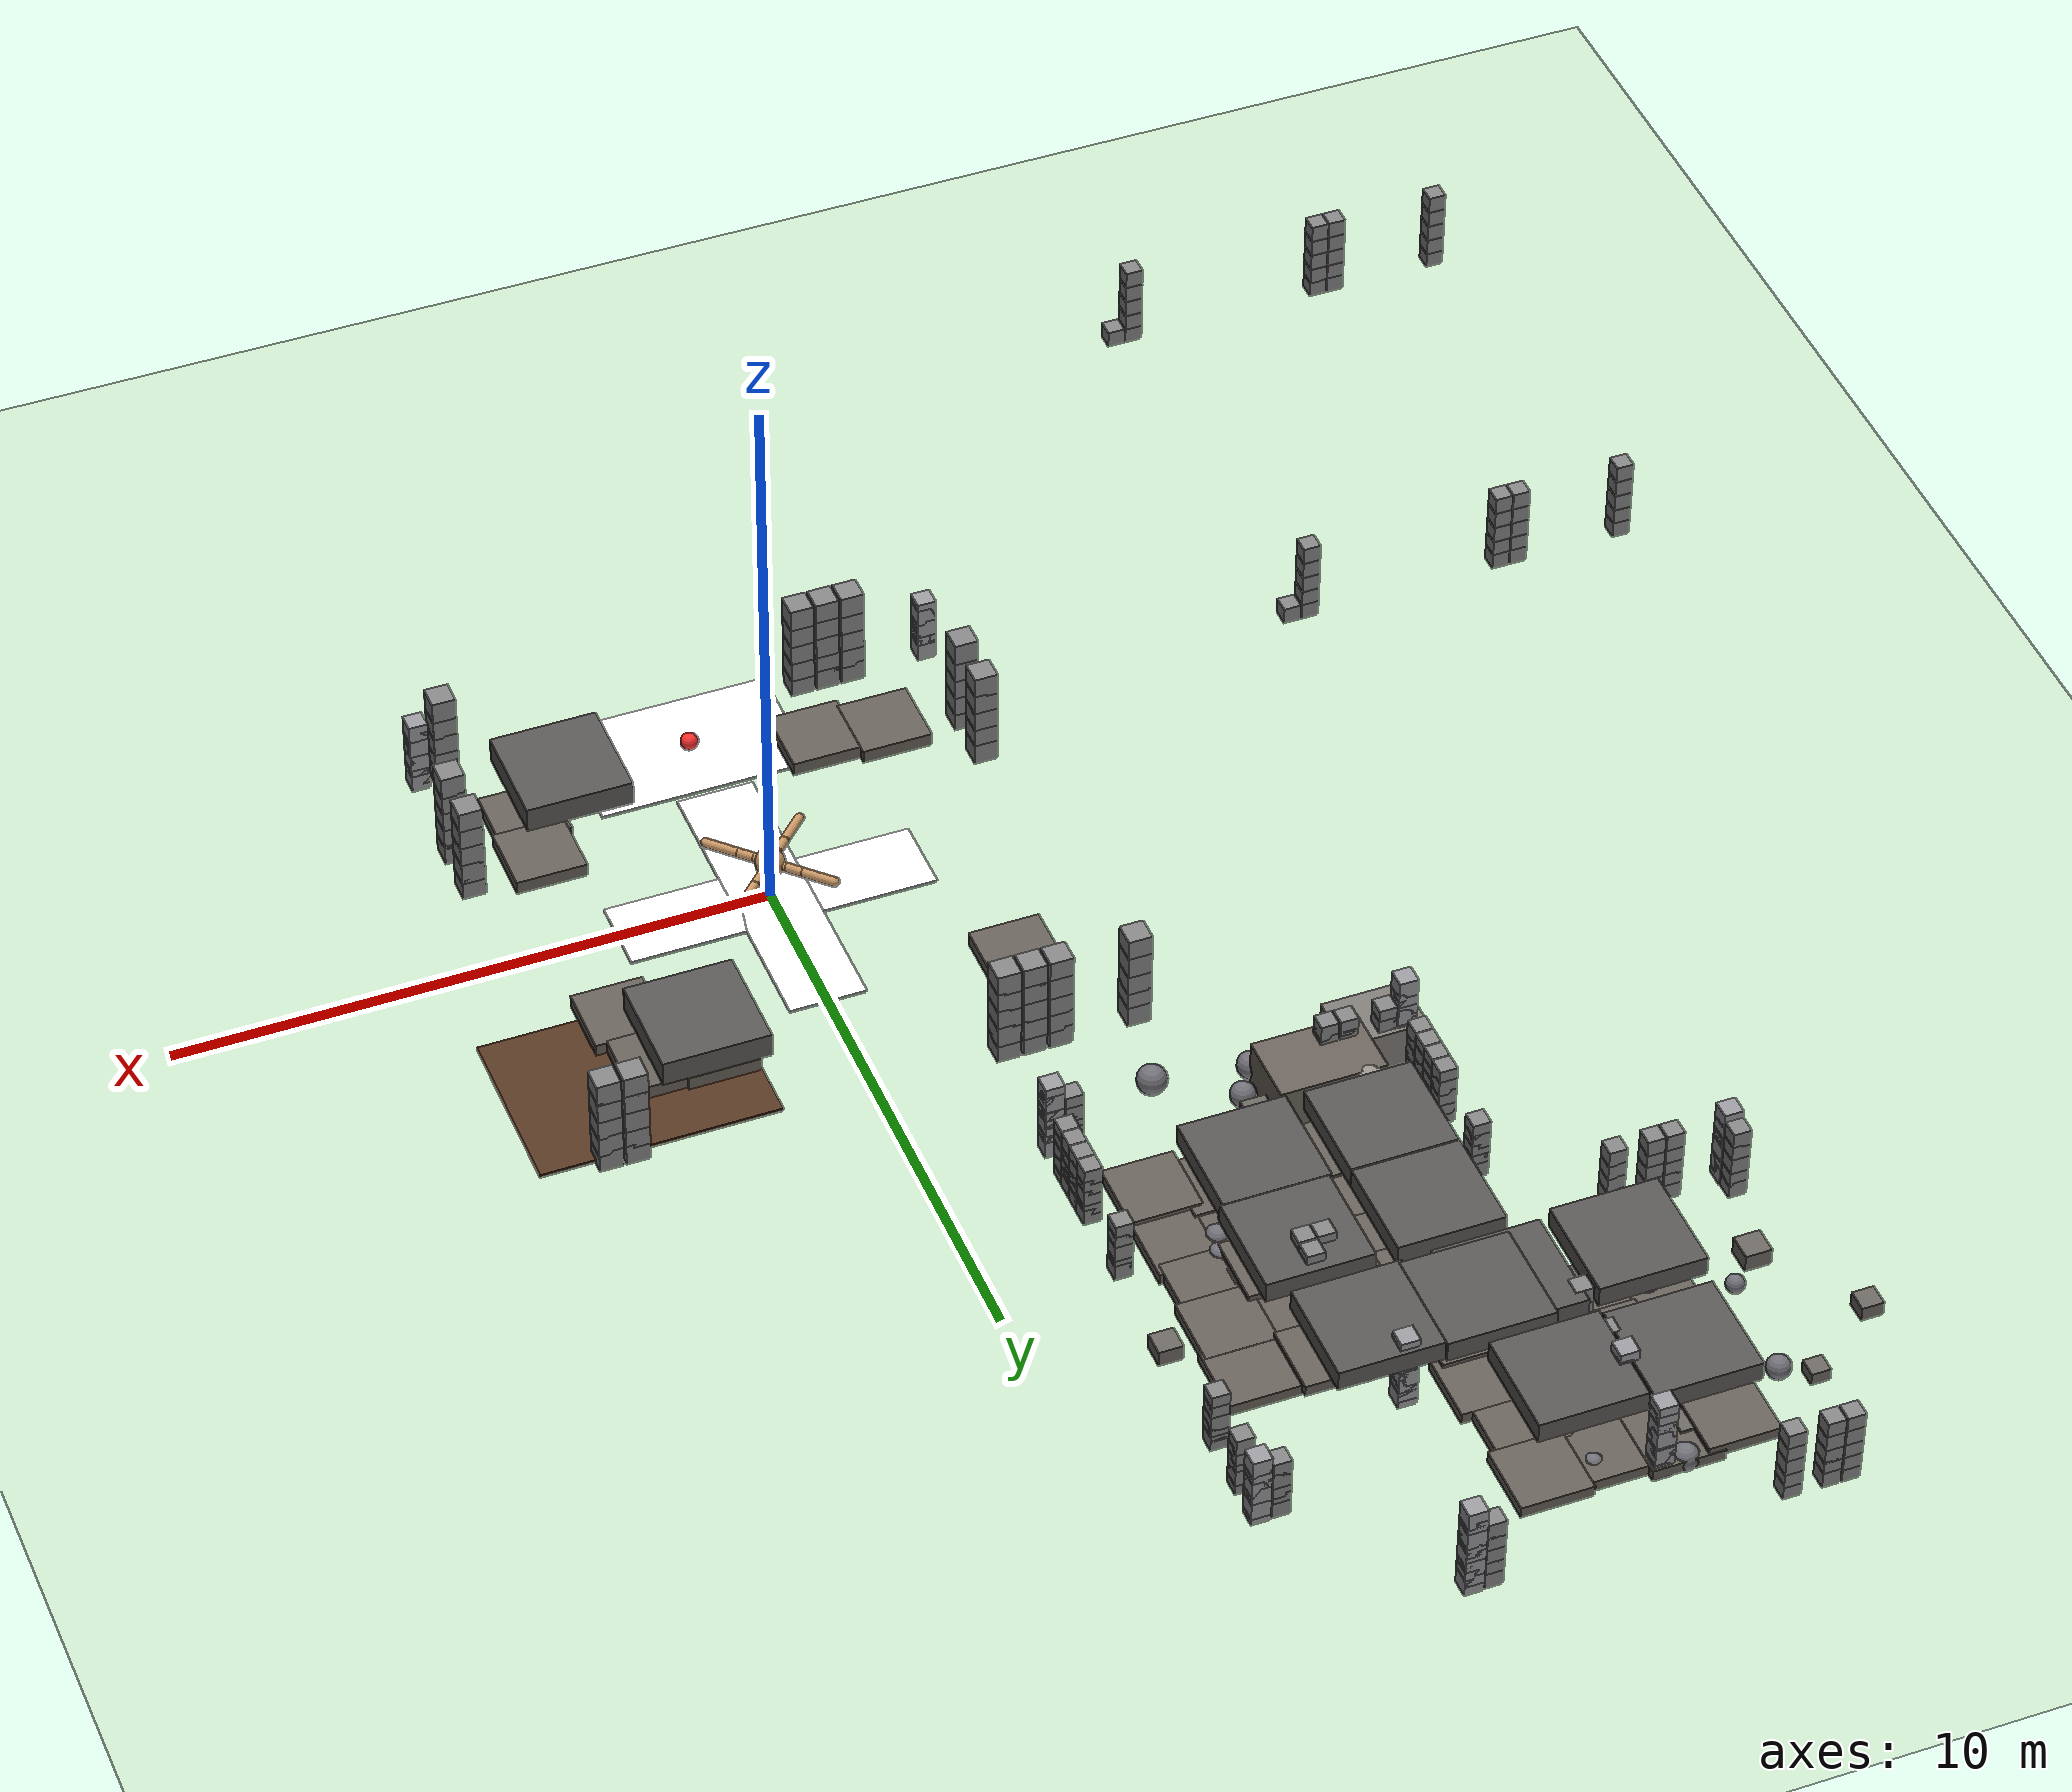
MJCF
<mujoco model="ant">
  <compiler angle="degree" coordinate="local" inertiafromgeom="true"/>
  <option integrator="RK4" timestep="0.01"/>
  <custom>
    <numeric data="0.0 0.0 0.55 1.0 0.0 0.0 0.0 0.0 1.0 0.0 -1.0 0.0 -1.0 0.0 1.0" name="init_qpos"/>
  </custom>
  <default>
    <joint armature="1" damping="1" limited="true"/>
    <geom conaffinity="0" condim="3" density="5.0" friction="1 0.5 0.5" margin="0.01" rgba="0.8 0.6 0.4 1"/>
  </default>
  <asset>
    <texture builtin="gradient" height="100" rgb1="1 1 1" rgb2="0 0 0" type="skybox" width="100"/>
    <texture builtin="flat" height="1278" mark="cross" markrgb="1 1 1" name="texgeom" random="0.01" rgb1="0.8 0.6 0.4" rgb2="0.8 0.6 0.4" type="cube" width="127"/>
    <texture builtin="checker" height="100" name="texplane" rgb1="0 0 0" rgb2="0.8 0.8 0.8" type="2d" width="100"/>
    <material name="MatPlane" reflectance="0.5" shininess="1" specular="1" texrepeat="60 60" texture="texplane"/>
    <material name="geom" texture="texgeom" texuniform="true"/>
  </asset>
  <worldbody>
    <light cutoff="100" diffuse="1 1 1" dir="-0 0 -1.3" directional="true" exponent="1" pos="0 0 1.3" specular=".1 .1 .1"/>
    <geom conaffinity="1" condim="3" material="MatPlane" name="floor" pos="0 0 0" rgba="0.8 0.9 0.8 1" size="40 40 40" type="plane"/>
    <body name="torso" pos="0 0 0.75">
      <camera name="track" mode="trackcom" pos="0 -3 0.3" xyaxes="1 0 0 0 0 1"/>
      <geom name="torso_geom" pos="0 0 0" size="0.25" type="sphere"/>
      <joint armature="0" damping="0" limited="false" margin="0.01" name="root" pos="0 0 0" type="free"/>
      <body name="front_left_leg" pos="0 0 0">
        <geom fromto="0.0 0.0 0.0 0.2 0.2 0.0" name="aux_1_geom" size="0.08" type="capsule"/>
        <body name="aux_1" pos="0.2 0.2 0">
          <joint axis="0 0 1" name="hip_1" pos="0.0 0.0 0.0" range="-30 30" type="hinge"/>
          <geom fromto="0.0 0.0 0.0 0.2 0.2 0.0" name="left_leg_geom" size="0.08" type="capsule"/>
          <body pos="0.2 0.2 0">
            <joint axis="-1 1 0" name="ankle_1" pos="0.0 0.0 0.0" range="30 70" type="hinge"/>
            <geom fromto="0.0 0.0 0.0 0.4 0.4 0.0" name="left_ankle_geom" size="0.08" type="capsule"/>
          </body>
        </body>
      </body>
      <body name="front_right_leg" pos="0 0 0">
        <geom fromto="0.0 0.0 0.0 -0.2 0.2 0.0" name="aux_2_geom" size="0.08" type="capsule"/>
        <body name="aux_2" pos="-0.2 0.2 0">
          <joint axis="0 0 1" name="hip_2" pos="0.0 0.0 0.0" range="-30 30" type="hinge"/>
          <geom fromto="0.0 0.0 0.0 -0.2 0.2 0.0" name="right_leg_geom" size="0.08" type="capsule"/>
          <body pos="-0.2 0.2 0">
            <joint axis="1 1 0" name="ankle_2" pos="0.0 0.0 0.0" range="-70 -30" type="hinge"/>
            <geom fromto="0.0 0.0 0.0 -0.4 0.4 0.0" name="right_ankle_geom" size="0.08" type="capsule"/>
          </body>
        </body>
      </body>
      <body name="back_leg" pos="0 0 0">
        <geom fromto="0.0 0.0 0.0 -0.2 -0.2 0.0" name="aux_3_geom" size="0.08" type="capsule"/>
        <body name="aux_3" pos="-0.2 -0.2 0">
          <joint axis="0 0 1" name="hip_3" pos="0.0 0.0 0.0" range="-30 30" type="hinge"/>
          <geom fromto="0.0 0.0 0.0 -0.2 -0.2 0.0" name="back_leg_geom" size="0.08" type="capsule"/>
          <body pos="-0.2 -0.2 0">
            <joint axis="-1 1 0" name="ankle_3" pos="0.0 0.0 0.0" range="-70 -30" type="hinge"/>
            <geom fromto="0.0 0.0 0.0 -0.4 -0.4 0.0" name="third_ankle_geom" size="0.08" type="capsule"/>
          </body>
        </body>
      </body>
      <body name="right_back_leg" pos="0 0 0">
        <geom fromto="0.0 0.0 0.0 0.2 -0.2 0.0" name="aux_4_geom" size="0.08" type="capsule"/>
        <body name="aux_4" pos="0.2 -0.2 0">
          <joint axis="0 0 1" name="hip_4" pos="0.0 0.0 0.0" range="-30 30" type="hinge"/>
          <geom fromto="0.0 0.0 0.0 0.2 -0.2 0.0" name="rightback_leg_geom" size="0.08" type="capsule"/>
          <body pos="0.2 -0.2 0">
            <joint axis="1 1 0" name="ankle_4" pos="0.0 0.0 0.0" range="30 70" type="hinge"/>
            <geom fromto="0.0 0.0 0.0 0.4 -0.4 0.0" name="fourth_ankle_geom" size="0.08" type="capsule"/>
          </body>
        </body>
      </body>
    </body>

        <body name="rubble_1" pos="-3.056152820587158 4.327457427978516 0.0"><geom type="box" size="0.6 0.6 0.1" pos="-3.056152820587158 4.327457427978516 0.18743394315242767" rgba="0.4 0.38 0.35 1.0" contype="1" conaffinity="1" friction="0.45 0.002 0.00005" solref="-100 -1" solimp="0.9 0.95 0.001" /></body>
        <body name="rubble_2" pos="-2.3706185817718506 5.584379196166992 0.0"><geom type="box" size="0.15 0.15 0.15" pos="-2.3706185817718506 5.584379196166992 0.9421411156654358" rgba="0.52 0.52 0.52 1.0" contype="1" conaffinity="1" friction="0.45 0.002 0.00005" solref="-100 -1" solimp="0.9 0.95 0.001" /></body>
        <body name="rubble_4" pos="-8.17128849029541 -1.6086636781692505 0.0"><geom type="box" size="0.15 0.15 0.15" pos="-8.17128849029541 -1.6086636781692505 0.42991626262664795" rgba="0.52 0.52 0.52 1.0" contype="1" conaffinity="1" friction="0.45 0.002 0.00005" solref="-100 -1" solimp="0.9 0.95 0.001" /></body>
        <body name="rubble_5" pos="-3.352055788040161 6.061844825744629 0.0"><geom type="sphere" size="0.1950169458929364" pos="-3.352055788040161 6.061844825744629 0.1599999964237213" rgba="0.45 0.45 0.48 1.0" contype="1" conaffinity="1" friction="0.45 0.002 0.00005" solref="-100 -1" solimp="0.9 0.95 0.001" /></body>
        <body name="rubble_6" pos="-1.0291504859924316 4.060200214385986 0.0"><geom type="box" size="0.15 0.15 0.15" pos="-1.0291504859924316 4.060200214385986 0.5580970048904419" rgba="0.52 0.52 0.52 1.0" contype="1" conaffinity="1" friction="0.45 0.002 0.00005" solref="-100 -1" solimp="0.9 0.95 0.001" /></body>
        <body name="rubble_8" pos="-2.1946258544921875 2.2910094261169434 0.0"><geom type="box" size="0.16 0.16 0.16" pos="-2.1946258544921875 2.2910094261169434 0.42729300260543823" rgba="0.6 0.6 0.62 1.0" contype="1" conaffinity="1" friction="0.45 0.002 0.00005" solref="-100 -1" solimp="0.9 0.95 0.001" /></body>
        <body name="rubble_9" pos="-5.745645999908447 5.7487287521362305 0.0"><geom type="box" size="0.15 0.15 0.15" pos="-5.745645999908447 5.7487287521362305 0.6680940985679626" rgba="0.52 0.52 0.52 1.0" contype="1" conaffinity="1" friction="0.45 0.002 0.00005" solref="-100 -1" solimp="0.9 0.95 0.001" /></body>
        <body name="rubble_10" pos="-1.5362380743026733 -2.2910094261169434 0.0"><geom type="box" size="0.2 0.2 0.2" pos="-1.5362380743026733 -2.2910094261169434 1.5854251384735107" rgba="0.52 0.52 0.52 1.0" contype="1" conaffinity="1" friction="0.45 0.002 0.00005" solref="-100 -1" solimp="0.9 0.95 0.001" /></body>
        <body name="rubble_11" pos="-2.1946258544921875 2.2910094261169434 0.0"><geom type="box" size="0.16 0.16 0.16" pos="-2.1946258544921875 2.2910094261169434 0.2736465036869049" rgba="0.6 0.6 0.62 1.0" contype="1" conaffinity="1" friction="0.45 0.002 0.00005" solref="-100 -1" solimp="0.9 0.95 0.001" /></body>
        <body name="rubble_15" pos="-2.6534793376922607 5.9141316413879395 0.0"><geom type="box" size="0.23474299995126924 0.23474299995126924 0.16432009996588845" pos="-2.6534793376922607 5.9141316413879395 0.15" rgba="0.42 0.4 0.38 1.0" contype="1" conaffinity="1" friction="0.45 0.002 0.00005" solref="-100 -1" solimp="0.9 0.95 0.001" /></body>
        <body name="rubble_16" pos="-2.2099030017852783 8.707018852233887 0.0"><geom type="box" size="0.16 0.16 0.16" pos="-2.2099030017852783 8.707018852233887 1.1483551263809204" rgba="0.6 0.6 0.62 1.0" contype="1" conaffinity="1" friction="0.45 0.002 0.00005" solref="-100 -1" solimp="0.9 0.95 0.001" /></body>
        <body name="rubble_17" pos="-1.0291504859924316 3.7469000816345215 0.0"><geom type="box" size="0.15 0.15 0.15" pos="-1.0291504859924316 3.7469000816345215 0.33904850482940674" rgba="0.52 0.52 0.52 1.0" contype="1" conaffinity="1" friction="0.45 0.002 0.00005" solref="-100 -1" solimp="0.9 0.95 0.001" /></body>
        <body name="rubble_18" pos="-1.0291504859924316 3.4335999488830566 0.0"><geom type="box" size="0.16 0.16 0.16" pos="-1.0291504859924316 3.4335999488830566 0.28762030601501465" rgba="0.6 0.6 0.62 1.0" contype="1" conaffinity="1" friction="0.45 0.002 0.00005" solref="-100 -1" solimp="0.9 0.95 0.001" /></body>
        <body name="rubble_20" pos="-3.9832544326782227 7.506500720977783 0.0"><geom type="box" size="0.15 0.15 0.15" pos="-3.9832544326782227 7.506500720977783 0.33904850482940674" rgba="0.52 0.52 0.52 1.0" contype="1" conaffinity="1" friction="0.45 0.002 0.00005" solref="-100 -1" solimp="0.9 0.95 0.001" /></body>
        <body name="rubble_21" pos="-3.9832544326782227 4.84345006942749 0.0"><geom type="box" size="0.15 0.15 0.15" pos="-3.9832544326782227 4.84345006942749 0.33904850482940674" rgba="0.52 0.52 0.52 1.0" contype="1" conaffinity="1" friction="0.45 0.002 0.00005" solref="-100 -1" solimp="0.9 0.95 0.001" /></body>
        <body name="rubble_22" pos="-1.0291504859924316 7.506500720977783 0.0"><geom type="box" size="0.15 0.15 0.15" pos="-1.0291504859924316 7.506500720977783 0.9961940050125122" rgba="0.52 0.52 0.52 1.0" contype="1" conaffinity="1" friction="0.45 0.002 0.00005" solref="-100 -1" solimp="0.9 0.95 0.001" /></body>
        <body name="rubble_23" pos="-2.506202459335327 6.827683925628662 0.0"><geom type="box" size="0.16 0.16 0.16" pos="-2.506202459335327 6.827683925628662 0.9005662202835083" rgba="0.6 0.6 0.62 1.0" contype="1" conaffinity="1" friction="0.45 0.002 0.00005" solref="-100 -1" solimp="0.9 0.95 0.001" /></body>
        <body name="rubble_24" pos="-1.1932673454284668 3.4335999488830566 0.0"><geom type="box" size="0.15 0.15 0.15" pos="-1.1932673454284668 3.4335999488830566 0.33904850482940674" rgba="0.52 0.52 0.52 1.0" contype="1" conaffinity="1" friction="0.45 0.002 0.00005" solref="-100 -1" solimp="0.9 0.95 0.001" /></body>
        <body name="rubble_25" pos="-1.0291504859924316 7.193200588226318 0.0"><geom type="box" size="0.15 0.15 0.15" pos="-1.0291504859924316 7.193200588226318 0.33904850482940674" rgba="0.52 0.52 0.52 1.0" contype="1" conaffinity="1" friction="0.45 0.002 0.00005" solref="-100 -1" solimp="0.9 0.95 0.001" /></body>
        <body name="rubble_26" pos="2.1946258544921875 2.2910094261169434 0.0"><geom type="box" size="0.2 0.2 0.2" pos="2.1946258544921875 2.2910094261169434 0.15" rgba="0.52 0.52 0.52 1.0" contype="1" conaffinity="1" friction="0.45 0.002 0.00005" solref="-100 -1" solimp="0.9 0.95 0.001" /></body>
        <body name="rubble_28" pos="-1.0291504859924316 6.723250389099121 0.0"><geom type="box" size="0.15 0.15 0.15" pos="-1.0291504859924316 6.723250389099121 0.33904850482940674" rgba="0.52 0.52 0.52 1.0" contype="1" conaffinity="1" friction="0.45 0.002 0.00005" solref="-100 -1" solimp="0.9 0.95 0.001" /></body>
        <body name="rubble_29" pos="-3.9832544326782227 4.060200214385986 0.0"><geom type="box" size="0.15 0.15 0.15" pos="-3.9832544326782227 4.060200214385986 0.33904850482940674" rgba="0.52 0.52 0.52 1.0" contype="1" conaffinity="1" friction="0.45 0.002 0.00005" solref="-100 -1" solimp="0.9 0.95 0.001" /></body>
        <body name="rubble_30" pos="-3.326786994934082 3.4335999488830566 0.0"><geom type="box" size="0.15 0.15 0.15" pos="-3.326786994934082 3.4335999488830566 0.33904850482940674" rgba="0.52 0.52 0.52 1.0" contype="1" conaffinity="1" friction="0.45 0.002 0.00005" solref="-100 -1" solimp="0.9 0.95 0.001" /></body>
        <body name="rubble_32" pos="2.1946258544921875 -2.2910094261169434 0.0"><geom type="box" size="0.16 0.16 0.16" pos="2.1946258544921875 -2.2910094261169434 0.15" rgba="0.6 0.6 0.62 1.0" contype="1" conaffinity="1" friction="0.45 0.002 0.00005" solref="-100 -1" solimp="0.9 0.95 0.001" /></body>
        <body name="rubble_33" pos="-2.506202459335327 6.827683925628662 0.0"><geom type="box" size="0.16 0.16 0.16" pos="-2.506202459335327 6.827683925628662 1.0566794872283936" rgba="0.6 0.6 0.62 1.0" contype="1" conaffinity="1" friction="0.45 0.002 0.00005" solref="-100 -1" solimp="0.9 0.95 0.001" /></body>
        <body name="rubble_35" pos="-3.101742744445801 5.804529190063477 0.0"><geom type="box" size="0.6 0.6 0.1" pos="-3.101742744445801 5.804529190063477 0.23780526220798492" rgba="0.4 0.38 0.35 1.0" contype="1" conaffinity="1" friction="0.45 0.002 0.00005" solref="-100 -1" solimp="0.9 0.95 0.001" /></body>
        <body name="rubble_36" pos="-3.8191375732421875 7.506500720977783 0.0"><geom type="box" size="0.15 0.15 0.15" pos="-3.8191375732421875 7.506500720977783 0.5580970048904419" rgba="0.52 0.52 0.52 1.0" contype="1" conaffinity="1" friction="0.45 0.002 0.00005" solref="-100 -1" solimp="0.9 0.95 0.001" /></body>
        <body name="rubble_37" pos="-2.2099030017852783 5.7487287521362305 0.0"><geom type="box" size="0.15 0.15 0.15" pos="-2.2099030017852783 5.7487287521362305 0.3940470516681671" rgba="0.52 0.52 0.52 1.0" contype="1" conaffinity="1" friction="0.45 0.002 0.00005" solref="-100 -1" solimp="0.9 0.95 0.001" /></body>
        <body name="rubble_38" pos="-3.8191375732421875 7.506500720977783 0.0"><geom type="box" size="0.15 0.15 0.15" pos="-3.8191375732421875 7.506500720977783 0.15" rgba="0.52 0.52 0.52 1.0" contype="1" conaffinity="1" friction="0.45 0.002 0.00005" solref="-100 -1" solimp="0.9 0.95 0.001" /></body>
        <body name="rubble_39" pos="-2.0655839443206787 5.301447868347168 0.0"><geom type="box" size="0.6 0.6 0.1" pos="-2.0655839443206787 5.301447868347168 0.25787556171417236" rgba="0.4 0.38 0.35 1.0" contype="1" conaffinity="1" friction="0.45 0.002 0.00005" solref="-100 -1" solimp="0.9 0.95 0.001" /></body>
        <body name="rubble_40" pos="-4.781352519989014 5.584379196166992 0.0"><geom type="box" size="0.15 0.15 0.15" pos="-4.781352519989014 5.584379196166992 0.3940470516681671" rgba="0.52 0.52 0.52 1.0" contype="1" conaffinity="1" friction="0.45 0.002 0.00005" solref="-100 -1" solimp="0.9 0.95 0.001" /></body>
        <body name="rubble_41" pos="-6.13599157333374 7.274881839752197 0.0"><geom type="box" size="0.18566450208560192 0.18566450208560192 0.12996515145992135" pos="-6.13599157333374 7.274881839752197 0.15" rgba="0.42 0.4 0.38 1.0" contype="1" conaffinity="1" friction="0.45 0.002 0.00005" solref="-100 -1" solimp="0.9 0.95 0.001" /></body>
        <body name="rubble_42" pos="-1.0291504859924316 4.060200214385986 0.0"><geom type="box" size="0.15 0.15 0.15" pos="-1.0291504859924316 4.060200214385986 0.33904850482940674" rgba="0.52 0.52 0.52 1.0" contype="1" conaffinity="1" friction="0.45 0.002 0.00005" solref="-100 -1" solimp="0.9 0.95 0.001" /></body>
        <body name="rubble_44" pos="-2.217968225479126 5.452096939086914 0.0"><geom type="box" size="0.9 0.9 0.18" pos="-2.217968225479126 5.452096939086914 1.0191572904586792" rgba="0.35 0.34 0.33 1.0" contype="1" conaffinity="1" friction="0.45 0.002 0.00005" solref="-100 -1" solimp="0.9 0.95 0.001" /></body>
        <body name="rubble_45" pos="-3.0436339378356934 4.84943962097168 0.0"><geom type="box" size="0.6 0.6 0.1" pos="-3.0436339378356934 4.84943962097168 0.15" rgba="0.4 0.38 0.35 1.0" contype="1" conaffinity="1" friction="0.45 0.002 0.00005" solref="-100 -1" solimp="0.9 0.95 0.001" /></body>
        <body name="rubble_46" pos="-5.745645999908447 5.584379196166992 0.0"><geom type="box" size="0.16 0.16 0.16" pos="-5.745645999908447 5.584379196166992 1.1504219770431519" rgba="0.6 0.6 0.62 1.0" contype="1" conaffinity="1" friction="0.45 0.002 0.00005" solref="-100 -1" solimp="0.9 0.95 0.001" /></body>
        <body name="rubble_47" pos="-1.0291504859924316 3.4335999488830566 0.0"><geom type="box" size="0.16 0.16 0.16" pos="-1.0291504859924316 3.4335999488830566 0.7904812693595886" rgba="0.6 0.6 0.62 1.0" contype="1" conaffinity="1" friction="0.45 0.002 0.00005" solref="-100 -1" solimp="0.9 0.95 0.001" /></body>
        <body name="rubble_51" pos="-8.17128849029541 -5.46581506729126 0.0"><geom type="box" size="0.15 0.15 0.15" pos="-8.17128849029541 -5.46581506729126 0.7398325204849243" rgba="0.52 0.52 0.52 1.0" contype="1" conaffinity="1" friction="0.45 0.002 0.00005" solref="-100 -1" solimp="0.9 0.95 0.001" /></body>
        <body name="rubble_52" pos="-3.9777743816375732 8.186578750610352 0.0"><geom type="box" size="0.16 0.16 0.16" pos="-3.9777743816375732 8.186578750610352 1.0165624618530273" rgba="0.6 0.6 0.62 1.0" contype="1" conaffinity="1" friction="0.45 0.002 0.00005" solref="-100 -1" solimp="0.9 0.95 0.001" /></body>
        <body name="rubble_54" pos="-5.178455829620361 -1.6086636781692505 0.0"><geom type="box" size="0.15 0.15 0.15" pos="-5.178455829620361 -1.6086636781692505 0.15" rgba="0.52 0.52 0.52 1.0" contype="1" conaffinity="1" friction="0.45 0.002 0.00005" solref="-100 -1" solimp="0.9 0.95 0.001" /></body>
        <body name="rubble_56" pos="-7.2261834144592285 -1.6086636781692505 0.0"><geom type="box" size="0.15 0.15 0.15" pos="-7.2261834144592285 -1.6086636781692505 0.7398325204849243" rgba="0.52 0.52 0.52 1.0" contype="1" conaffinity="1" friction="0.45 0.002 0.00005" solref="-100 -1" solimp="0.9 0.95 0.001" /></body>
        <body name="rubble_58" pos="-2.2099030017852783 5.584379196166992 0.0"><geom type="box" size="0.15 0.15 0.15" pos="-2.2099030017852783 5.584379196166992 0.6680940985679626" rgba="0.52 0.52 0.52 1.0" contype="1" conaffinity="1" friction="0.45 0.002 0.00005" solref="-100 -1" solimp="0.9 0.95 0.001" /></body>
        <body name="rubble_61" pos="-3.326786994934082 3.4335999488830566 0.0"><geom type="box" size="0.15 0.15 0.15" pos="-3.326786994934082 3.4335999488830566 0.777145504951477" rgba="0.52 0.52 0.52 1.0" contype="1" conaffinity="1" friction="0.45 0.002 0.00005" solref="-100 -1" solimp="0.9 0.95 0.001" /></body>
        <body name="rubble_62" pos="-2.1946258544921875 -1.4182438850402832 0.0"><geom type="box" size="0.2 0.2 0.2" pos="-2.1946258544921875 -1.4182438850402832 1.2190687656402588" rgba="0.52 0.52 0.52 1.0" contype="1" conaffinity="1" friction="0.45 0.002 0.00005" solref="-100 -1" solimp="0.9 0.95 0.001" /></body>
        <body name="rubble_63" pos="-4.424579620361328 7.132345676422119 0.0"><geom type="sphere" size="0.17743942822523945" pos="-4.424579620361328 7.132345676422119 0.1599999964237213" rgba="0.45 0.45 0.48 1.0" contype="1" conaffinity="1" friction="0.45 0.002 0.00005" solref="-100 -1" solimp="0.9 0.95 0.001" /></body>
        <body name="rubble_64" pos="-3.340083599090576 7.030445098876953 0.0"><geom type="sphere" size="0.24577728158079498" pos="-3.340083599090576 7.030445098876953 0.1599999964237213" rgba="0.45 0.45 0.48 1.0" contype="1" conaffinity="1" friction="0.45 0.002 0.00005" solref="-100 -1" solimp="0.9 0.95 0.001" /></body>
        <body name="rubble_65" pos="-3.490903854370117 7.506500720977783 0.0"><geom type="box" size="0.15 0.15 0.15" pos="-3.490903854370117 7.506500720977783 0.777145504951477" rgba="0.52 0.52 0.52 1.0" contype="1" conaffinity="1" friction="0.45 0.002 0.00005" solref="-100 -1" solimp="0.9 0.95 0.001" /></body>
        <body name="rubble_66" pos="2.1946258544921875 -2.2910094261169434 0.0"><geom type="box" size="0.16 0.16 0.16" pos="2.1946258544921875 -2.2910094261169434 0.2758702337741852" rgba="0.6 0.6 0.62 1.0" contype="1" conaffinity="1" friction="0.45 0.002 0.00005" solref="-100 -1" solimp="0.9 0.95 0.001" /></body>
        <body name="rubble_67" pos="1.975163221359253 -2.2910094261169434 0.0"><geom type="box" size="0.2 0.2 0.2" pos="1.975163221359253 -2.2910094261169434 0.486356258392334" rgba="0.52 0.52 0.52 1.0" contype="1" conaffinity="1" friction="0.45 0.002 0.00005" solref="-100 -1" solimp="0.9 0.95 0.001" /></body>
        <body name="rubble_68" pos="-5.102783679962158 8.707018852233887 0.0"><geom type="box" size="0.15 0.15 0.15" pos="-5.102783679962158 8.707018852233887 0.6680940985679626" rgba="0.52 0.52 0.52 1.0" contype="1" conaffinity="1" friction="0.45 0.002 0.00005" solref="-100 -1" solimp="0.9 0.95 0.001" /></body>
        <body name="rubble_69" pos="-3.9832544326782227 7.193200588226318 0.0"><geom type="box" size="0.15 0.15 0.15" pos="-3.9832544326782227 7.193200588226318 0.33904850482940674" rgba="0.52 0.52 0.52 1.0" contype="1" conaffinity="1" friction="0.45 0.002 0.00005" solref="-100 -1" solimp="0.9 0.95 0.001" /></body>
        <body name="rubble_71" pos="-2.2099030017852783 8.707018852233887 0.0"><geom type="box" size="0.16 0.16 0.16" pos="-2.2099030017852783 8.707018852233887 0.3256710171699524" rgba="0.6 0.6 0.62 1.0" contype="1" conaffinity="1" friction="0.45 0.002 0.00005" solref="-100 -1" solimp="0.9 0.95 0.001" /></body>
        <body name="rubble_73" pos="2.1946258544921875 -1.4182438850402832 0.0"><geom type="box" size="0.2 0.2 0.2" pos="2.1946258544921875 -1.4182438850402832 0.486356258392334" rgba="0.52 0.52 0.52 1.0" contype="1" conaffinity="1" friction="0.45 0.002 0.00005" solref="-100 -1" solimp="0.9 0.95 0.001" /></body>
        <body name="rubble_76" pos="2.1946258544921875 -2.2910094261169434 0.0"><geom type="box" size="0.16 0.16 0.16" pos="2.1946258544921875 -2.2910094261169434 0.7434809803962708" rgba="0.6 0.6 0.62 1.0" contype="1" conaffinity="1" friction="0.45 0.002 0.00005" solref="-100 -1" solimp="0.9 0.95 0.001" /></body>
        <body name="rubble_78" pos="-5.745645999908447 5.584379196166992 0.0"><geom type="box" size="0.16 0.16 0.16" pos="-5.745645999908447 5.584379196166992 0.9786849617958069" rgba="0.6 0.6 0.62 1.0" contype="1" conaffinity="1" friction="0.45 0.002 0.00005" solref="-100 -1" solimp="0.9 0.95 0.001" /></body>
        <body name="rubble_82" pos="-3.9832544326782227 7.506500720977783 0.0"><geom type="box" size="0.16 0.16 0.16" pos="-3.9832544326782227 7.506500720977783 1.1767008304595947" rgba="0.6 0.6 0.62 1.0" contype="1" conaffinity="1" friction="0.45 0.002 0.00005" solref="-100 -1" solimp="0.9 0.95 0.001" /></body>
        <body name="rubble_83" pos="-2.3706185817718506 8.707018852233887 0.0"><geom type="box" size="0.15 0.15 0.15" pos="-2.3706185817718506 8.707018852233887 0.15" rgba="0.52 0.52 0.52 1.0" contype="1" conaffinity="1" friction="0.45 0.002 0.00005" solref="-100 -1" solimp="0.9 0.95 0.001" /></body>
        <body name="rubble_84" pos="-1.3167754411697388 -2.2910094261169434 0.0"><geom type="box" size="0.2 0.2 0.2" pos="-1.3167754411697388 -2.2910094261169434 0.8527125716209412" rgba="0.52 0.52 0.52 1.0" contype="1" conaffinity="1" friction="0.45 0.002 0.00005" solref="-100 -1" solimp="0.9 0.95 0.001" /></body>
        <body name="rubble_86" pos="-1.8314388990402222 4.8473429679870605 0.0"><geom type="sphere" size="0.21009531748623242" pos="-1.8314388990402222 4.8473429679870605 0.1599999964237213" rgba="0.45 0.45 0.48 1.0" contype="1" conaffinity="1" friction="0.45 0.002 0.00005" solref="-100 -1" solimp="0.9 0.95 0.001" /></body>
        <body name="rubble_87" pos="1.0659024715423584 1.5529084205627441 0.0"><geom type="box" size="0.6 0.6 0.12" pos="1.0659024715423584 1.5529084205627441 0.20491987466812134" rgba="0.4 0.38 0.35 1.0" contype="1" conaffinity="1" friction="0.45 0.002 0.00005" solref="-100 -1" solimp="0.9 0.95 0.001" /></body>
        <body name="rubble_88" pos="1.975163221359253 2.2910094261169434 0.0"><geom type="box" size="0.2 0.2 0.2" pos="1.975163221359253 2.2910094261169434 0.15" rgba="0.52 0.52 0.52 1.0" contype="1" conaffinity="1" friction="0.45 0.002 0.00005" solref="-100 -1" solimp="0.9 0.95 0.001" /></body>
        <body name="rubble_89" pos="-4.849390983581543 8.072747230529785 0.0"><geom type="box" size="0.149576813558354 0.149576813558354 0.1047037694908478" pos="-4.849390983581543 8.072747230529785 0.15" rgba="0.42 0.4 0.38 1.0" contype="1" conaffinity="1" friction="0.45 0.002 0.00005" solref="-100 -1" solimp="0.9 0.95 0.001" /></body>
        <body name="rubble_91" pos="2.1946258544921875 -0.9818611741065979 0.0"><geom type="box" size="0.2 0.2 0.2" pos="2.1946258544921875 -0.9818611741065979 0.15" rgba="0.52 0.52 0.52 1.0" contype="1" conaffinity="1" friction="0.45 0.002 0.00005" solref="-100 -1" solimp="0.9 0.95 0.001" /></body>
        <body name="rubble_92" pos="-3.9832544326782227 3.4335999488830566 0.0"><geom type="box" size="0.16 0.16 0.16" pos="-3.9832544326782227 3.4335999488830566 1.4701204299926758" rgba="0.6 0.6 0.62 1.0" contype="1" conaffinity="1" friction="0.45 0.002 0.00005" solref="-100 -1" solimp="0.9 0.95 0.001" /></body>
        <body name="rubble_93" pos="-4.781352519989014 5.584379196166992 0.0"><geom type="box" size="0.15 0.15 0.15" pos="-4.781352519989014 5.584379196166992 0.6680940985679626" rgba="0.52 0.52 0.52 1.0" contype="1" conaffinity="1" friction="0.45 0.002 0.00005" solref="-100 -1" solimp="0.9 0.95 0.001" /></body>
        <body name="rubble_94" pos="2.1946258544921875 -1.4182438850402832 0.0"><geom type="box" size="0.2 0.2 0.2" pos="2.1946258544921875 -1.4182438850402832 0.15" rgba="0.52 0.52 0.52 1.0" contype="1" conaffinity="1" friction="0.45 0.002 0.00005" solref="-100 -1" solimp="0.9 0.95 0.001" /></body>
        <body name="rubble_95" pos="-2.1946258544921875 2.2910094261169434 0.0"><geom type="box" size="0.2 0.2 0.2" pos="-2.1946258544921875 2.2910094261169434 1.5854251384735107" rgba="0.52 0.52 0.52 1.0" contype="1" conaffinity="1" friction="0.45 0.002 0.00005" solref="-100 -1" solimp="0.9 0.95 0.001" /></body>
        <body name="rubble_96" pos="-2.1946258544921875 -2.2910094261169434 0.0"><geom type="box" size="0.16 0.16 0.16" pos="-2.1946258544921875 -2.2910094261169434 0.15" rgba="0.6 0.6 0.62 1.0" contype="1" conaffinity="1" friction="0.45 0.002 0.00005" solref="-100 -1" solimp="0.9 0.95 0.001" /></body>
        <body name="rubble_97" pos="-2.3706185817718506 5.584379196166992 0.0"><geom type="box" size="0.15 0.15 0.15" pos="-2.3706185817718506 5.584379196166992 1.2161881923675537" rgba="0.52 0.52 0.52 1.0" contype="1" conaffinity="1" friction="0.45 0.002 0.00005" solref="-100 -1" solimp="0.9 0.95 0.001" /></body>
        <body name="rubble_98" pos="-5.293797016143799 6.73028564453125 0.0"><geom type="sphere" size="0.15838999526006384" pos="-5.293797016143799 6.73028564453125 0.1599999964237213" rgba="0.45 0.45 0.48 1.0" contype="1" conaffinity="1" friction="0.45 0.002 0.00005" solref="-100 -1" solimp="0.9 0.95 0.001" /></body>
        <body name="rubble_103" pos="-2.1946258544921875 -2.2910094261169434 0.0"><geom type="box" size="0.16 0.16 0.16" pos="-2.1946258544921875 -2.2910094261169434 0.25004562735557556" rgba="0.6 0.6 0.62 1.0" contype="1" conaffinity="1" friction="0.45 0.002 0.00005" solref="-100 -1" solimp="0.9 0.95 0.001" /></body>
        <body name="rubble_105" pos="-3.9832544326782227 3.903549909591675 0.0"><geom type="box" size="0.15 0.15 0.15" pos="-3.9832544326782227 3.903549909591675 0.777145504951477" rgba="0.52 0.52 0.52 1.0" contype="1" conaffinity="1" friction="0.45 0.002 0.00005" solref="-100 -1" solimp="0.9 0.95 0.001" /></body>
        <body name="rubble_108" pos="-3.9832544326782227 3.4335999488830566 0.0"><geom type="box" size="0.15 0.15 0.15" pos="-3.9832544326782227 3.4335999488830566 0.33904850482940674" rgba="0.52 0.52 0.52 1.0" contype="1" conaffinity="1" friction="0.45 0.002 0.00005" solref="-100 -1" solimp="0.9 0.95 0.001" /></body>
        <body name="rubble_109" pos="-1.0291504859924316 4.84345006942749 0.0"><geom type="box" size="0.15 0.15 0.15" pos="-1.0291504859924316 4.84345006942749 0.33904850482940674" rgba="0.52 0.52 0.52 1.0" contype="1" conaffinity="1" friction="0.45 0.002 0.00005" solref="-100 -1" solimp="0.9 0.95 0.001" /></body>
        <body name="rubble_112" pos="-2.1017508506774902 6.305798053741455 0.0"><geom type="box" size="0.6 0.6 0.1" pos="-2.1017508506774902 6.305798053741455 0.2453881949186325" rgba="0.4 0.38 0.35 1.0" contype="1" conaffinity="1" friction="0.45 0.002 0.00005" solref="-100 -1" solimp="0.9 0.95 0.001" /></body>
        <body name="rubble_113" pos="-1.0291504859924316 7.193200588226318 0.0"><geom type="box" size="0.15 0.15 0.15" pos="-1.0291504859924316 7.193200588226318 0.5580970048904419" rgba="0.52 0.52 0.52 1.0" contype="1" conaffinity="1" friction="0.45 0.002 0.00005" solref="-100 -1" solimp="0.9 0.95 0.001" /></body>
        <body name="rubble_114" pos="-2.238861083984375 4.5642924308776855 0.0"><geom type="box" size="0.9 0.9 0.18" pos="-2.238861083984375 4.5642924308776855 1.0296947956085205" rgba="0.35 0.34 0.33 1.0" contype="1" conaffinity="1" friction="0.45 0.002 0.00005" solref="-100 -1" solimp="0.9 0.95 0.001" /></body>
        <body name="rubble_115" pos="-2.2099030017852783 5.584379196166992 0.0"><geom type="box" size="0.15 0.15 0.15" pos="-2.2099030017852783 5.584379196166992 0.3940470516681671" rgba="0.52 0.52 0.52 1.0" contype="1" conaffinity="1" friction="0.45 0.002 0.00005" solref="-100 -1" solimp="0.9 0.95 0.001" /></body>
        <body name="rubble_117" pos="-1.0291504859924316 3.4335999488830566 0.0"><geom type="box" size="0.16 0.16 0.16" pos="-1.0291504859924316 3.4335999488830566 0.9581015706062317" rgba="0.6 0.6 0.62 1.0" contype="1" conaffinity="1" friction="0.45 0.002 0.00005" solref="-100 -1" solimp="0.9 0.95 0.001" /></body>
        <body name="rubble_118" pos="-7.068665981292725 -5.46581506729126 0.0"><geom type="box" size="0.15 0.15 0.15" pos="-7.068665981292725 -5.46581506729126 0.42991626262664795" rgba="0.52 0.52 0.52 1.0" contype="1" conaffinity="1" friction="0.45 0.002 0.00005" solref="-100 -1" solimp="0.9 0.95 0.001" /></body>
        <body name="rubble_120" pos="-3.9832544326782227 3.4335999488830566 0.0"><geom type="box" size="0.16 0.16 0.16" pos="-3.9832544326782227 3.4335999488830566 0.31287434697151184" rgba="0.6 0.6 0.62 1.0" contype="1" conaffinity="1" friction="0.45 0.002 0.00005" solref="-100 -1" solimp="0.9 0.95 0.001" /></body>
        <body name="rubble_121" pos="-3.9832544326782227 4.216850280761719 0.0"><geom type="box" size="0.15 0.15 0.15" pos="-3.9832544326782227 4.216850280761719 0.5580970048904419" rgba="0.52 0.52 0.52 1.0" contype="1" conaffinity="1" friction="0.45 0.002 0.00005" solref="-100 -1" solimp="0.9 0.95 0.001" /></body>
        <body name="rubble_122" pos="-3.1824495792388916 7.431332588195801 0.0"><geom type="box" size="0.6 0.6 0.1" pos="-3.1824495792388916 7.431332588195801 0.15" rgba="0.4 0.38 0.35 1.0" contype="1" conaffinity="1" friction="0.45 0.002 0.00005" solref="-100 -1" solimp="0.9 0.95 0.001" /></body>
        <body name="rubble_123" pos="1.975163221359253 -2.2910094261169434 0.0"><geom type="box" size="0.2 0.2 0.2" pos="1.975163221359253 -2.2910094261169434 0.8527125716209412" rgba="0.52 0.52 0.52 1.0" contype="1" conaffinity="1" friction="0.45 0.002 0.00005" solref="-100 -1" solimp="0.9 0.95 0.001" /></body>
        <body name="rubble_125" pos="-2.2099030017852783 5.584379196166992 0.0"><geom type="box" size="0.16 0.16 0.16" pos="-2.2099030017852783 5.584379196166992 0.7938346862792969" rgba="0.6 0.6 0.62 1.0" contype="1" conaffinity="1" friction="0.45 0.002 0.00005" solref="-100 -1" solimp="0.9 0.95 0.001" /></body>
        <body name="rubble_127" pos="-1.0291504859924316 4.84345006942749 0.0"><geom type="box" size="0.15 0.15 0.15" pos="-1.0291504859924316 4.84345006942749 0.9961940050125122" rgba="0.52 0.52 0.52 1.0" contype="1" conaffinity="1" friction="0.45 0.002 0.00005" solref="-100 -1" solimp="0.9 0.95 0.001" /></body>
        <body name="rubble_128" pos="-2.2099030017852783 5.584379196166992 0.0"><geom type="box" size="0.16 0.16 0.16" pos="-2.2099030017852783 5.584379196166992 0.6815289258956909" rgba="0.6 0.6 0.62 1.0" contype="1" conaffinity="1" friction="0.45 0.002 0.00005" solref="-100 -1" solimp="0.9 0.95 0.001" /></body>
        <body name="rubble_129" pos="-5.745645999908447 5.7487287521362305 0.0"><geom type="box" size="0.15 0.15 0.15" pos="-5.745645999908447 5.7487287521362305 1.2161881923675537" rgba="0.52 0.52 0.52 1.0" contype="1" conaffinity="1" friction="0.45 0.002 0.00005" solref="-100 -1" solimp="0.9 0.95 0.001" /></body>
        <body name="rubble_130" pos="-4.670722961425781 7.245607852935791 0.0"><geom type="box" size="0.22723787778686172 0.22723787778686172 0.1590665144508032" pos="-4.670722961425781 7.245607852935791 0.15" rgba="0.42 0.4 0.38 1.0" contype="1" conaffinity="1" friction="0.45 0.002 0.00005" solref="-100 -1" solimp="0.9 0.95 0.001" /></body>
        <body name="rubble_131" pos="-3.9832544326782227 6.723250389099121 0.0"><geom type="box" size="0.15 0.15 0.15" pos="-3.9832544326782227 6.723250389099121 0.9961940050125122" rgba="0.52 0.52 0.52 1.0" contype="1" conaffinity="1" friction="0.45 0.002 0.00005" solref="-100 -1" solimp="0.9 0.95 0.001" /></body>
        <body name="rubble_132" pos="-3.326786994934082 7.506500720977783 0.0"><geom type="box" size="0.15 0.15 0.15" pos="-3.326786994934082 7.506500720977783 0.15" rgba="0.52 0.52 0.52 1.0" contype="1" conaffinity="1" friction="0.45 0.002 0.00005" solref="-100 -1" solimp="0.9 0.95 0.001" /></body>
        <body name="rubble_133" pos="-3.9832544326782227 3.7469000816345215 0.0"><geom type="box" size="0.15 0.15 0.15" pos="-3.9832544326782227 3.7469000816345215 0.15" rgba="0.52 0.52 0.52 1.0" contype="1" conaffinity="1" friction="0.45 0.002 0.00005" solref="-100 -1" solimp="0.9 0.95 0.001" /></body>
        <body name="rubble_134" pos="-3.9832544326782227 3.4335999488830566 0.0"><geom type="box" size="0.15 0.15 0.15" pos="-3.9832544326782227 3.4335999488830566 0.777145504951477" rgba="0.52 0.52 0.52 1.0" contype="1" conaffinity="1" friction="0.45 0.002 0.00005" solref="-100 -1" solimp="0.9 0.95 0.001" /></body>
        <body name="rubble_135" pos="-2.5350630283355713 4.754560470581055 0.0"><geom type="sphere" size="0.16493654311368744" pos="-2.5350630283355713 4.754560470581055 0.1599999964237213" rgba="0.45 0.45 0.48 1.0" contype="1" conaffinity="1" friction="0.45 0.002 0.00005" solref="-100 -1" solimp="0.9 0.95 0.001" /></body>
        <body name="rubble_136" pos="-1.027216911315918 5.760366439819336 0.0"><geom type="box" size="0.2053230705526468 0.2053230705526468 0.14372614938685277" pos="-1.027216911315918 5.760366439819336 0.15" rgba="0.42 0.4 0.38 1.0" contype="1" conaffinity="1" friction="0.45 0.002 0.00005" solref="-100 -1" solimp="0.9 0.95 0.001" /></body>
        <body name="rubble_137" pos="-3.9832544326782227 7.506500720977783 0.0"><geom type="box" size="0.15 0.15 0.15" pos="-3.9832544326782227 7.506500720977783 0.33904850482940674" rgba="0.52 0.52 0.52 1.0" contype="1" conaffinity="1" friction="0.45 0.002 0.00005" solref="-100 -1" solimp="0.9 0.95 0.001" /></body>
        <body name="rubble_141" pos="-2.013120412826538 3.095930576324463 0.0"><geom type="sphere" size="0.25280056903623893" pos="-2.013120412826538 3.095930576324463 0.1599999964237213" rgba="0.45 0.45 0.48 1.0" contype="1" conaffinity="1" friction="0.45 0.002 0.00005" solref="-100 -1" solimp="0.9 0.95 0.001" /></body>
        <body name="rubble_142" pos="-5.476973533630371 7.753762722015381 0.0"><geom type="box" size="0.16176646355017776 0.16176646355017776 0.11323652448512443" pos="-5.476973533630371 7.753762722015381 0.15" rgba="0.42 0.4 0.38 1.0" contype="1" conaffinity="1" friction="0.45 0.002 0.00005" solref="-100 -1" solimp="0.9 0.95 0.001" /></body>
        <body name="rubble_143" pos="-1.0291504859924316 4.216850280761719 0.0"><geom type="box" size="0.15 0.15 0.15" pos="-1.0291504859924316 4.216850280761719 0.777145504951477" rgba="0.52 0.52 0.52 1.0" contype="1" conaffinity="1" friction="0.45 0.002 0.00005" solref="-100 -1" solimp="0.9 0.95 0.001" /></body>
        <body name="rubble_144" pos="-2.1946258544921875 -2.2910094261169434 0.0"><geom type="box" size="0.16 0.16 0.16" pos="-2.1946258544921875 -2.2910094261169434 1.0303194522857666" rgba="0.6 0.6 0.62 1.0" contype="1" conaffinity="1" friction="0.45 0.002 0.00005" solref="-100 -1" solimp="0.9 0.95 0.001" /></body>
        <body name="rubble_145" pos="-3.9832544326782227 4.060200214385986 0.0"><geom type="box" size="0.15 0.15 0.15" pos="-3.9832544326782227 4.060200214385986 0.5580970048904419" rgba="0.52 0.52 0.52 1.0" contype="1" conaffinity="1" friction="0.45 0.002 0.00005" solref="-100 -1" solimp="0.9 0.95 0.001" /></body>
        <body name="rubble_147" pos="2.1946258544921875 2.2910094261169434 0.0"><geom type="box" size="0.16 0.16 0.16" pos="2.1946258544921875 2.2910094261169434 0.15" rgba="0.6 0.6 0.62 1.0" contype="1" conaffinity="1" friction="0.45 0.002 0.00005" solref="-100 -1" solimp="0.9 0.95 0.001" /></body>
        <body name="rubble_148" pos="-2.1946258544921875 -1.4182438850402832 0.0"><geom type="box" size="0.2 0.2 0.2" pos="-2.1946258544921875 -1.4182438850402832 0.486356258392334" rgba="0.52 0.52 0.52 1.0" contype="1" conaffinity="1" friction="0.45 0.002 0.00005" solref="-100 -1" solimp="0.9 0.95 0.001" /></body>
        <body name="rubble_149" pos="-1.0291504859924316 4.84345006942749 0.0"><geom type="box" size="0.15 0.15 0.15" pos="-1.0291504859924316 4.84345006942749 0.5580970048904419" rgba="0.52 0.52 0.52 1.0" contype="1" conaffinity="1" friction="0.45 0.002 0.00005" solref="-100 -1" solimp="0.9 0.95 0.001" /></body>
        <body name="rubble_151" pos="-1.3167754411697388 -2.2910094261169434 0.0"><geom type="box" size="0.2 0.2 0.2" pos="-1.3167754411697388 -2.2910094261169434 1.2190687656402588" rgba="0.52 0.52 0.52 1.0" contype="1" conaffinity="1" friction="0.45 0.002 0.00005" solref="-100 -1" solimp="0.9 0.95 0.001" /></body>
        <body name="rubble_152" pos="-5.5646467208862305 6.458576679229736 0.0"><geom type="box" size="0.22310541813943924 0.22310541813943924 0.15617379269760745" pos="-5.5646467208862305 6.458576679229736 0.15" rgba="0.42 0.4 0.38 1.0" contype="1" conaffinity="1" friction="0.45 0.002 0.00005" solref="-100 -1" solimp="0.9 0.95 0.001" /></body>
        <body name="rubble_153" pos="-1.3167754411697388 -2.2910094261169434 0.0"><geom type="box" size="0.2 0.2 0.2" pos="-1.3167754411697388 -2.2910094261169434 0.15" rgba="0.52 0.52 0.52 1.0" contype="1" conaffinity="1" friction="0.45 0.002 0.00005" solref="-100 -1" solimp="0.9 0.95 0.001" /></body>
        <body name="rubble_154" pos="-3.9777743816375732 8.186578750610352 0.0"><geom type="box" size="0.16 0.16 0.16" pos="-3.9777743816375732 8.186578750610352 0.8372499346733093" rgba="0.6 0.6 0.62 1.0" contype="1" conaffinity="1" friction="0.45 0.002 0.00005" solref="-100 -1" solimp="0.9 0.95 0.001" /></body>
        <body name="rubble_155" pos="-3.9832544326782227 7.506500720977783 0.0"><geom type="box" size="0.15 0.15 0.15" pos="-3.9832544326782227 7.506500720977783 0.5580970048904419" rgba="0.52 0.52 0.52 1.0" contype="1" conaffinity="1" friction="0.45 0.002 0.00005" solref="-100 -1" solimp="0.9 0.95 0.001" /></body>
        <body name="rubble_157" pos="-7.2261834144592285 -5.46581506729126 0.0"><geom type="box" size="0.15 0.15 0.15" pos="-7.2261834144592285 -5.46581506729126 0.42991626262664795" rgba="0.52 0.52 0.52 1.0" contype="1" conaffinity="1" friction="0.45 0.002 0.00005" solref="-100 -1" solimp="0.9 0.95 0.001" /></body>
        <body name="rubble_158" pos="-4.781352519989014 5.584379196166992 0.0"><geom type="box" size="0.15 0.15 0.15" pos="-4.781352519989014 5.584379196166992 0.9421411156654358" rgba="0.52 0.52 0.52 1.0" contype="1" conaffinity="1" friction="0.45 0.002 0.00005" solref="-100 -1" solimp="0.9 0.95 0.001" /></body>
        <body name="rubble_162" pos="-3.8191375732421875 3.4335999488830566 0.0"><geom type="box" size="0.15 0.15 0.15" pos="-3.8191375732421875 3.4335999488830566 0.777145504951477" rgba="0.52 0.52 0.52 1.0" contype="1" conaffinity="1" friction="0.45 0.002 0.00005" solref="-100 -1" solimp="0.9 0.95 0.001" /></body>
        <body name="rubble_163" pos="-5.745645999908447 5.584379196166992 0.0"><geom type="box" size="0.16 0.16 0.16" pos="-5.745645999908447 5.584379196166992 0.46347397565841675" rgba="0.6 0.6 0.62 1.0" contype="1" conaffinity="1" friction="0.45 0.002 0.00005" solref="-100 -1" solimp="0.9 0.95 0.001" /></body>
        <body name="rubble_164" pos="-3.1076040267944336 6.274718761444092 0.0"><geom type="box" size="0.6 0.6 0.1" pos="-3.1076040267944336 6.274718761444092 0.20297807455062866" rgba="0.4 0.38 0.35 1.0" contype="1" conaffinity="1" friction="0.45 0.002 0.00005" solref="-100 -1" solimp="0.9 0.95 0.001" /></body>
        <body name="rubble_166" pos="-3.9777743816375732 8.186578750610352 0.0"><geom type="box" size="0.16 0.16 0.16" pos="-3.9777743816375732 8.186578750610352 1.1958749294281006" rgba="0.6 0.6 0.62 1.0" contype="1" conaffinity="1" friction="0.45 0.002 0.00005" solref="-100 -1" solimp="0.9 0.95 0.001" /></body>
        <body name="rubble_167" pos="-5.745645999908447 5.7487287521362305 0.0"><geom type="box" size="0.15 0.15 0.15" pos="-5.745645999908447 5.7487287521362305 0.9421411156654358" rgba="0.52 0.52 0.52 1.0" contype="1" conaffinity="1" friction="0.45 0.002 0.00005" solref="-100 -1" solimp="0.9 0.95 0.001" /></body>
        <body name="rubble_168" pos="-3.9832544326782227 7.506500720977783 0.0"><geom type="box" size="0.15 0.15 0.15" pos="-3.9832544326782227 7.506500720977783 0.15" rgba="0.52 0.52 0.52 1.0" contype="1" conaffinity="1" friction="0.45 0.002 0.00005" solref="-100 -1" solimp="0.9 0.95 0.001" /></body>
        <body name="rubble_170" pos="-1.5538902282714844 1.418080449104309 0.0"><geom type="box" size="0.6 0.6 0.12" pos="-1.5538902282714844 1.418080449104309 0.19564087688922882" rgba="0.4 0.38 0.35 1.0" contype="1" conaffinity="1" friction="0.45 0.002 0.00005" solref="-100 -1" solimp="0.9 0.95 0.001" /></body>
        <body name="rubble_171" pos="2.1946258544921875 2.2910094261169434 0.0"><geom type="box" size="0.2 0.2 0.2" pos="2.1946258544921875 2.2910094261169434 0.8527125716209412" rgba="0.52 0.52 0.52 1.0" contype="1" conaffinity="1" friction="0.45 0.002 0.00005" solref="-100 -1" solimp="0.9 0.95 0.001" /></body>
        <body name="rubble_172" pos="-3.9832544326782227 3.7469000816345215 0.0"><geom type="box" size="0.15 0.15 0.15" pos="-3.9832544326782227 3.7469000816345215 0.5580970048904419" rgba="0.52 0.52 0.52 1.0" contype="1" conaffinity="1" friction="0.45 0.002 0.00005" solref="-100 -1" solimp="0.9 0.95 0.001" /></body>
        <body name="rubble_174" pos="-1.0291504859924316 3.903549909591675 0.0"><geom type="box" size="0.15 0.15 0.15" pos="-1.0291504859924316 3.903549909591675 0.5580970048904419" rgba="0.52 0.52 0.52 1.0" contype="1" conaffinity="1" friction="0.45 0.002 0.00005" solref="-100 -1" solimp="0.9 0.95 0.001" /></body>
        <body name="rubble_175" pos="-1.1932673454284668 7.506500720977783 0.0"><geom type="box" size="0.15 0.15 0.15" pos="-1.1932673454284668 7.506500720977783 0.777145504951477" rgba="0.52 0.52 0.52 1.0" contype="1" conaffinity="1" friction="0.45 0.002 0.00005" solref="-100 -1" solimp="0.9 0.95 0.001" /></body>
        <body name="rubble_176" pos="-7.2261834144592285 -1.6086636781692505 0.0"><geom type="box" size="0.15 0.15 0.15" pos="-7.2261834144592285 -1.6086636781692505 0.15" rgba="0.52 0.52 0.52 1.0" contype="1" conaffinity="1" friction="0.45 0.002 0.00005" solref="-100 -1" solimp="0.9 0.95 0.001" /></body>
        <body name="rubble_177" pos="-2.1946258544921875 -1.4182438850402832 0.0"><geom type="box" size="0.2 0.2 0.2" pos="-2.1946258544921875 -1.4182438850402832 0.8527125716209412" rgba="0.52 0.52 0.52 1.0" contype="1" conaffinity="1" friction="0.45 0.002 0.00005" solref="-100 -1" solimp="0.9 0.95 0.001" /></body>
        <body name="rubble_178" pos="-2.2099030017852783 5.584379196166992 0.0"><geom type="box" size="0.16 0.16 0.16" pos="-2.2099030017852783 5.584379196166992 0.5692231059074402" rgba="0.6 0.6 0.62 1.0" contype="1" conaffinity="1" friction="0.45 0.002 0.00005" solref="-100 -1" solimp="0.9 0.95 0.001" /></body>
        <body name="rubble_180" pos="-2.2099030017852783 8.707018852233887 0.0"><geom type="box" size="0.16 0.16 0.16" pos="-2.2099030017852783 8.707018852233887 0.7370131015777588" rgba="0.6 0.6 0.62 1.0" contype="1" conaffinity="1" friction="0.45 0.002 0.00005" solref="-100 -1" solimp="0.9 0.95 0.001" /></body>
        <body name="rubble_182" pos="-5.745645999908447 5.584379196166992 0.0"><geom type="box" size="0.16 0.16 0.16" pos="-5.745645999908447 5.584379196166992 0.8069479465484619" rgba="0.6 0.6 0.62 1.0" contype="1" conaffinity="1" friction="0.45 0.002 0.00005" solref="-100 -1" solimp="0.9 0.95 0.001" /></body>
        <body name="rubble_183" pos="-2.1946258544921875 2.2910094261169434 0.0"><geom type="box" size="0.16 0.16 0.16" pos="-2.1946258544921875 2.2910094261169434 0.8882325291633606" rgba="0.6 0.6 0.62 1.0" contype="1" conaffinity="1" friction="0.45 0.002 0.00005" solref="-100 -1" solimp="0.9 0.95 0.001" /></body>
        <body name="rubble_184" pos="-1.0291504859924316 3.903549909591675 0.0"><geom type="box" size="0.15 0.15 0.15" pos="-1.0291504859924316 3.903549909591675 0.15" rgba="0.52 0.52 0.52 1.0" contype="1" conaffinity="1" friction="0.45 0.002 0.00005" solref="-100 -1" solimp="0.9 0.95 0.001" /></body>
        <body name="rubble_185" pos="-7.068665981292725 -1.6086636781692505 0.0"><geom type="box" size="0.15 0.15 0.15" pos="-7.068665981292725 -1.6086636781692505 1.0497487783432007" rgba="0.52 0.52 0.52 1.0" contype="1" conaffinity="1" friction="0.45 0.002 0.00005" solref="-100 -1" solimp="0.9 0.95 0.001" /></body>
        <body name="rubble_186" pos="-3.9832544326782227 4.84345006942749 0.0"><geom type="box" size="0.15 0.15 0.15" pos="-3.9832544326782227 4.84345006942749 0.777145504951477" rgba="0.52 0.52 0.52 1.0" contype="1" conaffinity="1" friction="0.45 0.002 0.00005" solref="-100 -1" solimp="0.9 0.95 0.001" /></body>
        <body name="rubble_187" pos="-3.8191375732421875 7.506500720977783 0.0"><geom type="box" size="0.15 0.15 0.15" pos="-3.8191375732421875 7.506500720977783 0.9961940050125122" rgba="0.52 0.52 0.52 1.0" contype="1" conaffinity="1" friction="0.45 0.002 0.00005" solref="-100 -1" solimp="0.9 0.95 0.001" /></body>
        <body name="rubble_188" pos="-2.507330894470215 4.821930408477783 0.0"><geom type="box" size="0.6 0.6 0.1" pos="-2.507330894470215 4.821930408477783 0.1856449544429779" rgba="0.4 0.38 0.35 1.0" contype="1" conaffinity="1" friction="0.45 0.002 0.00005" solref="-100 -1" solimp="0.9 0.95 0.001" /></body>
        <body name="rubble_189" pos="-2.676046371459961 5.854335308074951 0.0"><geom type="box" size="0.6 0.6 0.1" pos="-2.676046371459961 5.854335308074951 0.18278563022613525" rgba="0.4 0.38 0.35 1.0" contype="1" conaffinity="1" friction="0.45 0.002 0.00005" solref="-100 -1" solimp="0.9 0.95 0.001" /></body>
        <body name="rubble_191" pos="-3.490903854370117 3.4335999488830566 0.0"><geom type="box" size="0.15 0.15 0.15" pos="-3.490903854370117 3.4335999488830566 0.9961940050125122" rgba="0.52 0.52 0.52 1.0" contype="1" conaffinity="1" friction="0.45 0.002 0.00005" solref="-100 -1" solimp="0.9 0.95 0.001" /></body>
        <body name="rubble_192" pos="-3.9832544326782227 4.060200214385986 0.0"><geom type="box" size="0.15 0.15 0.15" pos="-3.9832544326782227 4.060200214385986 0.777145504951477" rgba="0.52 0.52 0.52 1.0" contype="1" conaffinity="1" friction="0.45 0.002 0.00005" solref="-100 -1" solimp="0.9 0.95 0.001" /></body>
        <body name="rubble_193" pos="-4.781352519989014 8.707018852233887 0.0"><geom type="box" size="0.15 0.15 0.15" pos="-4.781352519989014 8.707018852233887 0.6680940985679626" rgba="0.52 0.52 0.52 1.0" contype="1" conaffinity="1" friction="0.45 0.002 0.00005" solref="-100 -1" solimp="0.9 0.95 0.001" /></body>
        <body name="rubble_194" pos="-3.674679756164551 7.917973041534424 0.0"><geom type="box" size="0.6 0.6 0.1" pos="-3.674679756164551 7.917973041534424 0.15" rgba="0.4 0.38 0.35 1.0" contype="1" conaffinity="1" friction="0.45 0.002 0.00005" solref="-100 -1" solimp="0.9 0.95 0.001" /></body>
        <body name="rubble_195" pos="-5.745645999908447 5.584379196166992 0.0"><geom type="box" size="0.16 0.16 0.16" pos="-5.745645999908447 5.584379196166992 0.15" rgba="0.6 0.6 0.62 1.0" contype="1" conaffinity="1" friction="0.45 0.002 0.00005" solref="-100 -1" solimp="0.9 0.95 0.001" /></body>
        <body name="rubble_196" pos="-2.517660617828369 5.368893623352051 0.0"><geom type="box" size="0.6 0.6 0.1" pos="-2.517660617828369 5.368893623352051 0.28183695673942566" rgba="0.4 0.38 0.35 1.0" contype="1" conaffinity="1" friction="0.45 0.002 0.00005" solref="-100 -1" solimp="0.9 0.95 0.001" /></body>
        <body name="rubble_197" pos="-3.434312343597412 4.209743499755859 0.0"><geom type="box" size="0.23071955107309833 0.23071955107309833 0.16150368575116883" pos="-3.434312343597412 4.209743499755859 0.15" rgba="0.42 0.4 0.38 1.0" contype="1" conaffinity="1" friction="0.45 0.002 0.00005" solref="-100 -1" solimp="0.9 0.95 0.001" /></body>
        <body name="rubble_198" pos="-1.5460485219955444 4.805446624755859 0.0"><geom type="box" size="0.6 0.6 0.1" pos="-1.5460485219955444 4.805446624755859 0.15" rgba="0.4 0.38 0.35 1.0" contype="1" conaffinity="1" friction="0.45 0.002 0.00005" solref="-100 -1" solimp="0.9 0.95 0.001" /></body>
        <body name="rubble_199" pos="-5.745645999908447 5.584379196166992 0.0"><geom type="box" size="0.15 0.15 0.15" pos="-5.745645999908447 5.584379196166992 0.9421411156654358" rgba="0.52 0.52 0.52 1.0" contype="1" conaffinity="1" friction="0.45 0.002 0.00005" solref="-100 -1" solimp="0.9 0.95 0.001" /></body>
        <body name="rubble_200" pos="-1.1932673454284668 7.506500720977783 0.0"><geom type="box" size="0.15 0.15 0.15" pos="-1.1932673454284668 7.506500720977783 0.5580970048904419" rgba="0.52 0.52 0.52 1.0" contype="1" conaffinity="1" friction="0.45 0.002 0.00005" solref="-100 -1" solimp="0.9 0.95 0.001" /></body>
        <body name="rubble_201" pos="-3.9777743816375732 8.186578750610352 0.0"><geom type="box" size="0.16 0.16 0.16" pos="-3.9777743816375732 8.186578750610352 0.2993124723434448" rgba="0.6 0.6 0.62 1.0" contype="1" conaffinity="1" friction="0.45 0.002 0.00005" solref="-100 -1" solimp="0.9 0.95 0.001" /></body>
        <body name="rubble_202" pos="-3.326786994934082 7.506500720977783 0.0"><geom type="box" size="0.15 0.15 0.15" pos="-3.326786994934082 7.506500720977783 0.9961940050125122" rgba="0.52 0.52 0.52 1.0" contype="1" conaffinity="1" friction="0.45 0.002 0.00005" solref="-100 -1" solimp="0.9 0.95 0.001" /></body>
        <body name="rubble_207" pos="-4.173480033874512 6.9753570556640625 0.0"><geom type="box" size="0.6 0.6 0.1" pos="-4.173480033874512 6.9753570556640625 0.2522355914115906" rgba="0.4 0.38 0.35 1.0" contype="1" conaffinity="1" friction="0.45 0.002 0.00005" solref="-100 -1" solimp="0.9 0.95 0.001" /></body>
        <body name="rubble_208" pos="-3.7246108055114746 7.449169635772705 0.0"><geom type="box" size="0.1546462787847707 0.1546462787847707 0.10825239514933947" pos="-3.7246108055114746 7.449169635772705 0.15" rgba="0.42 0.4 0.38 1.0" contype="1" conaffinity="1" friction="0.45 0.002 0.00005" solref="-100 -1" solimp="0.9 0.95 0.001" /></body>
        <body name="rubble_209" pos="-3.9832544326782227 7.506500720977783 0.0"><geom type="box" size="0.15 0.15 0.15" pos="-3.9832544326782227 7.506500720977783 0.9961940050125122" rgba="0.52 0.52 0.52 1.0" contype="1" conaffinity="1" friction="0.45 0.002 0.00005" solref="-100 -1" solimp="0.9 0.95 0.001" /></body>
        <body name="rubble_211" pos="-3.326786994934082 7.506500720977783 0.0"><geom type="box" size="0.15 0.15 0.15" pos="-3.326786994934082 7.506500720977783 0.33904850482940674" rgba="0.52 0.52 0.52 1.0" contype="1" conaffinity="1" friction="0.45 0.002 0.00005" solref="-100 -1" solimp="0.9 0.95 0.001" /></body>
        <body name="rubble_213" pos="-3.490903854370117 3.4335999488830566 0.0"><geom type="box" size="0.15 0.15 0.15" pos="-3.490903854370117 3.4335999488830566 0.33904850482940674" rgba="0.52 0.52 0.52 1.0" contype="1" conaffinity="1" friction="0.45 0.002 0.00005" solref="-100 -1" solimp="0.9 0.95 0.001" /></body>
        <body name="rubble_214" pos="-4.187323570251465 8.194551467895508 0.0"><geom type="sphere" size="0.22528225448922312" pos="-4.187323570251465 8.194551467895508 0.1599999964237213" rgba="0.45 0.45 0.48 1.0" contype="1" conaffinity="1" friction="0.45 0.002 0.00005" solref="-100 -1" solimp="0.9 0.95 0.001" /></body>
        <body name="rubble_218" pos="-7.068665981292725 -1.6086636781692505 0.0"><geom type="box" size="0.15 0.15 0.15" pos="-7.068665981292725 -1.6086636781692505 0.15" rgba="0.52 0.52 0.52 1.0" contype="1" conaffinity="1" friction="0.45 0.002 0.00005" solref="-100 -1" solimp="0.9 0.95 0.001" /></body>
        <body name="rubble_222" pos="-1.0973129272460938 2.2910094261169434 0.0"><geom type="box" size="0.2 0.2 0.2" pos="-1.0973129272460938 2.2910094261169434 1.2190687656402588" rgba="0.52 0.52 0.52 1.0" contype="1" conaffinity="1" friction="0.45 0.002 0.00005" solref="-100 -1" solimp="0.9 0.95 0.001" /></body>
        <body name="rubble_223" pos="-3.9832544326782227 3.4335999488830566 0.0"><geom type="box" size="0.15 0.15 0.15" pos="-3.9832544326782227 3.4335999488830566 0.5580970048904419" rgba="0.52 0.52 0.52 1.0" contype="1" conaffinity="1" friction="0.45 0.002 0.00005" solref="-100 -1" solimp="0.9 0.95 0.001" /></body>
        <body name="rubble_225" pos="-3.1544418334960938 6.461708068847656 0.0"><geom type="box" size="0.6 0.6 0.1" pos="-3.1544418334960938 6.461708068847656 0.21647734940052032" rgba="0.4 0.38 0.35 1.0" contype="1" conaffinity="1" friction="0.45 0.002 0.00005" solref="-100 -1" solimp="0.9 0.95 0.001" /></body>
        <body name="rubble_226" pos="-3.9832544326782227 3.4335999488830566 0.0"><geom type="box" size="0.16 0.16 0.16" pos="-3.9832544326782227 3.4335999488830566 0.5057486891746521" rgba="0.6 0.6 0.62 1.0" contype="1" conaffinity="1" friction="0.45 0.002 0.00005" solref="-100 -1" solimp="0.9 0.95 0.001" /></body>
        <body name="rubble_228" pos="-2.7357301712036133 5.951470851898193 0.0"><geom type="sphere" size="0.20412052230031547" pos="-2.7357301712036133 5.951470851898193 0.1599999964237213" rgba="0.45 0.45 0.48 1.0" contype="1" conaffinity="1" friction="0.45 0.002 0.00005" solref="-100 -1" solimp="0.9 0.95 0.001" /></body>
        <body name="rubble_229" pos="-5.335973262786865 -1.6086636781692505 0.0"><geom type="box" size="0.15 0.15 0.15" pos="-5.335973262786865 -1.6086636781692505 0.15" rgba="0.52 0.52 0.52 1.0" contype="1" conaffinity="1" friction="0.45 0.002 0.00005" solref="-100 -1" solimp="0.9 0.95 0.001" /></body>
        <body name="rubble_230" pos="-2.3706185817718506 5.584379196166992 0.0"><geom type="box" size="0.15 0.15 0.15" pos="-2.3706185817718506 5.584379196166992 0.15" rgba="0.52 0.52 0.52 1.0" contype="1" conaffinity="1" friction="0.45 0.002 0.00005" solref="-100 -1" solimp="0.9 0.95 0.001" /></body>
        <body name="rubble_232" pos="-5.2634992599487305 8.707018852233887 0.0"><geom type="box" size="0.15 0.15 0.15" pos="-5.2634992599487305 8.707018852233887 0.15" rgba="0.52 0.52 0.52 1.0" contype="1" conaffinity="1" friction="0.45 0.002 0.00005" solref="-100 -1" solimp="0.9 0.95 0.001" /></body>
        <body name="rubble_233" pos="-3.9777743816375732 8.186578750610352 0.0"><geom type="box" size="0.16 0.16 0.16" pos="-3.9777743816375732 8.186578750610352 0.15" rgba="0.6 0.6 0.62 1.0" contype="1" conaffinity="1" friction="0.45 0.002 0.00005" solref="-100 -1" solimp="0.9 0.95 0.001" /></body>
        <body name="rubble_235" pos="-5.102783679962158 5.584379196166992 0.0"><geom type="box" size="0.15 0.15 0.15" pos="-5.102783679962158 5.584379196166992 0.15" rgba="0.52 0.52 0.52 1.0" contype="1" conaffinity="1" friction="0.45 0.002 0.00005" solref="-100 -1" solimp="0.9 0.95 0.001" /></body>
        <body name="rubble_236" pos="-1.3167754411697388 -2.2910094261169434 0.0"><geom type="box" size="0.2 0.2 0.2" pos="-1.3167754411697388 -2.2910094261169434 1.5854251384735107" rgba="0.52 0.52 0.52 1.0" contype="1" conaffinity="1" friction="0.45 0.002 0.00005" solref="-100 -1" solimp="0.9 0.95 0.001" /></body>
        <body name="rubble_237" pos="-2.506202459335327 6.827683925628662 0.0"><geom type="box" size="0.16 0.16 0.16" pos="-2.506202459335327 6.827683925628662 0.5883397459983826" rgba="0.6 0.6 0.62 1.0" contype="1" conaffinity="1" friction="0.45 0.002 0.00005" solref="-100 -1" solimp="0.9 0.95 0.001" /></body>
        <body name="rubble_238" pos="-3.541963577270508 7.474209785461426 0.0"><geom type="box" size="0.9 0.9 0.18" pos="-3.541963577270508 7.474209785461426 0.9693703055381775" rgba="0.35 0.34 0.33 1.0" contype="1" conaffinity="1" friction="0.45 0.002 0.00005" solref="-100 -1" solimp="0.9 0.95 0.001" /></body>
        <body name="rubble_239" pos="-3.9832544326782227 6.723250389099121 0.0"><geom type="box" size="0.15 0.15 0.15" pos="-3.9832544326782227 6.723250389099121 0.5580970048904419" rgba="0.52 0.52 0.52 1.0" contype="1" conaffinity="1" friction="0.45 0.002 0.00005" solref="-100 -1" solimp="0.9 0.95 0.001" /></body>
        <body name="rubble_240" pos="2.1946258544921875 2.2910094261169434 0.0"><geom type="box" size="0.16 0.16 0.16" pos="2.1946258544921875 2.2910094261169434 0.9073663353919983" rgba="0.6 0.6 0.62 1.0" contype="1" conaffinity="1" friction="0.45 0.002 0.00005" solref="-100 -1" solimp="0.9 0.95 0.001" /></body>
        <body name="rubble_241" pos="-1.0291504859924316 3.7469000816345215 0.0"><geom type="box" size="0.15 0.15 0.15" pos="-1.0291504859924316 3.7469000816345215 0.15" rgba="0.52 0.52 0.52 1.0" contype="1" conaffinity="1" friction="0.45 0.002 0.00005" solref="-100 -1" solimp="0.9 0.95 0.001" /></body>
        <body name="rubble_242" pos="-5.178455829620361 -5.46581506729126 0.0"><geom type="box" size="0.15 0.15 0.15" pos="-5.178455829620361 -5.46581506729126 0.15" rgba="0.52 0.52 0.52 1.0" contype="1" conaffinity="1" friction="0.45 0.002 0.00005" solref="-100 -1" solimp="0.9 0.95 0.001" /></body>
        <body name="rubble_245" pos="-2.2099030017852783 8.707018852233887 0.0"><geom type="box" size="0.16 0.16 0.16" pos="-2.2099030017852783 8.707018852233887 0.531342089176178" rgba="0.6 0.6 0.62 1.0" contype="1" conaffinity="1" friction="0.45 0.002 0.00005" solref="-100 -1" solimp="0.9 0.95 0.001" /></body>
        <body name="rubble_246" pos="-1.0291504859924316 4.216850280761719 0.0"><geom type="box" size="0.15 0.15 0.15" pos="-1.0291504859924316 4.216850280761719 0.15" rgba="0.52 0.52 0.52 1.0" contype="1" conaffinity="1" friction="0.45 0.002 0.00005" solref="-100 -1" solimp="0.9 0.95 0.001" /></body>
        <body name="rubble_249" pos="-2.1946258544921875 -0.9818611741065979 0.0"><geom type="box" size="0.2 0.2 0.2" pos="-2.1946258544921875 -0.9818611741065979 0.486356258392334" rgba="0.52 0.52 0.52 1.0" contype="1" conaffinity="1" friction="0.45 0.002 0.00005" solref="-100 -1" solimp="0.9 0.95 0.001" /></body>
        <body name="rubble_250" pos="-1.5362380743026733 -2.2910094261169434 0.0"><geom type="box" size="0.2 0.2 0.2" pos="-1.5362380743026733 -2.2910094261169434 0.15" rgba="0.52 0.52 0.52 1.0" contype="1" conaffinity="1" friction="0.45 0.002 0.00005" solref="-100 -1" solimp="0.9 0.95 0.001" /></body>
        <body name="rubble_251" pos="-3.326786994934082 3.4335999488830566 0.0"><geom type="box" size="0.15 0.15 0.15" pos="-3.326786994934082 3.4335999488830566 0.15" rgba="0.52 0.52 0.52 1.0" contype="1" conaffinity="1" friction="0.45 0.002 0.00005" solref="-100 -1" solimp="0.9 0.95 0.001" /></body>
        <body name="rubble_253" pos="-3.9832544326782227 3.903549909591675 0.0"><geom type="box" size="0.15 0.15 0.15" pos="-3.9832544326782227 3.903549909591675 0.33904850482940674" rgba="0.52 0.52 0.52 1.0" contype="1" conaffinity="1" friction="0.45 0.002 0.00005" solref="-100 -1" solimp="0.9 0.95 0.001" /></body>
        <body name="rubble_254" pos="-3.9832544326782227 4.216850280761719 0.0"><geom type="box" size="0.15 0.15 0.15" pos="-3.9832544326782227 4.216850280761719 0.33904850482940674" rgba="0.52 0.52 0.52 1.0" contype="1" conaffinity="1" friction="0.45 0.002 0.00005" solref="-100 -1" solimp="0.9 0.95 0.001" /></body>
        <body name="rubble_255" pos="-8.17128849029541 -1.6086636781692505 0.0"><geom type="box" size="0.15 0.15 0.15" pos="-8.17128849029541 -1.6086636781692505 1.0497487783432007" rgba="0.52 0.52 0.52 1.0" contype="1" conaffinity="1" friction="0.45 0.002 0.00005" solref="-100 -1" solimp="0.9 0.95 0.001" /></body>
        <body name="rubble_258" pos="-4.532423973083496 6.386376857757568 0.0"><geom type="box" size="0.9 0.9 0.18" pos="-4.532423973083496 6.386376857757568 0.9894329309463501" rgba="0.35 0.34 0.33 1.0" contype="1" conaffinity="1" friction="0.45 0.002 0.00005" solref="-100 -1" solimp="0.9 0.95 0.001" /></body>
        <body name="rubble_260" pos="-3.690288543701172 7.398347854614258 0.0"><geom type="box" size="0.6 0.6 0.1" pos="-3.690288543701172 7.398347854614258 0.2210484743118286" rgba="0.4 0.38 0.35 1.0" contype="1" conaffinity="1" friction="0.45 0.002 0.00005" solref="-100 -1" solimp="0.9 0.95 0.001" /></body>
        <body name="rubble_262" pos="-1.0291504859924316 3.4335999488830566 0.0"><geom type="box" size="0.16 0.16 0.16" pos="-1.0291504859924316 3.4335999488830566 0.4552406370639801" rgba="0.6 0.6 0.62 1.0" contype="1" conaffinity="1" friction="0.45 0.002 0.00005" solref="-100 -1" solimp="0.9 0.95 0.001" /></body>
        <body name="rubble_263" pos="-4.681438446044922 6.492422103881836 0.0"><geom type="box" size="0.6 0.6 0.1" pos="-4.681438446044922 6.492422103881836 0.15" rgba="0.4 0.38 0.35 1.0" contype="1" conaffinity="1" friction="0.45 0.002 0.00005" solref="-100 -1" solimp="0.9 0.95 0.001" /></body>
        <body name="rubble_264" pos="-1.0291504859924316 7.506500720977783 0.0"><geom type="box" size="0.15 0.15 0.15" pos="-1.0291504859924316 7.506500720977783 0.15" rgba="0.52 0.52 0.52 1.0" contype="1" conaffinity="1" friction="0.45 0.002 0.00005" solref="-100 -1" solimp="0.9 0.95 0.001" /></body>
        <body name="rubble_265" pos="-2.2099030017852783 5.584379196166992 0.0"><geom type="box" size="0.16 0.16 0.16" pos="-2.2099030017852783 5.584379196166992 0.23230578005313873" rgba="0.6 0.6 0.62 1.0" contype="1" conaffinity="1" friction="0.45 0.002 0.00005" solref="-100 -1" solimp="0.9 0.95 0.001" /></body>
        <body name="rubble_266" pos="-3.9832544326782227 4.216850280761719 0.0"><geom type="box" size="0.15 0.15 0.15" pos="-3.9832544326782227 4.216850280761719 0.15" rgba="0.52 0.52 0.52 1.0" contype="1" conaffinity="1" friction="0.45 0.002 0.00005" solref="-100 -1" solimp="0.9 0.95 0.001" /></body>
        <body name="rubble_267" pos="-1.0291504859924316 3.903549909591675 0.0"><geom type="box" size="0.15 0.15 0.15" pos="-1.0291504859924316 3.903549909591675 0.33904850482940674" rgba="0.52 0.52 0.52 1.0" contype="1" conaffinity="1" friction="0.45 0.002 0.00005" solref="-100 -1" solimp="0.9 0.95 0.001" /></body>
        <body name="rubble_268" pos="-1.5805855989456177 5.2941155433654785 0.0"><geom type="box" size="0.6 0.6 0.1" pos="-1.5805855989456177 5.2941155433654785 0.15" rgba="0.4 0.38 0.35 1.0" contype="1" conaffinity="1" friction="0.45 0.002 0.00005" solref="-100 -1" solimp="0.9 0.95 0.001" /></body>
        <body name="rubble_270" pos="-4.7128071784973145 7.576645374298096 0.0"><geom type="box" size="0.1779530994701881 0.1779530994701881 0.12456716962913165" pos="-4.7128071784973145 7.576645374298096 0.15" rgba="0.42 0.4 0.38 1.0" contype="1" conaffinity="1" friction="0.45 0.002 0.00005" solref="-100 -1" solimp="0.9 0.95 0.001" /></body>
        <body name="rubble_271" pos="-2.0324087142944336 4.337359428405762 0.0"><geom type="box" size="0.6 0.6 0.1" pos="-2.0324087142944336 4.337359428405762 0.19015152752399445" rgba="0.4 0.38 0.35 1.0" contype="1" conaffinity="1" friction="0.45 0.002 0.00005" solref="-100 -1" solimp="0.9 0.95 0.001" /></body>
        <body name="rubble_272" pos="-2.2099030017852783 8.707018852233887 0.0"><geom type="box" size="0.16 0.16 0.16" pos="-2.2099030017852783 8.707018852233887 1.5596972703933716" rgba="0.6 0.6 0.62 1.0" contype="1" conaffinity="1" friction="0.45 0.002 0.00005" solref="-100 -1" solimp="0.9 0.95 0.001" /></body>
        <body name="rubble_273" pos="-3.326786994934082 7.506500720977783 0.0"><geom type="box" size="0.15 0.15 0.15" pos="-3.326786994934082 7.506500720977783 0.777145504951477" rgba="0.52 0.52 0.52 1.0" contype="1" conaffinity="1" friction="0.45 0.002 0.00005" solref="-100 -1" solimp="0.9 0.95 0.001" /></body>
        <body name="rubble_275" pos="-1.0973129272460938 -2.2910094261169434 0.0"><geom type="box" size="0.2 0.2 0.2" pos="-1.0973129272460938 -2.2910094261169434 1.5854251384735107" rgba="0.52 0.52 0.52 1.0" contype="1" conaffinity="1" friction="0.45 0.002 0.00005" solref="-100 -1" solimp="0.9 0.95 0.001" /></body>
        <body name="rubble_276" pos="-3.286057233810425 4.582370281219482 0.0"><geom type="box" size="0.9 0.9 0.18" pos="-3.286057233810425 4.582370281219482 1.0464378595352173" rgba="0.35 0.34 0.33 1.0" contype="1" conaffinity="1" friction="0.45 0.002 0.00005" solref="-100 -1" solimp="0.9 0.95 0.001" /></body>
        <body name="rubble_277" pos="-5.335973262786865 -5.46581506729126 0.0"><geom type="box" size="0.15 0.15 0.15" pos="-5.335973262786865 -5.46581506729126 0.15" rgba="0.52 0.52 0.52 1.0" contype="1" conaffinity="1" friction="0.45 0.002 0.00005" solref="-100 -1" solimp="0.9 0.95 0.001" /></body>
        <body name="rubble_279" pos="-4.781352519989014 5.584379196166992 0.0"><geom type="box" size="0.15 0.15 0.15" pos="-4.781352519989014 5.584379196166992 1.2161881923675537" rgba="0.52 0.52 0.52 1.0" contype="1" conaffinity="1" friction="0.45 0.002 0.00005" solref="-100 -1" solimp="0.9 0.95 0.001" /></body>
        <body name="rubble_280" pos="-3.9832544326782227 6.723250389099121 0.0"><geom type="box" size="0.15 0.15 0.15" pos="-3.9832544326782227 6.723250389099121 0.15" rgba="0.52 0.52 0.52 1.0" contype="1" conaffinity="1" friction="0.45 0.002 0.00005" solref="-100 -1" solimp="0.9 0.95 0.001" /></body>
        <body name="rubble_281" pos="-7.068665981292725 -5.46581506729126 0.0"><geom type="box" size="0.15 0.15 0.15" pos="-7.068665981292725 -5.46581506729126 1.0497487783432007" rgba="0.52 0.52 0.52 1.0" contype="1" conaffinity="1" friction="0.45 0.002 0.00005" solref="-100 -1" solimp="0.9 0.95 0.001" /></body>
        <body name="rubble_282" pos="-7.2261834144592285 -5.46581506729126 0.0"><geom type="box" size="0.15 0.15 0.15" pos="-7.2261834144592285 -5.46581506729126 1.0497487783432007" rgba="0.52 0.52 0.52 1.0" contype="1" conaffinity="1" friction="0.45 0.002 0.00005" solref="-100 -1" solimp="0.9 0.95 0.001" /></body>
        <body name="rubble_284" pos="-2.221665620803833 5.976505756378174 0.0"><geom type="sphere" size="0.19633219839106858" pos="-2.221665620803833 5.976505756378174 0.1599999964237213" rgba="0.45 0.45 0.48 1.0" contype="1" conaffinity="1" friction="0.45 0.002 0.00005" solref="-100 -1" solimp="0.9 0.95 0.001" /></body>
        <body name="rubble_285" pos="1.975163221359253 -2.2910094261169434 0.0"><geom type="box" size="0.2 0.2 0.2" pos="1.975163221359253 -2.2910094261169434 1.5854251384735107" rgba="0.52 0.52 0.52 1.0" contype="1" conaffinity="1" friction="0.45 0.002 0.00005" solref="-100 -1" solimp="0.9 0.95 0.001" /></body>
        <body name="rubble_287" pos="2.1946258544921875 2.2910094261169434 0.0"><geom type="box" size="0.2 0.2 0.2" pos="2.1946258544921875 2.2910094261169434 1.5854251384735107" rgba="0.52 0.52 0.52 1.0" contype="1" conaffinity="1" friction="0.45 0.002 0.00005" solref="-100 -1" solimp="0.9 0.95 0.001" /></body>
        <body name="rubble_288" pos="-3.9832544326782227 3.4335999488830566 0.0"><geom type="box" size="0.16 0.16 0.16" pos="-3.9832544326782227 3.4335999488830566 1.0843716859817505" rgba="0.6 0.6 0.62 1.0" contype="1" conaffinity="1" friction="0.45 0.002 0.00005" solref="-100 -1" solimp="0.9 0.95 0.001" /></body>
        <body name="rubble_289" pos="-3.9832544326782227 3.4335999488830566 0.0"><geom type="box" size="0.15 0.15 0.15" pos="-3.9832544326782227 3.4335999488830566 0.9961940050125122" rgba="0.52 0.52 0.52 1.0" contype="1" conaffinity="1" friction="0.45 0.002 0.00005" solref="-100 -1" solimp="0.9 0.95 0.001" /></body>
        <body name="rubble_290" pos="-1.1932673454284668 7.506500720977783 0.0"><geom type="box" size="0.15 0.15 0.15" pos="-1.1932673454284668 7.506500720977783 0.9961940050125122" rgba="0.52 0.52 0.52 1.0" contype="1" conaffinity="1" friction="0.45 0.002 0.00005" solref="-100 -1" solimp="0.9 0.95 0.001" /></body>
        <body name="rubble_291" pos="2.1946258544921875 -2.2910094261169434 0.0"><geom type="box" size="0.16 0.16 0.16" pos="2.1946258544921875 -2.2910094261169434 0.5876107215881348" rgba="0.6 0.6 0.62 1.0" contype="1" conaffinity="1" friction="0.45 0.002 0.00005" solref="-100 -1" solimp="0.9 0.95 0.001" /></body>
        <body name="rubble_293" pos="2.1946258544921875 2.2910094261169434 0.0"><geom type="box" size="0.2 0.2 0.2" pos="2.1946258544921875 2.2910094261169434 1.2190687656402588" rgba="0.52 0.52 0.52 1.0" contype="1" conaffinity="1" friction="0.45 0.002 0.00005" solref="-100 -1" solimp="0.9 0.95 0.001" /></body>
        <body name="rubble_295" pos="-3.9832544326782227 7.506500720977783 0.0"><geom type="box" size="0.16 0.16 0.16" pos="-3.9832544326782227 7.506500720977783 0.42191454768180847" rgba="0.6 0.6 0.62 1.0" contype="1" conaffinity="1" friction="0.45 0.002 0.00005" solref="-100 -1" solimp="0.9 0.95 0.001" /></body>
        <body name="rubble_297" pos="-1.8333230018615723 4.23073148727417 0.0"><geom type="box" size="0.14212392367477478 0.14212392367477478 0.09948674657234234" pos="-1.8333230018615723 4.23073148727417 0.15" rgba="0.42 0.4 0.38 1.0" contype="1" conaffinity="1" friction="0.45 0.002 0.00005" solref="-100 -1" solimp="0.9 0.95 0.001" /></body>
        <body name="rubble_298" pos="-3.9832544326782227 7.193200588226318 0.0"><geom type="box" size="0.15 0.15 0.15" pos="-3.9832544326782227 7.193200588226318 0.9961940050125122" rgba="0.52 0.52 0.52 1.0" contype="1" conaffinity="1" friction="0.45 0.002 0.00005" solref="-100 -1" solimp="0.9 0.95 0.001" /></body>
        <body name="rubble_299" pos="-2.605081081390381 6.274580001831055 0.0"><geom type="box" size="0.6 0.6 0.1" pos="-2.605081081390381 6.274580001831055 0.22231344878673553" rgba="0.4 0.38 0.35 1.0" contype="1" conaffinity="1" friction="0.45 0.002 0.00005" solref="-100 -1" solimp="0.9 0.95 0.001" /></body>
        <body name="rubble_301" pos="-2.3706185817718506 8.707018852233887 0.0"><geom type="box" size="0.15 0.15 0.15" pos="-2.3706185817718506 8.707018852233887 0.3940470516681671" rgba="0.52 0.52 0.52 1.0" contype="1" conaffinity="1" friction="0.45 0.002 0.00005" solref="-100 -1" solimp="0.9 0.95 0.001" /></body>
        <body name="rubble_302" pos="-3.490903854370117 7.506500720977783 0.0"><geom type="box" size="0.15 0.15 0.15" pos="-3.490903854370117 7.506500720977783 0.15" rgba="0.52 0.52 0.52 1.0" contype="1" conaffinity="1" friction="0.45 0.002 0.00005" solref="-100 -1" solimp="0.9 0.95 0.001" /></body>
        <body name="rubble_303" pos="-1.0973129272460938 2.2910094261169434 0.0"><geom type="box" size="0.2 0.2 0.2" pos="-1.0973129272460938 2.2910094261169434 1.5854251384735107" rgba="0.52 0.52 0.52 1.0" contype="1" conaffinity="1" friction="0.45 0.002 0.00005" solref="-100 -1" solimp="0.9 0.95 0.001" /></body>
        <body name="rubble_304" pos="-3.9832544326782227 3.4335999488830566 0.0"><geom type="box" size="0.16 0.16 0.16" pos="-3.9832544326782227 3.4335999488830566 1.277246117591858" rgba="0.6 0.6 0.62 1.0" contype="1" conaffinity="1" friction="0.45 0.002 0.00005" solref="-100 -1" solimp="0.9 0.95 0.001" /></body>
        <body name="rubble_305" pos="-2.0602190494537354 4.710200309753418 0.0"><geom type="sphere" size="0.2401287913118898" pos="-2.0602190494537354 4.710200309753418 0.1599999964237213" rgba="0.45 0.45 0.48 1.0" contype="1" conaffinity="1" friction="0.45 0.002 0.00005" solref="-100 -1" solimp="0.9 0.95 0.001" /></body>
        <body name="rubble_306" pos="-1.0973129272460938 -2.2910094261169434 0.0"><geom type="box" size="0.2 0.2 0.2" pos="-1.0973129272460938 -2.2910094261169434 0.15" rgba="0.52 0.52 0.52 1.0" contype="1" conaffinity="1" friction="0.45 0.002 0.00005" solref="-100 -1" solimp="0.9 0.95 0.001" /></body>
        <body name="rubble_308" pos="-5.745645999908447 5.584379196166992 0.0"><geom type="box" size="0.16 0.16 0.16" pos="-5.745645999908447 5.584379196166992 0.6352109909057617" rgba="0.6 0.6 0.62 1.0" contype="1" conaffinity="1" friction="0.45 0.002 0.00005" solref="-100 -1" solimp="0.9 0.95 0.001" /></body>
        <body name="rubble_309" pos="2.1946258544921875 2.2910094261169434 0.0"><geom type="box" size="0.16 0.16 0.16" pos="2.1946258544921875 2.2910094261169434 1.104207992553711" rgba="0.6 0.6 0.62 1.0" contype="1" conaffinity="1" friction="0.45 0.002 0.00005" solref="-100 -1" solimp="0.9 0.95 0.001" /></body>
        <body name="rubble_310" pos="-3.2930378913879395 5.458046913146973 0.0"><geom type="box" size="0.9 0.9 0.18" pos="-3.2930378913879395 5.458046913146973 1.0207350254058838" rgba="0.35 0.34 0.33 1.0" contype="1" conaffinity="1" friction="0.45 0.002 0.00005" solref="-100 -1" solimp="0.9 0.95 0.001" /></body>
        <body name="rubble_311" pos="-3.326786994934082 7.506500720977783 0.0"><geom type="box" size="0.15 0.15 0.15" pos="-3.326786994934082 7.506500720977783 0.5580970048904419" rgba="0.52 0.52 0.52 1.0" contype="1" conaffinity="1" friction="0.45 0.002 0.00005" solref="-100 -1" solimp="0.9 0.95 0.001" /></body>
        <body name="rubble_312" pos="-3.9832544326782227 7.506500720977783 0.0"><geom type="box" size="0.16 0.16 0.16" pos="-3.9832544326782227 7.506500720977783 0.5728718042373657" rgba="0.6 0.6 0.62 1.0" contype="1" conaffinity="1" friction="0.45 0.002 0.00005" solref="-100 -1" solimp="0.9 0.95 0.001" /></body>
        <body name="rubble_313" pos="-3.326786994934082 3.4335999488830566 0.0"><geom type="box" size="0.15 0.15 0.15" pos="-3.326786994934082 3.4335999488830566 0.9961940050125122" rgba="0.52 0.52 0.52 1.0" contype="1" conaffinity="1" friction="0.45 0.002 0.00005" solref="-100 -1" solimp="0.9 0.95 0.001" /></body>
        <body name="rubble_314" pos="-5.2634992599487305 8.707018852233887 0.0"><geom type="box" size="0.15 0.15 0.15" pos="-5.2634992599487305 8.707018852233887 1.2161881923675537" rgba="0.52 0.52 0.52 1.0" contype="1" conaffinity="1" friction="0.45 0.002 0.00005" solref="-100 -1" solimp="0.9 0.95 0.001" /></body>
        <body name="rubble_316" pos="-3.9350507259368896 7.368472576141357 0.0"><geom type="box" size="0.16197449559108998 0.16197449559108998 0.11338214691376297" pos="-3.9350507259368896 7.368472576141357 0.15" rgba="0.42 0.4 0.38 1.0" contype="1" conaffinity="1" friction="0.45 0.002 0.00005" solref="-100 -1" solimp="0.9 0.95 0.001" /></body>
        <body name="rubble_317" pos="-1.1932673454284668 3.4335999488830566 0.0"><geom type="box" size="0.15 0.15 0.15" pos="-1.1932673454284668 3.4335999488830566 0.5580970048904419" rgba="0.52 0.52 0.52 1.0" contype="1" conaffinity="1" friction="0.45 0.002 0.00005" solref="-100 -1" solimp="0.9 0.95 0.001" /></body>
        <body name="rubble_318" pos="-1.0291504859924316 7.506500720977783 0.0"><geom type="box" size="0.15 0.15 0.15" pos="-1.0291504859924316 7.506500720977783 0.777145504951477" rgba="0.52 0.52 0.52 1.0" contype="1" conaffinity="1" friction="0.45 0.002 0.00005" solref="-100 -1" solimp="0.9 0.95 0.001" /></body>
        <body name="rubble_319" pos="-3.9777743816375732 8.186578750610352 0.0"><geom type="box" size="0.16 0.16 0.16" pos="-3.9777743816375732 8.186578750610352 1.3751873970031738" rgba="0.6 0.6 0.62 1.0" contype="1" conaffinity="1" friction="0.45 0.002 0.00005" solref="-100 -1" solimp="0.9 0.95 0.001" /></body>
        <body name="rubble_320" pos="-2.188417434692383 4.969040870666504 0.0"><geom type="sphere" size="0.26432928741078643" pos="-2.188417434692383 4.969040870666504 0.1599999964237213" rgba="0.45 0.45 0.48 1.0" contype="1" conaffinity="1" friction="0.45 0.002 0.00005" solref="-100 -1" solimp="0.9 0.95 0.001" /></body>
        <body name="rubble_321" pos="-1.0291504859924316 7.193200588226318 0.0"><geom type="box" size="0.15 0.15 0.15" pos="-1.0291504859924316 7.193200588226318 0.15" rgba="0.52 0.52 0.52 1.0" contype="1" conaffinity="1" friction="0.45 0.002 0.00005" solref="-100 -1" solimp="0.9 0.95 0.001" /></body>
        <body name="rubble_322" pos="-2.2099030017852783 8.707018852233887 0.0"><geom type="box" size="0.16 0.16 0.16" pos="-2.2099030017852783 8.707018852233887 0.9426841139793396" rgba="0.6 0.6 0.62 1.0" contype="1" conaffinity="1" friction="0.45 0.002 0.00005" solref="-100 -1" solimp="0.9 0.95 0.001" /></body>
        <body name="rubble_323" pos="-1.0973129272460938 2.2910094261169434 0.0"><geom type="box" size="0.2 0.2 0.2" pos="-1.0973129272460938 2.2910094261169434 0.15" rgba="0.52 0.52 0.52 1.0" contype="1" conaffinity="1" friction="0.45 0.002 0.00005" solref="-100 -1" solimp="0.9 0.95 0.001" /></body>
        <body name="rubble_324" pos="2.1946258544921875 2.2910094261169434 0.0"><geom type="box" size="0.16 0.16 0.16" pos="2.1946258544921875 2.2910094261169434 1.4978910684585571" rgba="0.6 0.6 0.62 1.0" contype="1" conaffinity="1" friction="0.45 0.002 0.00005" solref="-100 -1" solimp="0.9 0.95 0.001" /></body>
        <body name="rubble_325" pos="-1.0973129272460938 2.2910094261169434 0.0"><geom type="box" size="0.2 0.2 0.2" pos="-1.0973129272460938 2.2910094261169434 0.486356258392334" rgba="0.52 0.52 0.52 1.0" contype="1" conaffinity="1" friction="0.45 0.002 0.00005" solref="-100 -1" solimp="0.9 0.95 0.001" /></body>
        <body name="rubble_326" pos="2.1946258544921875 -2.2910094261169434 0.0"><geom type="box" size="0.16 0.16 0.16" pos="2.1946258544921875 -2.2910094261169434 0.43174049258232117" rgba="0.6 0.6 0.62 1.0" contype="1" conaffinity="1" friction="0.45 0.002 0.00005" solref="-100 -1" solimp="0.9 0.95 0.001" /></body>
        <body name="rubble_327" pos="-2.4782826900482178 5.819234371185303 0.0"><geom type="sphere" size="0.21452258881624825" pos="-2.4782826900482178 5.819234371185303 0.1599999964237213" rgba="0.45 0.45 0.48 1.0" contype="1" conaffinity="1" friction="0.45 0.002 0.00005" solref="-100 -1" solimp="0.9 0.95 0.001" /></body>
        <body name="rubble_328" pos="-1.0291504859924316 4.216850280761719 0.0"><geom type="box" size="0.15 0.15 0.15" pos="-1.0291504859924316 4.216850280761719 0.9961940050125122" rgba="0.52 0.52 0.52 1.0" contype="1" conaffinity="1" friction="0.45 0.002 0.00005" solref="-100 -1" solimp="0.9 0.95 0.001" /></body>
        <body name="rubble_330" pos="-3.490903854370117 3.4335999488830566 0.0"><geom type="box" size="0.15 0.15 0.15" pos="-3.490903854370117 3.4335999488830566 0.5580970048904419" rgba="0.52 0.52 0.52 1.0" contype="1" conaffinity="1" friction="0.45 0.002 0.00005" solref="-100 -1" solimp="0.9 0.95 0.001" /></body>
        <body name="rubble_333" pos="-1.0291504859924316 7.193200588226318 0.0"><geom type="box" size="0.15 0.15 0.15" pos="-1.0291504859924316 7.193200588226318 0.777145504951477" rgba="0.52 0.52 0.52 1.0" contype="1" conaffinity="1" friction="0.45 0.002 0.00005" solref="-100 -1" solimp="0.9 0.95 0.001" /></body>
        <body name="rubble_334" pos="-4.462479591369629 7.505549430847168 0.0"><geom type="box" size="0.9 0.9 0.18" pos="-4.462479591369629 7.505549430847168 0.9634174704551697" rgba="0.35 0.34 0.33 1.0" contype="1" conaffinity="1" friction="0.45 0.002 0.00005" solref="-100 -1" solimp="0.9 0.95 0.001" /></body>
        <body name="rubble_335" pos="2.1946258544921875 2.2910094261169434 0.0"><geom type="box" size="0.16 0.16 0.16" pos="2.1946258544921875 2.2910094261169434 0.31684160232543945" rgba="0.6 0.6 0.62 1.0" contype="1" conaffinity="1" friction="0.45 0.002 0.00005" solref="-100 -1" solimp="0.9 0.95 0.001" /></body>
        <body name="rubble_336" pos="-2.1946258544921875 2.2910094261169434 0.0"><geom type="box" size="0.16 0.16 0.16" pos="-2.1946258544921875 2.2910094261169434 1.1955255270004272" rgba="0.6 0.6 0.62 1.0" contype="1" conaffinity="1" friction="0.45 0.002 0.00005" solref="-100 -1" solimp="0.9 0.95 0.001" /></body>
        <body name="rubble_337" pos="-2.1946258544921875 -2.2910094261169434 0.0"><geom type="box" size="0.16 0.16 0.16" pos="-2.1946258544921875 -2.2910094261169434 0.7702282071113586" rgba="0.6 0.6 0.62 1.0" contype="1" conaffinity="1" friction="0.45 0.002 0.00005" solref="-100 -1" solimp="0.9 0.95 0.001" /></body>
        <body name="rubble_338" pos="-2.1946258544921875 -1.4182438850402832 0.0"><geom type="box" size="0.2 0.2 0.2" pos="-2.1946258544921875 -1.4182438850402832 1.5854251384735107" rgba="0.52 0.52 0.52 1.0" contype="1" conaffinity="1" friction="0.45 0.002 0.00005" solref="-100 -1" solimp="0.9 0.95 0.001" /></body>
        <body name="rubble_339" pos="-5.335973262786865 -1.6086636781692505 0.0"><geom type="box" size="0.15 0.15 0.15" pos="-5.335973262786865 -1.6086636781692505 1.359665036201477" rgba="0.52 0.52 0.52 1.0" contype="1" conaffinity="1" friction="0.45 0.002 0.00005" solref="-100 -1" solimp="0.9 0.95 0.001" /></body>
        <body name="rubble_340" pos="-1.0291504859924316 7.506500720977783 0.0"><geom type="box" size="0.16 0.16 0.16" pos="-1.0291504859924316 7.506500720977783 0.8634399175643921" rgba="0.6 0.6 0.62 1.0" contype="1" conaffinity="1" friction="0.45 0.002 0.00005" solref="-100 -1" solimp="0.9 0.95 0.001" /></body>
        <body name="rubble_341" pos="-2.3706185817718506 8.707018852233887 0.0"><geom type="box" size="0.15 0.15 0.15" pos="-2.3706185817718506 8.707018852233887 1.2161881923675537" rgba="0.52 0.52 0.52 1.0" contype="1" conaffinity="1" friction="0.45 0.002 0.00005" solref="-100 -1" solimp="0.9 0.95 0.001" /></body>
        <body name="rubble_342" pos="-7.2261834144592285 -5.46581506729126 0.0"><geom type="box" size="0.15 0.15 0.15" pos="-7.2261834144592285 -5.46581506729126 0.7398325204849243" rgba="0.52 0.52 0.52 1.0" contype="1" conaffinity="1" friction="0.45 0.002 0.00005" solref="-100 -1" solimp="0.9 0.95 0.001" /></body>
        <body name="rubble_343" pos="1.6115496158599854 0.9241177439689636 0.0"><geom type="box" size="0.6 0.6 0.12" pos="1.6115496158599854 0.9241177439689636 0.15" rgba="0.4 0.38 0.35 1.0" contype="1" conaffinity="1" friction="0.45 0.002 0.00005" solref="-100 -1" solimp="0.9 0.95 0.001" /></body>
        <body name="rubble_345" pos="-4.638432025909424 7.974569320678711 0.0"><geom type="box" size="0.6 0.6 0.1" pos="-4.638432025909424 7.974569320678711 0.2576432228088379" rgba="0.4 0.38 0.35 1.0" contype="1" conaffinity="1" friction="0.45 0.002 0.00005" solref="-100 -1" solimp="0.9 0.95 0.001" /></body>
        <body name="rubble_347" pos="-4.160245418548584 6.463413715362549 0.0"><geom type="box" size="0.6 0.6 0.1" pos="-4.160245418548584 6.463413715362549 0.19949840009212494" rgba="0.4 0.38 0.35 1.0" contype="1" conaffinity="1" friction="0.45 0.002 0.00005" solref="-100 -1" solimp="0.9 0.95 0.001" /></body>
        <body name="rubble_348" pos="-3.9832544326782227 4.84345006942749 0.0"><geom type="box" size="0.15 0.15 0.15" pos="-3.9832544326782227 4.84345006942749 0.9961940050125122" rgba="0.52 0.52 0.52 1.0" contype="1" conaffinity="1" friction="0.45 0.002 0.00005" solref="-100 -1" solimp="0.9 0.95 0.001" /></body>
        <body name="rubble_350" pos="-3.524749517440796 6.445242881774902 0.0"><geom type="box" size="0.9 0.9 0.18" pos="-3.524749517440796 6.445242881774902 0.9603303670883179" rgba="0.35 0.34 0.33 1.0" contype="1" conaffinity="1" friction="0.45 0.002 0.00005" solref="-100 -1" solimp="0.9 0.95 0.001" /></body>
        <body name="rubble_352" pos="-2.056123733520508 4.825671195983887 0.0"><geom type="box" size="0.6 0.6 0.1" pos="-2.056123733520508 4.825671195983887 0.15" rgba="0.4 0.38 0.35 1.0" contype="1" conaffinity="1" friction="0.45 0.002 0.00005" solref="-100 -1" solimp="0.9 0.95 0.001" /></body>
        <body name="rubble_353" pos="-1.8313236236572266 5.312288761138916 0.0"><geom type="box" size="0.1674979701609978 0.1674979701609978 0.11724857911269845" pos="-1.8313236236572266 5.312288761138916 0.15" rgba="0.42 0.4 0.38 1.0" contype="1" conaffinity="1" friction="0.45 0.002 0.00005" solref="-100 -1" solimp="0.9 0.95 0.001" /></body>
        <body name="rubble_354" pos="-1.0291504859924316 3.903549909591675 0.0"><geom type="box" size="0.15 0.15 0.15" pos="-1.0291504859924316 3.903549909591675 0.777145504951477" rgba="0.52 0.52 0.52 1.0" contype="1" conaffinity="1" friction="0.45 0.002 0.00005" solref="-100 -1" solimp="0.9 0.95 0.001" /></body>
        <body name="rubble_356" pos="1.975163221359253 -2.2910094261169434 0.0"><geom type="box" size="0.2 0.2 0.2" pos="1.975163221359253 -2.2910094261169434 1.2190687656402588" rgba="0.52 0.52 0.52 1.0" contype="1" conaffinity="1" friction="0.45 0.002 0.00005" solref="-100 -1" solimp="0.9 0.95 0.001" /></body>
        <body name="rubble_357" pos="-3.8191375732421875 3.4335999488830566 0.0"><geom type="box" size="0.15 0.15 0.15" pos="-3.8191375732421875 3.4335999488830566 0.5580970048904419" rgba="0.52 0.52 0.52 1.0" contype="1" conaffinity="1" friction="0.45 0.002 0.00005" solref="-100 -1" solimp="0.9 0.95 0.001" /></body>
        <body name="rubble_358" pos="-1.0291504859924316 4.060200214385986 0.0"><geom type="box" size="0.15 0.15 0.15" pos="-1.0291504859924316 4.060200214385986 0.777145504951477" rgba="0.52 0.52 0.52 1.0" contype="1" conaffinity="1" friction="0.45 0.002 0.00005" solref="-100 -1" solimp="0.9 0.95 0.001" /></body>
        <body name="rubble_359" pos="-1.0973129272460938 2.2910094261169434 0.0"><geom type="box" size="0.2 0.2 0.2" pos="-1.0973129272460938 2.2910094261169434 0.8527125716209412" rgba="0.52 0.52 0.52 1.0" contype="1" conaffinity="1" friction="0.45 0.002 0.00005" solref="-100 -1" solimp="0.9 0.95 0.001" /></body>
        <body name="rubble_360" pos="-3.9832544326782227 7.506500720977783 0.0"><geom type="box" size="0.16 0.16 0.16" pos="-3.9832544326782227 7.506500720977783 1.0257436037063599" rgba="0.6 0.6 0.62 1.0" contype="1" conaffinity="1" friction="0.45 0.002 0.00005" solref="-100 -1" solimp="0.9 0.95 0.001" /></body>
        <body name="rubble_362" pos="-4.781352519989014 8.707018852233887 0.0"><geom type="box" size="0.15 0.15 0.15" pos="-4.781352519989014 8.707018852233887 0.9421411156654358" rgba="0.52 0.52 0.52 1.0" contype="1" conaffinity="1" friction="0.45 0.002 0.00005" solref="-100 -1" solimp="0.9 0.95 0.001" /></body>
        <body name="rubble_363" pos="-3.9832544326782227 6.723250389099121 0.0"><geom type="box" size="0.15 0.15 0.15" pos="-3.9832544326782227 6.723250389099121 0.33904850482940674" rgba="0.52 0.52 0.52 1.0" contype="1" conaffinity="1" friction="0.45 0.002 0.00005" solref="-100 -1" solimp="0.9 0.95 0.001" /></body>
        <body name="rubble_364" pos="-7.068665981292725 -5.46581506729126 0.0"><geom type="box" size="0.15 0.15 0.15" pos="-7.068665981292725 -5.46581506729126 0.7398325204849243" rgba="0.52 0.52 0.52 1.0" contype="1" conaffinity="1" friction="0.45 0.002 0.00005" solref="-100 -1" solimp="0.9 0.95 0.001" /></body>
        <body name="rubble_365" pos="-2.2099030017852783 5.584379196166992 0.0"><geom type="box" size="0.15 0.15 0.15" pos="-2.2099030017852783 5.584379196166992 0.9421411156654358" rgba="0.52 0.52 0.52 1.0" contype="1" conaffinity="1" friction="0.45 0.002 0.00005" solref="-100 -1" solimp="0.9 0.95 0.001" /></body>
        <body name="rubble_366" pos="-4.781352519989014 5.584379196166992 0.0"><geom type="box" size="0.15 0.15 0.15" pos="-4.781352519989014 5.584379196166992 0.15" rgba="0.52 0.52 0.52 1.0" contype="1" conaffinity="1" friction="0.45 0.002 0.00005" solref="-100 -1" solimp="0.9 0.95 0.001" /></body>
        <body name="rubble_367" pos="-2.1946258544921875 2.2910094261169434 0.0"><geom type="box" size="0.16 0.16 0.16" pos="-2.1946258544921875 2.2910094261169434 0.7345860004425049" rgba="0.6 0.6 0.62 1.0" contype="1" conaffinity="1" friction="0.45 0.002 0.00005" solref="-100 -1" solimp="0.9 0.95 0.001" /></body>
        <body name="rubble_368" pos="-3.9832544326782227 3.4335999488830566 0.0"><geom type="box" size="0.15 0.15 0.15" pos="-3.9832544326782227 3.4335999488830566 0.15" rgba="0.52 0.52 0.52 1.0" contype="1" conaffinity="1" friction="0.45 0.002 0.00005" solref="-100 -1" solimp="0.9 0.95 0.001" /></body>
        <body name="rubble_369" pos="-1.7792189121246338 5.023314952850342 0.0"><geom type="sphere" size="0.19176850938722947" pos="-1.7792189121246338 5.023314952850342 0.1599999964237213" rgba="0.45 0.45 0.48 1.0" contype="1" conaffinity="1" friction="0.45 0.002 0.00005" solref="-100 -1" solimp="0.9 0.95 0.001" /></body>
        <body name="rubble_371" pos="-2.3706185817718506 5.584379196166992 0.0"><geom type="box" size="0.15 0.15 0.15" pos="-2.3706185817718506 5.584379196166992 0.3940470516681671" rgba="0.52 0.52 0.52 1.0" contype="1" conaffinity="1" friction="0.45 0.002 0.00005" solref="-100 -1" solimp="0.9 0.95 0.001" /></body>
        <body name="rubble_372" pos="-3.0930697917938232 6.9467902183532715 0.0"><geom type="box" size="0.6 0.6 0.1" pos="-3.0930697917938232 6.9467902183532715 0.15" rgba="0.4 0.38 0.35 1.0" contype="1" conaffinity="1" friction="0.45 0.002 0.00005" solref="-100 -1" solimp="0.9 0.95 0.001" /></body>
        <body name="rubble_373" pos="-1.5362380743026733 -2.2910094261169434 0.0"><geom type="box" size="0.2 0.2 0.2" pos="-1.5362380743026733 -2.2910094261169434 1.2190687656402588" rgba="0.52 0.52 0.52 1.0" contype="1" conaffinity="1" friction="0.45 0.002 0.00005" solref="-100 -1" solimp="0.9 0.95 0.001" /></body>
        <body name="rubble_374" pos="-3.9832544326782227 3.903549909591675 0.0"><geom type="box" size="0.15 0.15 0.15" pos="-3.9832544326782227 3.903549909591675 0.9961940050125122" rgba="0.52 0.52 0.52 1.0" contype="1" conaffinity="1" friction="0.45 0.002 0.00005" solref="-100 -1" solimp="0.9 0.95 0.001" /></body>
        <body name="rubble_376" pos="-2.6594135761260986 4.331528186798096 0.0"><geom type="box" size="0.6 0.6 0.1" pos="-2.6594135761260986 4.331528186798096 0.15" rgba="0.4 0.38 0.35 1.0" contype="1" conaffinity="1" friction="0.45 0.002 0.00005" solref="-100 -1" solimp="0.9 0.95 0.001" /></body>
        <body name="rubble_377" pos="-3.3528213500976562 6.729438304901123 0.0"><geom type="sphere" size="0.16617767864139962" pos="-3.3528213500976562 6.729438304901123 0.1599999964237213" rgba="0.45 0.45 0.48 1.0" contype="1" conaffinity="1" friction="0.45 0.002 0.00005" solref="-100 -1" solimp="0.9 0.95 0.001" /></body>
        <body name="rubble_379" pos="-4.036653518676758 7.205803871154785 0.0"><geom type="box" size="0.22061248360587993 0.22061248360587993 0.15442873852411593" pos="-4.036653518676758 7.205803871154785 0.15" rgba="0.42 0.4 0.38 1.0" contype="1" conaffinity="1" friction="0.45 0.002 0.00005" solref="-100 -1" solimp="0.9 0.95 0.001" /></body>
        <body name="rubble_380" pos="-1.0973129272460938 -2.2910094261169434 0.0"><geom type="box" size="0.2 0.2 0.2" pos="-1.0973129272460938 -2.2910094261169434 0.8527125716209412" rgba="0.52 0.52 0.52 1.0" contype="1" conaffinity="1" friction="0.45 0.002 0.00005" solref="-100 -1" solimp="0.9 0.95 0.001" /></body>
        <body name="rubble_382" pos="-1.5112046003341675 6.243194580078125 0.0"><geom type="box" size="0.6 0.6 0.1" pos="-1.5112046003341675 6.243194580078125 0.15629279613494873" rgba="0.4 0.38 0.35 1.0" contype="1" conaffinity="1" friction="0.45 0.002 0.00005" solref="-100 -1" solimp="0.9 0.95 0.001" /></body>
        <body name="rubble_383" pos="-2.506202459335327 6.827683925628662 0.0"><geom type="box" size="0.16 0.16 0.16" pos="-2.506202459335327 6.827683925628662 0.744452953338623" rgba="0.6 0.6 0.62 1.0" contype="1" conaffinity="1" friction="0.45 0.002 0.00005" solref="-100 -1" solimp="0.9 0.95 0.001" /></body>
        <body name="rubble_384" pos="-5.745645999908447 5.584379196166992 0.0"><geom type="box" size="0.15 0.15 0.15" pos="-5.745645999908447 5.584379196166992 0.15" rgba="0.52 0.52 0.52 1.0" contype="1" conaffinity="1" friction="0.45 0.002 0.00005" solref="-100 -1" solimp="0.9 0.95 0.001" /></body>
        <body name="rubble_385" pos="-2.2099030017852783 5.584379196166992 0.0"><geom type="box" size="0.15 0.15 0.15" pos="-2.2099030017852783 5.584379196166992 0.15" rgba="0.52 0.52 0.52 1.0" contype="1" conaffinity="1" friction="0.45 0.002 0.00005" solref="-100 -1" solimp="0.9 0.95 0.001" /></body>
        <body name="rubble_387" pos="-1.0291504859924316 3.4335999488830566 0.0"><geom type="box" size="0.16 0.16 0.16" pos="-1.0291504859924316 3.4335999488830566 1.2933422327041626" rgba="0.6 0.6 0.62 1.0" contype="1" conaffinity="1" friction="0.45 0.002 0.00005" solref="-100 -1" solimp="0.9 0.95 0.001" /></body>
        <body name="rubble_388" pos="-1.0291504859924316 4.216850280761719 0.0"><geom type="box" size="0.15 0.15 0.15" pos="-1.0291504859924316 4.216850280761719 0.33904850482940674" rgba="0.52 0.52 0.52 1.0" contype="1" conaffinity="1" friction="0.45 0.002 0.00005" solref="-100 -1" solimp="0.9 0.95 0.001" /></body>
        <body name="rubble_390" pos="-1.3167754411697388 2.2910094261169434 0.0"><geom type="box" size="0.2 0.2 0.2" pos="-1.3167754411697388 2.2910094261169434 0.8527125716209412" rgba="0.52 0.52 0.52 1.0" contype="1" conaffinity="1" friction="0.45 0.002 0.00005" solref="-100 -1" solimp="0.9 0.95 0.001" /></body>
        <body name="rubble_391" pos="-1.0291504859924316 7.506500720977783 0.0"><geom type="box" size="0.15 0.15 0.15" pos="-1.0291504859924316 7.506500720977783 0.33904850482940674" rgba="0.52 0.52 0.52 1.0" contype="1" conaffinity="1" friction="0.45 0.002 0.00005" solref="-100 -1" solimp="0.9 0.95 0.001" /></body>
        <body name="rubble_393" pos="1.975163221359253 2.2910094261169434 0.0"><geom type="box" size="0.2 0.2 0.2" pos="1.975163221359253 2.2910094261169434 0.486356258392334" rgba="0.52 0.52 0.52 1.0" contype="1" conaffinity="1" friction="0.45 0.002 0.00005" solref="-100 -1" solimp="0.9 0.95 0.001" /></body>
        <body name="rubble_395" pos="-1.3167754411697388 2.2910094261169434 0.0"><geom type="box" size="0.2 0.2 0.2" pos="-1.3167754411697388 2.2910094261169434 1.2190687656402588" rgba="0.52 0.52 0.52 1.0" contype="1" conaffinity="1" friction="0.45 0.002 0.00005" solref="-100 -1" solimp="0.9 0.95 0.001" /></body>
        <body name="rubble_396" pos="-3.9832544326782227 7.193200588226318 0.0"><geom type="box" size="0.15 0.15 0.15" pos="-3.9832544326782227 7.193200588226318 0.777145504951477" rgba="0.52 0.52 0.52 1.0" contype="1" conaffinity="1" friction="0.45 0.002 0.00005" solref="-100 -1" solimp="0.9 0.95 0.001" /></body>
        <body name="rubble_397" pos="-3.218017339706421 5.472006320953369 0.0"><geom type="box" size="0.2207943262936497 0.2207943262936497 0.15455602840555477" pos="-3.218017339706421 5.472006320953369 0.15" rgba="0.42 0.4 0.38 1.0" contype="1" conaffinity="1" friction="0.45 0.002 0.00005" solref="-100 -1" solimp="0.9 0.95 0.001" /></body>
        <body name="rubble_400" pos="-5.102783679962158 5.584379196166992 0.0"><geom type="box" size="0.15 0.15 0.15" pos="-5.102783679962158 5.584379196166992 1.2161881923675537" rgba="0.52 0.52 0.52 1.0" contype="1" conaffinity="1" friction="0.45 0.002 0.00005" solref="-100 -1" solimp="0.9 0.95 0.001" /></body>
        <body name="rubble_402" pos="-3.490903854370117 7.506500720977783 0.0"><geom type="box" size="0.15 0.15 0.15" pos="-3.490903854370117 7.506500720977783 0.33904850482940674" rgba="0.52 0.52 0.52 1.0" contype="1" conaffinity="1" friction="0.45 0.002 0.00005" solref="-100 -1" solimp="0.9 0.95 0.001" /></body>
        <body name="rubble_403" pos="-8.17128849029541 -1.6086636781692505 0.0"><geom type="box" size="0.15 0.15 0.15" pos="-8.17128849029541 -1.6086636781692505 0.7398325204849243" rgba="0.52 0.52 0.52 1.0" contype="1" conaffinity="1" friction="0.45 0.002 0.00005" solref="-100 -1" solimp="0.9 0.95 0.001" /></body>
        <body name="rubble_404" pos="-2.1946258544921875 2.2910094261169434 0.0"><geom type="box" size="0.2 0.2 0.2" pos="-2.1946258544921875 2.2910094261169434 0.8527125716209412" rgba="0.52 0.52 0.52 1.0" contype="1" conaffinity="1" friction="0.45 0.002 0.00005" solref="-100 -1" solimp="0.9 0.95 0.001" /></body>
        <body name="rubble_406" pos="-7.068665981292725 -5.46581506729126 0.0"><geom type="box" size="0.15 0.15 0.15" pos="-7.068665981292725 -5.46581506729126 0.15" rgba="0.52 0.52 0.52 1.0" contype="1" conaffinity="1" friction="0.45 0.002 0.00005" solref="-100 -1" solimp="0.9 0.95 0.001" /></body>
        <body name="rubble_408" pos="-1.0291504859924316 7.506500720977783 0.0"><geom type="box" size="0.16 0.16 0.16" pos="-1.0291504859924316 7.506500720977783 0.7147518992424011" rgba="0.6 0.6 0.62 1.0" contype="1" conaffinity="1" friction="0.45 0.002 0.00005" solref="-100 -1" solimp="0.9 0.95 0.001" /></body>
        <body name="rubble_409" pos="-3.9777743816375732 8.186578750610352 0.0"><geom type="box" size="0.16 0.16 0.16" pos="-3.9777743816375732 8.186578750610352 0.6579374670982361" rgba="0.6 0.6 0.62 1.0" contype="1" conaffinity="1" friction="0.45 0.002 0.00005" solref="-100 -1" solimp="0.9 0.95 0.001" /></body>
        <body name="rubble_411" pos="-1.3167754411697388 -2.2910094261169434 0.0"><geom type="box" size="0.2 0.2 0.2" pos="-1.3167754411697388 -2.2910094261169434 0.486356258392334" rgba="0.52 0.52 0.52 1.0" contype="1" conaffinity="1" friction="0.45 0.002 0.00005" solref="-100 -1" solimp="0.9 0.95 0.001" /></body>
        <body name="rubble_412" pos="-1.0291504859924316 6.723250389099121 0.0"><geom type="box" size="0.15 0.15 0.15" pos="-1.0291504859924316 6.723250389099121 0.777145504951477" rgba="0.52 0.52 0.52 1.0" contype="1" conaffinity="1" friction="0.45 0.002 0.00005" solref="-100 -1" solimp="0.9 0.95 0.001" /></body>
        <body name="rubble_413" pos="-2.2099030017852783 5.7487287521362305 0.0"><geom type="box" size="0.15 0.15 0.15" pos="-2.2099030017852783 5.7487287521362305 0.15" rgba="0.52 0.52 0.52 1.0" contype="1" conaffinity="1" friction="0.45 0.002 0.00005" solref="-100 -1" solimp="0.9 0.95 0.001" /></body>
        <body name="rubble_414" pos="-5.745645999908447 5.584379196166992 0.0"><geom type="box" size="0.15 0.15 0.15" pos="-5.745645999908447 5.584379196166992 0.3940470516681671" rgba="0.52 0.52 0.52 1.0" contype="1" conaffinity="1" friction="0.45 0.002 0.00005" solref="-100 -1" solimp="0.9 0.95 0.001" /></body>
        <body name="rubble_415" pos="2.1946258544921875 -2.2910094261169434 0.0"><geom type="box" size="0.16 0.16 0.16" pos="2.1946258544921875 -2.2910094261169434 1.055221438407898" rgba="0.6 0.6 0.62 1.0" contype="1" conaffinity="1" friction="0.45 0.002 0.00005" solref="-100 -1" solimp="0.9 0.95 0.001" /></body>
        <body name="rubble_416" pos="2.1946258544921875 -2.2910094261169434 0.0"><geom type="box" size="0.16 0.16 0.16" pos="2.1946258544921875 -2.2910094261169434 0.899351179599762" rgba="0.6 0.6 0.62 1.0" contype="1" conaffinity="1" friction="0.45 0.002 0.00005" solref="-100 -1" solimp="0.9 0.95 0.001" /></body>
        <body name="rubble_417" pos="-3.9832544326782227 4.216850280761719 0.0"><geom type="box" size="0.15 0.15 0.15" pos="-3.9832544326782227 4.216850280761719 0.777145504951477" rgba="0.52 0.52 0.52 1.0" contype="1" conaffinity="1" friction="0.45 0.002 0.00005" solref="-100 -1" solimp="0.9 0.95 0.001" /></body>
        <body name="rubble_418" pos="-5.2634992599487305 5.584379196166992 0.0"><geom type="box" size="0.15 0.15 0.15" pos="-5.2634992599487305 5.584379196166992 0.15" rgba="0.52 0.52 0.52 1.0" contype="1" conaffinity="1" friction="0.45 0.002 0.00005" solref="-100 -1" solimp="0.9 0.95 0.001" /></body>
        <body name="rubble_419" pos="-2.1946258544921875 2.2910094261169434 0.0"><geom type="box" size="0.2 0.2 0.2" pos="-2.1946258544921875 2.2910094261169434 0.486356258392334" rgba="0.52 0.52 0.52 1.0" contype="1" conaffinity="1" friction="0.45 0.002 0.00005" solref="-100 -1" solimp="0.9 0.95 0.001" /></body>
        <body name="rubble_420" pos="-3.490903854370117 7.506500720977783 0.0"><geom type="box" size="0.15 0.15 0.15" pos="-3.490903854370117 7.506500720977783 0.9961940050125122" rgba="0.52 0.52 0.52 1.0" contype="1" conaffinity="1" friction="0.45 0.002 0.00005" solref="-100 -1" solimp="0.9 0.95 0.001" /></body>
        <body name="rubble_421" pos="-2.0574419498443604 4.60058069229126 0.0"><geom type="sphere" size="0.21584742951636174" pos="-2.0574419498443604 4.60058069229126 0.1599999964237213" rgba="0.45 0.45 0.48 1.0" contype="1" conaffinity="1" friction="0.45 0.002 0.00005" solref="-100 -1" solimp="0.9 0.95 0.001" /></body>
        <body name="rubble_424" pos="-3.9832544326782227 7.506500720977783 0.0"><geom type="box" size="0.15 0.15 0.15" pos="-3.9832544326782227 7.506500720977783 0.777145504951477" rgba="0.52 0.52 0.52 1.0" contype="1" conaffinity="1" friction="0.45 0.002 0.00005" solref="-100 -1" solimp="0.9 0.95 0.001" /></body>
        <body name="rubble_425" pos="-2.2099030017852783 5.584379196166992 0.0"><geom type="box" size="0.16 0.16 0.16" pos="-2.2099030017852783 5.584379196166992 0.3446115553379059" rgba="0.6 0.6 0.62 1.0" contype="1" conaffinity="1" friction="0.45 0.002 0.00005" solref="-100 -1" solimp="0.9 0.95 0.001" /></body>
        <body name="rubble_426" pos="1.2343292236328125 1.72208833694458 0.0"><geom type="box" size="0.9 0.9 0.22" pos="1.2343292236328125 1.72208833694458 1.227476954460144" rgba="0.35 0.34 0.33 1.0" contype="1" conaffinity="1" friction="0.45 0.002 0.00005" solref="-100 -1" solimp="0.9 0.95 0.001" /></body>
        <body name="rubble_427" pos="-2.1946258544921875 2.2910094261169434 0.0"><geom type="box" size="0.2 0.2 0.2" pos="-2.1946258544921875 2.2910094261169434 0.15" rgba="0.52 0.52 0.52 1.0" contype="1" conaffinity="1" friction="0.45 0.002 0.00005" solref="-100 -1" solimp="0.9 0.95 0.001" /></body>
        <body name="rubble_428" pos="-5.102783679962158 8.707018852233887 0.0"><geom type="box" size="0.15 0.15 0.15" pos="-5.102783679962158 8.707018852233887 0.3940470516681671" rgba="0.52 0.52 0.52 1.0" contype="1" conaffinity="1" friction="0.45 0.002 0.00005" solref="-100 -1" solimp="0.9 0.95 0.001" /></body>
        <body name="rubble_429" pos="2.1946258544921875 -1.4182438850402832 0.0"><geom type="box" size="0.2 0.2 0.2" pos="2.1946258544921875 -1.4182438850402832 1.2190687656402588" rgba="0.52 0.52 0.52 1.0" contype="1" conaffinity="1" friction="0.45 0.002 0.00005" solref="-100 -1" solimp="0.9 0.95 0.001" /></body>
        <body name="rubble_431" pos="-1.0291504859924316 4.84345006942749 0.0"><geom type="box" size="0.15 0.15 0.15" pos="-1.0291504859924316 4.84345006942749 0.777145504951477" rgba="0.52 0.52 0.52 1.0" contype="1" conaffinity="1" friction="0.45 0.002 0.00005" solref="-100 -1" solimp="0.9 0.95 0.001" /></body>
        <body name="rubble_432" pos="-3.9832544326782227 3.903549909591675 0.0"><geom type="box" size="0.15 0.15 0.15" pos="-3.9832544326782227 3.903549909591675 0.5580970048904419" rgba="0.52 0.52 0.52 1.0" contype="1" conaffinity="1" friction="0.45 0.002 0.00005" solref="-100 -1" solimp="0.9 0.95 0.001" /></body>
        <body name="rubble_433" pos="-4.781352519989014 8.707018852233887 0.0"><geom type="box" size="0.15 0.15 0.15" pos="-4.781352519989014 8.707018852233887 1.2161881923675537" rgba="0.52 0.52 0.52 1.0" contype="1" conaffinity="1" friction="0.45 0.002 0.00005" solref="-100 -1" solimp="0.9 0.95 0.001" /></body>
        <body name="rubble_435" pos="-5.745645999908447 5.7487287521362305 0.0"><geom type="box" size="0.15 0.15 0.15" pos="-5.745645999908447 5.7487287521362305 0.3940470516681671" rgba="0.52 0.52 0.52 1.0" contype="1" conaffinity="1" friction="0.45 0.002 0.00005" solref="-100 -1" solimp="0.9 0.95 0.001" /></body>
        <body name="rubble_436" pos="-1.0291504859924316 7.506500720977783 0.0"><geom type="box" size="0.16 0.16 0.16" pos="-1.0291504859924316 7.506500720977783 0.15" rgba="0.6 0.6 0.62 1.0" contype="1" conaffinity="1" friction="0.45 0.002 0.00005" solref="-100 -1" solimp="0.9 0.95 0.001" /></body>
        <body name="rubble_437" pos="-2.2099030017852783 5.7487287521362305 0.0"><geom type="box" size="0.15 0.15 0.15" pos="-2.2099030017852783 5.7487287521362305 1.2161881923675537" rgba="0.52 0.52 0.52 1.0" contype="1" conaffinity="1" friction="0.45 0.002 0.00005" solref="-100 -1" solimp="0.9 0.95 0.001" /></body>
        <body name="rubble_438" pos="-1.0973129272460938 -2.2910094261169434 0.0"><geom type="box" size="0.2 0.2 0.2" pos="-1.0973129272460938 -2.2910094261169434 0.486356258392334" rgba="0.52 0.52 0.52 1.0" contype="1" conaffinity="1" friction="0.45 0.002 0.00005" solref="-100 -1" solimp="0.9 0.95 0.001" /></body>
        <body name="rubble_439" pos="-3.9832544326782227 3.4335999488830566 0.0"><geom type="box" size="0.16 0.16 0.16" pos="-3.9832544326782227 3.4335999488830566 0.6986230611801147" rgba="0.6 0.6 0.62 1.0" contype="1" conaffinity="1" friction="0.45 0.002 0.00005" solref="-100 -1" solimp="0.9 0.95 0.001" /></body>
        <body name="rubble_440" pos="-3.8191375732421875 7.506500720977783 0.0"><geom type="box" size="0.15 0.15 0.15" pos="-3.8191375732421875 7.506500720977783 0.777145504951477" rgba="0.52 0.52 0.52 1.0" contype="1" conaffinity="1" friction="0.45 0.002 0.00005" solref="-100 -1" solimp="0.9 0.95 0.001" /></body>
        <body name="rubble_441" pos="-3.8191375732421875 3.4335999488830566 0.0"><geom type="box" size="0.15 0.15 0.15" pos="-3.8191375732421875 3.4335999488830566 0.9961940050125122" rgba="0.52 0.52 0.52 1.0" contype="1" conaffinity="1" friction="0.45 0.002 0.00005" solref="-100 -1" solimp="0.9 0.95 0.001" /></body>
        <body name="rubble_442" pos="-1.0291504859924316 7.506500720977783 0.0"><geom type="box" size="0.16 0.16 0.16" pos="-1.0291504859924316 7.506500720977783 0.26868799328804016" rgba="0.6 0.6 0.62 1.0" contype="1" conaffinity="1" friction="0.45 0.002 0.00005" solref="-100 -1" solimp="0.9 0.95 0.001" /></body>
        <body name="rubble_443" pos="-1.0291504859924316 3.7469000816345215 0.0"><geom type="box" size="0.15 0.15 0.15" pos="-1.0291504859924316 3.7469000816345215 0.777145504951477" rgba="0.52 0.52 0.52 1.0" contype="1" conaffinity="1" friction="0.45 0.002 0.00005" solref="-100 -1" solimp="0.9 0.95 0.001" /></body>
        <body name="rubble_444" pos="-5.335973262786865 -1.6086636781692505 0.0"><geom type="box" size="0.15 0.15 0.15" pos="-5.335973262786865 -1.6086636781692505 0.42991626262664795" rgba="0.52 0.52 0.52 1.0" contype="1" conaffinity="1" friction="0.45 0.002 0.00005" solref="-100 -1" solimp="0.9 0.95 0.001" /></body>
        <body name="rubble_446" pos="-3.9832544326782227 7.193200588226318 0.0"><geom type="box" size="0.15 0.15 0.15" pos="-3.9832544326782227 7.193200588226318 0.15" rgba="0.52 0.52 0.52 1.0" contype="1" conaffinity="1" friction="0.45 0.002 0.00005" solref="-100 -1" solimp="0.9 0.95 0.001" /></body>
        <body name="rubble_447" pos="-1.5362380743026733 -2.2910094261169434 0.0"><geom type="box" size="0.2 0.2 0.2" pos="-1.5362380743026733 -2.2910094261169434 0.8527125716209412" rgba="0.52 0.52 0.52 1.0" contype="1" conaffinity="1" friction="0.45 0.002 0.00005" solref="-100 -1" solimp="0.9 0.95 0.001" /></body>
        <body name="rubble_450" pos="-2.4404735565185547 5.146631240844727 0.0"><geom type="box" size="0.17687642953848495 0.17687642953848495 0.12381350067693946" pos="-2.4404735565185547 5.146631240844727 0.15" rgba="0.42 0.4 0.38 1.0" contype="1" conaffinity="1" friction="0.45 0.002 0.00005" solref="-100 -1" solimp="0.9 0.95 0.001" /></body>
        <body name="rubble_452" pos="-1.1932673454284668 7.506500720977783 0.0"><geom type="box" size="0.15 0.15 0.15" pos="-1.1932673454284668 7.506500720977783 0.15" rgba="0.52 0.52 0.52 1.0" contype="1" conaffinity="1" friction="0.45 0.002 0.00005" solref="-100 -1" solimp="0.9 0.95 0.001" /></body>
        <body name="rubble_453" pos="-3.8191375732421875 3.4335999488830566 0.0"><geom type="box" size="0.15 0.15 0.15" pos="-3.8191375732421875 3.4335999488830566 0.33904850482940674" rgba="0.52 0.52 0.52 1.0" contype="1" conaffinity="1" friction="0.45 0.002 0.00005" solref="-100 -1" solimp="0.9 0.95 0.001" /></body>
        <body name="rubble_454" pos="2.1946258544921875 2.2910094261169434 0.0"><geom type="box" size="0.16 0.16 0.16" pos="2.1946258544921875 2.2910094261169434 1.3010495901107788" rgba="0.6 0.6 0.62 1.0" contype="1" conaffinity="1" friction="0.45 0.002 0.00005" solref="-100 -1" solimp="0.9 0.95 0.001" /></body>
        <body name="rubble_455" pos="-1.0291504859924316 3.4335999488830566 0.0"><geom type="box" size="0.16 0.16 0.16" pos="-1.0291504859924316 3.4335999488830566 0.6228609681129456" rgba="0.6 0.6 0.62 1.0" contype="1" conaffinity="1" friction="0.45 0.002 0.00005" solref="-100 -1" solimp="0.9 0.95 0.001" /></body>
        <body name="rubble_456" pos="-4.781352519989014 8.707018852233887 0.0"><geom type="box" size="0.15 0.15 0.15" pos="-4.781352519989014 8.707018852233887 0.3940470516681671" rgba="0.52 0.52 0.52 1.0" contype="1" conaffinity="1" friction="0.45 0.002 0.00005" solref="-100 -1" solimp="0.9 0.95 0.001" /></body>
        <body name="rubble_457" pos="1.2656859159469604 -1.3779155015945435 0.0"><geom type="box" size="0.9 0.9 0.22" pos="1.2656859159469604 -1.3779155015945435 1.2025020122528076" rgba="0.35 0.34 0.33 1.0" contype="1" conaffinity="1" friction="0.45 0.002 0.00005" solref="-100 -1" solimp="0.9 0.95 0.001" /></body>
        <body name="rubble_458" pos="-3.9832544326782227 3.7469000816345215 0.0"><geom type="box" size="0.15 0.15 0.15" pos="-3.9832544326782227 3.7469000816345215 0.9961940050125122" rgba="0.52 0.52 0.52 1.0" contype="1" conaffinity="1" friction="0.45 0.002 0.00005" solref="-100 -1" solimp="0.9 0.95 0.001" /></body>
        <body name="rubble_459" pos="-2.357786178588867 6.495643615722656 0.0"><geom type="box" size="0.9 0.9 0.18" pos="-2.357786178588867 6.495643615722656 1.0593382120132446" rgba="0.35 0.34 0.33 1.0" contype="1" conaffinity="1" friction="0.45 0.002 0.00005" solref="-100 -1" solimp="0.9 0.95 0.001" /></body>
        <body name="rubble_460" pos="-3.9832544326782227 7.506500720977783 0.0"><geom type="box" size="0.15 0.15 0.15" pos="-3.9832544326782227 7.506500720977783 0.9961940050125122" rgba="0.52 0.52 0.52 1.0" contype="1" conaffinity="1" friction="0.45 0.002 0.00005" solref="-100 -1" solimp="0.9 0.95 0.001" /></body>
        <body name="rubble_461" pos="-3.9832544326782227 3.7469000816345215 0.0"><geom type="box" size="0.15 0.15 0.15" pos="-3.9832544326782227 3.7469000816345215 0.777145504951477" rgba="0.52 0.52 0.52 1.0" contype="1" conaffinity="1" friction="0.45 0.002 0.00005" solref="-100 -1" solimp="0.9 0.95 0.001" /></body>
        <body name="rubble_463" pos="-2.34006404876709 6.505129337310791 0.0"><geom type="sphere" size="0.21688953630789584" pos="-2.34006404876709 6.505129337310791 0.1599999964237213" rgba="0.45 0.45 0.48 1.0" contype="1" conaffinity="1" friction="0.45 0.002 0.00005" solref="-100 -1" solimp="0.9 0.95 0.001" /></body>
        <body name="rubble_464" pos="-1.0291504859924316 7.506500720977783 0.0"><geom type="box" size="0.16 0.16 0.16" pos="-1.0291504859924316 7.506500720977783 0.5660639405250549" rgba="0.6 0.6 0.62 1.0" contype="1" conaffinity="1" friction="0.45 0.002 0.00005" solref="-100 -1" solimp="0.9 0.95 0.001" /></body>
        <body name="rubble_465" pos="2.1946258544921875 2.2910094261169434 0.0"><geom type="box" size="0.16 0.16 0.16" pos="2.1946258544921875 2.2910094261169434 0.5136831998825073" rgba="0.6 0.6 0.62 1.0" contype="1" conaffinity="1" friction="0.45 0.002 0.00005" solref="-100 -1" solimp="0.9 0.95 0.001" /></body>
        <body name="rubble_466" pos="-8.17128849029541 -5.46581506729126 0.0"><geom type="box" size="0.15 0.15 0.15" pos="-8.17128849029541 -5.46581506729126 1.0497487783432007" rgba="0.52 0.52 0.52 1.0" contype="1" conaffinity="1" friction="0.45 0.002 0.00005" solref="-100 -1" solimp="0.9 0.95 0.001" /></body>
        <body name="rubble_467" pos="-2.1946258544921875 -0.9818611741065979 0.0"><geom type="box" size="0.2 0.2 0.2" pos="-2.1946258544921875 -0.9818611741065979 1.5854251384735107" rgba="0.52 0.52 0.52 1.0" contype="1" conaffinity="1" friction="0.45 0.002 0.00005" solref="-100 -1" solimp="0.9 0.95 0.001" /></body>
        <body name="rubble_468" pos="-5.335973262786865 -5.46581506729126 0.0"><geom type="box" size="0.15 0.15 0.15" pos="-5.335973262786865 -5.46581506729126 0.7398325204849243" rgba="0.52 0.52 0.52 1.0" contype="1" conaffinity="1" friction="0.45 0.002 0.00005" solref="-100 -1" solimp="0.9 0.95 0.001" /></body>
        <body name="rubble_469" pos="-1.0291504859924316 7.506500720977783 0.0"><geom type="box" size="0.16 0.16 0.16" pos="-1.0291504859924316 7.506500720977783 0.41737595200538635" rgba="0.6 0.6 0.62 1.0" contype="1" conaffinity="1" friction="0.45 0.002 0.00005" solref="-100 -1" solimp="0.9 0.95 0.001" /></body>
        <body name="rubble_471" pos="-3.490903854370117 7.506500720977783 0.0"><geom type="box" size="0.15 0.15 0.15" pos="-3.490903854370117 7.506500720977783 0.5580970048904419" rgba="0.52 0.52 0.52 1.0" contype="1" conaffinity="1" friction="0.45 0.002 0.00005" solref="-100 -1" solimp="0.9 0.95 0.001" /></body>
        <body name="rubble_473" pos="-1.5362380743026733 -2.2910094261169434 0.0"><geom type="box" size="0.2 0.2 0.2" pos="-1.5362380743026733 -2.2910094261169434 0.486356258392334" rgba="0.52 0.52 0.52 1.0" contype="1" conaffinity="1" friction="0.45 0.002 0.00005" solref="-100 -1" solimp="0.9 0.95 0.001" /></body>
        <body name="rubble_474" pos="-3.9832544326782227 4.060200214385986 0.0"><geom type="box" size="0.15 0.15 0.15" pos="-3.9832544326782227 4.060200214385986 0.15" rgba="0.52 0.52 0.52 1.0" contype="1" conaffinity="1" friction="0.45 0.002 0.00005" solref="-100 -1" solimp="0.9 0.95 0.001" /></body>
        <body name="rubble_477" pos="-3.095485210418701 8.007072448730469 0.0"><geom type="box" size="0.6 0.6 0.1" pos="-3.095485210418701 8.007072448730469 0.26412081718444824" rgba="0.4 0.38 0.35 1.0" contype="1" conaffinity="1" friction="0.45 0.002 0.00005" solref="-100 -1" solimp="0.9 0.95 0.001" /></body>
        <body name="rubble_478" pos="-1.5351899862289429 5.732568264007568 0.0"><geom type="box" size="0.6 0.6 0.1" pos="-1.5351899862289429 5.732568264007568 0.16087444126605988" rgba="0.4 0.38 0.35 1.0" contype="1" conaffinity="1" friction="0.45 0.002 0.00005" solref="-100 -1" solimp="0.9 0.95 0.001" /></body>
        <body name="rubble_481" pos="-8.17128849029541 -5.46581506729126 0.0"><geom type="box" size="0.15 0.15 0.15" pos="-8.17128849029541 -5.46581506729126 0.42991626262664795" rgba="0.52 0.52 0.52 1.0" contype="1" conaffinity="1" friction="0.45 0.002 0.00005" solref="-100 -1" solimp="0.9 0.95 0.001" /></body>
        <body name="rubble_483" pos="-3.635267972946167 6.916077613830566 0.0"><geom type="box" size="0.6 0.6 0.1" pos="-3.635267972946167 6.916077613830566 0.17472092807292938" rgba="0.4 0.38 0.35 1.0" contype="1" conaffinity="1" friction="0.45 0.002 0.00005" solref="-100 -1" solimp="0.9 0.95 0.001" /></body>
        <body name="rubble_484" pos="-5.2634992599487305 5.584379196166992 0.0"><geom type="box" size="0.15 0.15 0.15" pos="-5.2634992599487305 5.584379196166992 0.9421411156654358" rgba="0.52 0.52 0.52 1.0" contype="1" conaffinity="1" friction="0.45 0.002 0.00005" solref="-100 -1" solimp="0.9 0.95 0.001" /></body>
        <body name="rubble_485" pos="-3.9832544326782227 7.506500720977783 0.0"><geom type="box" size="0.16 0.16 0.16" pos="-3.9832544326782227 7.506500720977783 0.8747863173484802" rgba="0.6 0.6 0.62 1.0" contype="1" conaffinity="1" friction="0.45 0.002 0.00005" solref="-100 -1" solimp="0.9 0.95 0.001" /></body>
        <body name="rubble_487" pos="-4.643438339233398 6.502712726593018 0.0"><geom type="sphere" size="0.25314613486134524" pos="-4.643438339233398 6.502712726593018 0.1599999964237213" rgba="0.45 0.45 0.48 1.0" contype="1" conaffinity="1" friction="0.45 0.002 0.00005" solref="-100 -1" solimp="0.9 0.95 0.001" /></body>
        <body name="rubble_488" pos="2.1946258544921875 -0.9818611741065979 0.0"><geom type="box" size="0.2 0.2 0.2" pos="2.1946258544921875 -0.9818611741065979 0.8527125716209412" rgba="0.52 0.52 0.52 1.0" contype="1" conaffinity="1" friction="0.45 0.002 0.00005" solref="-100 -1" solimp="0.9 0.95 0.001" /></body>
        <body name="rubble_489" pos="-7.068665981292725 -1.6086636781692505 0.0"><geom type="box" size="0.15 0.15 0.15" pos="-7.068665981292725 -1.6086636781692505 1.359665036201477" rgba="0.52 0.52 0.52 1.0" contype="1" conaffinity="1" friction="0.45 0.002 0.00005" solref="-100 -1" solimp="0.9 0.95 0.001" /></body>
        <body name="rubble_490" pos="-2.2099030017852783 8.707018852233887 0.0"><geom type="box" size="0.16 0.16 0.16" pos="-2.2099030017852783 8.707018852233887 0.15" rgba="0.6 0.6 0.62 1.0" contype="1" conaffinity="1" friction="0.45 0.002 0.00005" solref="-100 -1" solimp="0.9 0.95 0.001" /></body>
        <body name="rubble_491" pos="-1.0973129272460938 -2.2910094261169434 0.0"><geom type="box" size="0.2 0.2 0.2" pos="-1.0973129272460938 -2.2910094261169434 1.2190687656402588" rgba="0.52 0.52 0.52 1.0" contype="1" conaffinity="1" friction="0.45 0.002 0.00005" solref="-100 -1" solimp="0.9 0.95 0.001" /></body>
        <body name="rubble_492" pos="-1.0291504859924316 4.060200214385986 0.0"><geom type="box" size="0.15 0.15 0.15" pos="-1.0291504859924316 4.060200214385986 0.15" rgba="0.52 0.52 0.52 1.0" contype="1" conaffinity="1" friction="0.45 0.002 0.00005" solref="-100 -1" solimp="0.9 0.95 0.001" /></body>
        <body name="rubble_494" pos="-5.745645999908447 5.584379196166992 0.0"><geom type="box" size="0.15 0.15 0.15" pos="-5.745645999908447 5.584379196166992 0.6680940985679626" rgba="0.52 0.52 0.52 1.0" contype="1" conaffinity="1" friction="0.45 0.002 0.00005" solref="-100 -1" solimp="0.9 0.95 0.001" /></body>
        <body name="rubble_495" pos="-3.525057077407837 8.003811836242676 0.0"><geom type="sphere" size="0.15503534774034505" pos="-3.525057077407837 8.003811836242676 0.1599999964237213" rgba="0.45 0.45 0.48 1.0" contype="1" conaffinity="1" friction="0.45 0.002 0.00005" solref="-100 -1" solimp="0.9 0.95 0.001" /></body>
        <body name="rubble_496" pos="-4.282871723175049 7.16335916519165 0.0"><geom type="sphere" size="0.15018036472118948" pos="-4.282871723175049 7.16335916519165 0.1599999964237213" rgba="0.45 0.45 0.48 1.0" contype="1" conaffinity="1" friction="0.45 0.002 0.00005" solref="-100 -1" solimp="0.9 0.95 0.001" /></body>
        <body name="rubble_497" pos="1.975163221359253 2.2910094261169434 0.0"><geom type="box" size="0.2 0.2 0.2" pos="1.975163221359253 2.2910094261169434 1.5854251384735107" rgba="0.52 0.52 0.52 1.0" contype="1" conaffinity="1" friction="0.45 0.002 0.00005" solref="-100 -1" solimp="0.9 0.95 0.001" /></body>
        <body name="rubble_498" pos="-1.0291504859924316 7.506500720977783 0.0"><geom type="box" size="0.15 0.15 0.15" pos="-1.0291504859924316 7.506500720977783 0.5580970048904419" rgba="0.52 0.52 0.52 1.0" contype="1" conaffinity="1" friction="0.45 0.002 0.00005" solref="-100 -1" solimp="0.9 0.95 0.001" /></body>
        <body name="rubble_499" pos="-5.2634992599487305 8.707018852233887 0.0"><geom type="box" size="0.15 0.15 0.15" pos="-5.2634992599487305 8.707018852233887 0.9421411156654358" rgba="0.52 0.52 0.52 1.0" contype="1" conaffinity="1" friction="0.45 0.002 0.00005" solref="-100 -1" solimp="0.9 0.95 0.001" /></body>
        <body name="rubble_500" pos="-3.8191375732421875 3.4335999488830566 0.0"><geom type="box" size="0.15 0.15 0.15" pos="-3.8191375732421875 3.4335999488830566 0.15" rgba="0.52 0.52 0.52 1.0" contype="1" conaffinity="1" friction="0.45 0.002 0.00005" solref="-100 -1" solimp="0.9 0.95 0.001" /></body>
        <body name="rubble_501" pos="-5.745645999908447 5.584379196166992 0.0"><geom type="box" size="0.16 0.16 0.16" pos="-5.745645999908447 5.584379196166992 0.29173699021339417" rgba="0.6 0.6 0.62 1.0" contype="1" conaffinity="1" friction="0.45 0.002 0.00005" solref="-100 -1" solimp="0.9 0.95 0.001" /></body>
        <body name="rubble_503" pos="-1.0291504859924316 4.84345006942749 0.0"><geom type="box" size="0.15 0.15 0.15" pos="-1.0291504859924316 4.84345006942749 0.15" rgba="0.52 0.52 0.52 1.0" contype="1" conaffinity="1" friction="0.45 0.002 0.00005" solref="-100 -1" solimp="0.9 0.95 0.001" /></body>
        <body name="rubble_504" pos="-3.9832544326782227 3.7469000816345215 0.0"><geom type="box" size="0.15 0.15 0.15" pos="-3.9832544326782227 3.7469000816345215 0.33904850482940674" rgba="0.52 0.52 0.52 1.0" contype="1" conaffinity="1" friction="0.45 0.002 0.00005" solref="-100 -1" solimp="0.9 0.95 0.001" /></body>
        <body name="rubble_505" pos="-7.2261834144592285 -1.6086636781692505 0.0"><geom type="box" size="0.15 0.15 0.15" pos="-7.2261834144592285 -1.6086636781692505 1.0497487783432007" rgba="0.52 0.52 0.52 1.0" contype="1" conaffinity="1" friction="0.45 0.002 0.00005" solref="-100 -1" solimp="0.9 0.95 0.001" /></body>
        <body name="rubble_508" pos="-2.1946258544921875 2.2910094261169434 0.0"><geom type="box" size="0.16 0.16 0.16" pos="-2.1946258544921875 2.2910094261169434 0.15" rgba="0.6 0.6 0.62 1.0" contype="1" conaffinity="1" friction="0.45 0.002 0.00005" solref="-100 -1" solimp="0.9 0.95 0.001" /></body>
        <body name="rubble_509" pos="-2.7238872051239014 4.734890460968018 0.0"><geom type="sphere" size="0.18424166024688435" pos="-2.7238872051239014 4.734890460968018 0.1599999964237213" rgba="0.45 0.45 0.48 1.0" contype="1" conaffinity="1" friction="0.45 0.002 0.00005" solref="-100 -1" solimp="0.9 0.95 0.001" /></body>
        <body name="rubble_510" pos="-5.102783679962158 5.584379196166992 0.0"><geom type="box" size="0.15 0.15 0.15" pos="-5.102783679962158 5.584379196166992 0.9421411156654358" rgba="0.52 0.52 0.52 1.0" contype="1" conaffinity="1" friction="0.45 0.002 0.00005" solref="-100 -1" solimp="0.9 0.95 0.001" /></body>
        <body name="rubble_512" pos="-3.490903854370117 3.4335999488830566 0.0"><geom type="box" size="0.15 0.15 0.15" pos="-3.490903854370117 3.4335999488830566 0.777145504951477" rgba="0.52 0.52 0.52 1.0" contype="1" conaffinity="1" friction="0.45 0.002 0.00005" solref="-100 -1" solimp="0.9 0.95 0.001" /></body>
        <body name="rubble_513" pos="-2.1946258544921875 -0.9818611741065979 0.0"><geom type="box" size="0.2 0.2 0.2" pos="-2.1946258544921875 -0.9818611741065979 0.8527125716209412" rgba="0.52 0.52 0.52 1.0" contype="1" conaffinity="1" friction="0.45 0.002 0.00005" solref="-100 -1" solimp="0.9 0.95 0.001" /></body>
        <body name="rubble_515" pos="-1.1932673454284668 3.4335999488830566 0.0"><geom type="box" size="0.15 0.15 0.15" pos="-1.1932673454284668 3.4335999488830566 0.15" rgba="0.52 0.52 0.52 1.0" contype="1" conaffinity="1" friction="0.45 0.002 0.00005" solref="-100 -1" solimp="0.9 0.95 0.001" /></body>
        <body name="rubble_516" pos="-2.1946258544921875 -2.2910094261169434 0.0"><geom type="box" size="0.16 0.16 0.16" pos="-2.1946258544921875 -2.2910094261169434 0.9002737998962402" rgba="0.6 0.6 0.62 1.0" contype="1" conaffinity="1" friction="0.45 0.002 0.00005" solref="-100 -1" solimp="0.9 0.95 0.001" /></body>
        <body name="rubble_517" pos="2.1946258544921875 2.2910094261169434 0.0"><geom type="box" size="0.2 0.2 0.2" pos="2.1946258544921875 2.2910094261169434 0.486356258392334" rgba="0.52 0.52 0.52 1.0" contype="1" conaffinity="1" friction="0.45 0.002 0.00005" solref="-100 -1" solimp="0.9 0.95 0.001" /></body>
        <body name="rubble_520" pos="-5.102783679962158 5.584379196166992 0.0"><geom type="box" size="0.15 0.15 0.15" pos="-5.102783679962158 5.584379196166992 0.6680940985679626" rgba="0.52 0.52 0.52 1.0" contype="1" conaffinity="1" friction="0.45 0.002 0.00005" solref="-100 -1" solimp="0.9 0.95 0.001" /></body>
        <body name="rubble_521" pos="-2.2099030017852783 8.707018852233887 0.0"><geom type="box" size="0.16 0.16 0.16" pos="-2.2099030017852783 8.707018852233887 1.354026198387146" rgba="0.6 0.6 0.62 1.0" contype="1" conaffinity="1" friction="0.45 0.002 0.00005" solref="-100 -1" solimp="0.9 0.95 0.001" /></body>
        <body name="rubble_522" pos="1.5212322473526 1.5191466808319092 0.0"><geom type="box" size="0.6 0.6 0.12" pos="1.5212322473526 1.5191466808319092 0.1870855689048767" rgba="0.4 0.38 0.35 1.0" contype="1" conaffinity="1" friction="0.45 0.002 0.00005" solref="-100 -1" solimp="0.9 0.95 0.001" /></body>
        <body name="rubble_525" pos="-8.17128849029541 -1.6086636781692505 0.0"><geom type="box" size="0.15 0.15 0.15" pos="-8.17128849029541 -1.6086636781692505 1.359665036201477" rgba="0.52 0.52 0.52 1.0" contype="1" conaffinity="1" friction="0.45 0.002 0.00005" solref="-100 -1" solimp="0.9 0.95 0.001" /></body>
        <body name="rubble_526" pos="-1.0291504859924316 7.506500720977783 0.0"><geom type="box" size="0.16 0.16 0.16" pos="-1.0291504859924316 7.506500720977783 1.0121278762817383" rgba="0.6 0.6 0.62 1.0" contype="1" conaffinity="1" friction="0.45 0.002 0.00005" solref="-100 -1" solimp="0.9 0.95 0.001" /></body>
        <body name="rubble_527" pos="-2.0721969604492188 3.9662115573883057 0.0"><geom type="sphere" size="0.26639046011362816" pos="-2.0721969604492188 3.9662115573883057 0.1599999964237213" rgba="0.45 0.45 0.48 1.0" contype="1" conaffinity="1" friction="0.45 0.002 0.00005" solref="-100 -1" solimp="0.9 0.95 0.001" /></body>
        <body name="rubble_528" pos="-1.5362380743026733 2.2910094261169434 0.0"><geom type="box" size="0.2 0.2 0.2" pos="-1.5362380743026733 2.2910094261169434 1.5854251384735107" rgba="0.52 0.52 0.52 1.0" contype="1" conaffinity="1" friction="0.45 0.002 0.00005" solref="-100 -1" solimp="0.9 0.95 0.001" /></body>
        <body name="rubble_530" pos="-3.9832544326782227 7.506500720977783 0.0"><geom type="box" size="0.16 0.16 0.16" pos="-3.9832544326782227 7.506500720977783 0.7238290905952454" rgba="0.6 0.6 0.62 1.0" contype="1" conaffinity="1" friction="0.45 0.002 0.00005" solref="-100 -1" solimp="0.9 0.95 0.001" /></body>
        <body name="rubble_531" pos="-1.0291504859924316 3.903549909591675 0.0"><geom type="box" size="0.15 0.15 0.15" pos="-1.0291504859924316 3.903549909591675 0.9961940050125122" rgba="0.52 0.52 0.52 1.0" contype="1" conaffinity="1" friction="0.45 0.002 0.00005" solref="-100 -1" solimp="0.9 0.95 0.001" /></body>
        <body name="rubble_535" pos="-2.506202459335327 6.827683925628662 0.0"><geom type="box" size="0.16 0.16 0.16" pos="-2.506202459335327 6.827683925628662 0.4322264790534973" rgba="0.6 0.6 0.62 1.0" contype="1" conaffinity="1" friction="0.45 0.002 0.00005" solref="-100 -1" solimp="0.9 0.95 0.001" /></body>
        <body name="rubble_536" pos="-2.1946258544921875 -0.9818611741065979 0.0"><geom type="box" size="0.2 0.2 0.2" pos="-2.1946258544921875 -0.9818611741065979 1.2190687656402588" rgba="0.52 0.52 0.52 1.0" contype="1" conaffinity="1" friction="0.45 0.002 0.00005" solref="-100 -1" solimp="0.9 0.95 0.001" /></body>
        <body name="rubble_537" pos="-4.469118595123291 6.922187805175781 0.0"><geom type="box" size="0.2335803462138023 0.2335803462138023 0.1635062423496616" pos="-4.469118595123291 6.922187805175781 0.15" rgba="0.42 0.4 0.38 1.0" contype="1" conaffinity="1" friction="0.45 0.002 0.00005" solref="-100 -1" solimp="0.9 0.95 0.001" /></body>
        <body name="rubble_539" pos="-3.9832544326782227 4.216850280761719 0.0"><geom type="box" size="0.15 0.15 0.15" pos="-3.9832544326782227 4.216850280761719 0.9961940050125122" rgba="0.52 0.52 0.52 1.0" contype="1" conaffinity="1" friction="0.45 0.002 0.00005" solref="-100 -1" solimp="0.9 0.95 0.001" /></body>
        <body name="rubble_540" pos="-5.335973262786865 -1.6086636781692505 0.0"><geom type="box" size="0.15 0.15 0.15" pos="-5.335973262786865 -1.6086636781692505 0.7398325204849243" rgba="0.52 0.52 0.52 1.0" contype="1" conaffinity="1" friction="0.45 0.002 0.00005" solref="-100 -1" solimp="0.9 0.95 0.001" /></body>
        <body name="rubble_541" pos="-1.5362380743026733 2.2910094261169434 0.0"><geom type="box" size="0.2 0.2 0.2" pos="-1.5362380743026733 2.2910094261169434 0.8527125716209412" rgba="0.52 0.52 0.52 1.0" contype="1" conaffinity="1" friction="0.45 0.002 0.00005" solref="-100 -1" solimp="0.9 0.95 0.001" /></body>
        <body name="rubble_542" pos="2.1946258544921875 -0.9818611741065979 0.0"><geom type="box" size="0.2 0.2 0.2" pos="2.1946258544921875 -0.9818611741065979 0.486356258392334" rgba="0.52 0.52 0.52 1.0" contype="1" conaffinity="1" friction="0.45 0.002 0.00005" solref="-100 -1" solimp="0.9 0.95 0.001" /></body>
        <body name="rubble_543" pos="-1.0291504859924316 4.216850280761719 0.0"><geom type="box" size="0.15 0.15 0.15" pos="-1.0291504859924316 4.216850280761719 0.5580970048904419" rgba="0.52 0.52 0.52 1.0" contype="1" conaffinity="1" friction="0.45 0.002 0.00005" solref="-100 -1" solimp="0.9 0.95 0.001" /></body>
        <body name="rubble_544" pos="-3.9832544326782227 4.84345006942749 0.0"><geom type="box" size="0.15 0.15 0.15" pos="-3.9832544326782227 4.84345006942749 0.5580970048904419" rgba="0.52 0.52 0.52 1.0" contype="1" conaffinity="1" friction="0.45 0.002 0.00005" solref="-100 -1" solimp="0.9 0.95 0.001" /></body>
        <body name="rubble_545" pos="-5.335973262786865 -5.46581506729126 0.0"><geom type="box" size="0.15 0.15 0.15" pos="-5.335973262786865 -5.46581506729126 0.42991626262664795" rgba="0.52 0.52 0.52 1.0" contype="1" conaffinity="1" friction="0.45 0.002 0.00005" solref="-100 -1" solimp="0.9 0.95 0.001" /></body>
        <body name="rubble_547" pos="-2.3706185817718506 8.707018852233887 0.0"><geom type="box" size="0.15 0.15 0.15" pos="-2.3706185817718506 8.707018852233887 0.6680940985679626" rgba="0.52 0.52 0.52 1.0" contype="1" conaffinity="1" friction="0.45 0.002 0.00005" solref="-100 -1" solimp="0.9 0.95 0.001" /></body>
        <body name="rubble_548" pos="-2.2099030017852783 5.584379196166992 0.0"><geom type="box" size="0.16 0.16 0.16" pos="-2.2099030017852783 5.584379196166992 0.45691734552383423" rgba="0.6 0.6 0.62 1.0" contype="1" conaffinity="1" friction="0.45 0.002 0.00005" solref="-100 -1" solimp="0.9 0.95 0.001" /></body>
        <body name="rubble_550" pos="-4.422531604766846 7.480971336364746 0.0"><geom type="box" size="0.2227965711168658 0.2227965711168658 0.15595759978180604" pos="-4.422531604766846 7.480971336364746 0.15" rgba="0.42 0.4 0.38 1.0" contype="1" conaffinity="1" friction="0.45 0.002 0.00005" solref="-100 -1" solimp="0.9 0.95 0.001" /></body>
        <body name="rubble_552" pos="-2.6095235347747803 3.5034430027008057 0.0"><geom type="sphere" size="0.21560746693654148" pos="-2.6095235347747803 3.5034430027008057 0.1599999964237213" rgba="0.45 0.45 0.48 1.0" contype="1" conaffinity="1" friction="0.45 0.002 0.00005" solref="-100 -1" solimp="0.9 0.95 0.001" /></body>
        <body name="rubble_553" pos="-5.102783679962158 8.707018852233887 0.0"><geom type="box" size="0.15 0.15 0.15" pos="-5.102783679962158 8.707018852233887 0.9421411156654358" rgba="0.52 0.52 0.52 1.0" contype="1" conaffinity="1" friction="0.45 0.002 0.00005" solref="-100 -1" solimp="0.9 0.95 0.001" /></body>
        <body name="rubble_554" pos="-2.1946258544921875 -0.9818611741065979 0.0"><geom type="box" size="0.2 0.2 0.2" pos="-2.1946258544921875 -0.9818611741065979 0.15" rgba="0.52 0.52 0.52 1.0" contype="1" conaffinity="1" friction="0.45 0.002 0.00005" solref="-100 -1" solimp="0.9 0.95 0.001" /></body>
        <body name="rubble_555" pos="-3.9832544326782227 7.506500720977783 0.0"><geom type="box" size="0.16 0.16 0.16" pos="-3.9832544326782227 7.506500720977783 0.15" rgba="0.6 0.6 0.62 1.0" contype="1" conaffinity="1" friction="0.45 0.002 0.00005" solref="-100 -1" solimp="0.9 0.95 0.001" /></body>
        <body name="rubble_556" pos="-4.337577819824219 7.908877372741699 0.0"><geom type="box" size="0.2161565624788802 0.2161565624788802 0.15130959373521613" pos="-4.337577819824219 7.908877372741699 0.15" rgba="0.42 0.4 0.38 1.0" contype="1" conaffinity="1" friction="0.45 0.002 0.00005" solref="-100 -1" solimp="0.9 0.95 0.001" /></body>
        <body name="rubble_558" pos="-2.9845242500305176 5.383936882019043 0.0"><geom type="box" size="0.6 0.6 0.1" pos="-2.9845242500305176 5.383936882019043 0.20160046219825745" rgba="0.4 0.38 0.35 1.0" contype="1" conaffinity="1" friction="0.45 0.002 0.00005" solref="-100 -1" solimp="0.9 0.95 0.001" /></body>
        <body name="rubble_559" pos="-1.5362380743026733 2.2910094261169434 0.0"><geom type="box" size="0.2 0.2 0.2" pos="-1.5362380743026733 2.2910094261169434 1.2190687656402588" rgba="0.52 0.52 0.52 1.0" contype="1" conaffinity="1" friction="0.45 0.002 0.00005" solref="-100 -1" solimp="0.9 0.95 0.001" /></body>
        <body name="rubble_561" pos="-3.8191375732421875 7.506500720977783 0.0"><geom type="box" size="0.15 0.15 0.15" pos="-3.8191375732421875 7.506500720977783 0.33904850482940674" rgba="0.52 0.52 0.52 1.0" contype="1" conaffinity="1" friction="0.45 0.002 0.00005" solref="-100 -1" solimp="0.9 0.95 0.001" /></body>
        <body name="rubble_564" pos="-7.2261834144592285 -1.6086636781692505 0.0"><geom type="box" size="0.15 0.15 0.15" pos="-7.2261834144592285 -1.6086636781692505 1.359665036201477" rgba="0.52 0.52 0.52 1.0" contype="1" conaffinity="1" friction="0.45 0.002 0.00005" solref="-100 -1" solimp="0.9 0.95 0.001" /></body>
        <body name="rubble_565" pos="-1.5362380743026733 2.2910094261169434 0.0"><geom type="box" size="0.2 0.2 0.2" pos="-1.5362380743026733 2.2910094261169434 0.486356258392334" rgba="0.52 0.52 0.52 1.0" contype="1" conaffinity="1" friction="0.45 0.002 0.00005" solref="-100 -1" solimp="0.9 0.95 0.001" /></body>
        <body name="rubble_566" pos="1.975163221359253 -2.2910094261169434 0.0"><geom type="box" size="0.2 0.2 0.2" pos="1.975163221359253 -2.2910094261169434 0.15" rgba="0.52 0.52 0.52 1.0" contype="1" conaffinity="1" friction="0.45 0.002 0.00005" solref="-100 -1" solimp="0.9 0.95 0.001" /></body>
        <body name="rubble_567" pos="-2.7923545837402344 3.228111743927002 0.0"><geom type="sphere" size="0.2336230769691927" pos="-2.7923545837402344 3.228111743927002 0.1599999964237213" rgba="0.45 0.45 0.48 1.0" contype="1" conaffinity="1" friction="0.45 0.002 0.00005" solref="-100 -1" solimp="0.9 0.95 0.001" /></body>
        <body name="rubble_568" pos="-1.0291504859924316 3.4335999488830566 0.0"><geom type="box" size="0.16 0.16 0.16" pos="-1.0291504859924316 3.4335999488830566 0.15" rgba="0.6 0.6 0.62 1.0" contype="1" conaffinity="1" friction="0.45 0.002 0.00005" solref="-100 -1" solimp="0.9 0.95 0.001" /></body>
        <body name="rubble_569" pos="-1.5393474102020264 -1.4785114526748657 0.0"><geom type="box" size="0.6 0.6 0.12" pos="-1.5393474102020264 -1.4785114526748657 0.17138884961605072" rgba="0.4 0.38 0.35 1.0" contype="1" conaffinity="1" friction="0.45 0.002 0.00005" solref="-100 -1" solimp="0.9 0.95 0.001" /></body>
        <body name="rubble_570" pos="2.1946258544921875 -2.2910094261169434 0.0"><geom type="box" size="0.16 0.16 0.16" pos="2.1946258544921875 -2.2910094261169434 1.2110916376113892" rgba="0.6 0.6 0.62 1.0" contype="1" conaffinity="1" friction="0.45 0.002 0.00005" solref="-100 -1" solimp="0.9 0.95 0.001" /></body>
        <body name="rubble_572" pos="-2.1946258544921875 -1.4182438850402832 0.0"><geom type="box" size="0.2 0.2 0.2" pos="-2.1946258544921875 -1.4182438850402832 0.15" rgba="0.52 0.52 0.52 1.0" contype="1" conaffinity="1" friction="0.45 0.002 0.00005" solref="-100 -1" solimp="0.9 0.95 0.001" /></body>
        <body name="rubble_573" pos="-5.2634992599487305 8.707018852233887 0.0"><geom type="box" size="0.15 0.15 0.15" pos="-5.2634992599487305 8.707018852233887 0.6680940985679626" rgba="0.52 0.52 0.52 1.0" contype="1" conaffinity="1" friction="0.45 0.002 0.00005" solref="-100 -1" solimp="0.9 0.95 0.001" /></body>
        <body name="rubble_575" pos="-1.3167754411697388 2.2910094261169434 0.0"><geom type="box" size="0.2 0.2 0.2" pos="-1.3167754411697388 2.2910094261169434 1.5854251384735107" rgba="0.52 0.52 0.52 1.0" contype="1" conaffinity="1" friction="0.45 0.002 0.00005" solref="-100 -1" solimp="0.9 0.95 0.001" /></body>
        <body name="rubble_577" pos="-3.9832544326782227 3.4335999488830566 0.0"><geom type="box" size="0.16 0.16 0.16" pos="-3.9832544326782227 3.4335999488830566 0.8914973735809326" rgba="0.6 0.6 0.62 1.0" contype="1" conaffinity="1" friction="0.45 0.002 0.00005" solref="-100 -1" solimp="0.9 0.95 0.001" /></body>
        <body name="rubble_578" pos="1.975163221359253 2.2910094261169434 0.0"><geom type="box" size="0.2 0.2 0.2" pos="1.975163221359253 2.2910094261169434 0.8527125716209412" rgba="0.52 0.52 0.52 1.0" contype="1" conaffinity="1" friction="0.45 0.002 0.00005" solref="-100 -1" solimp="0.9 0.95 0.001" /></body>
        <body name="rubble_579" pos="-0.9617477059364319 -1.5460015535354614 0.0"><geom type="box" size="0.6 0.6 0.12" pos="-0.9617477059364319 -1.5460015535354614 0.16765157878398895" rgba="0.4 0.38 0.35 1.0" contype="1" conaffinity="1" friction="0.45 0.002 0.00005" solref="-100 -1" solimp="0.9 0.95 0.001" /></body>
        <body name="rubble_580" pos="-1.0291504859924316 7.193200588226318 0.0"><geom type="box" size="0.15 0.15 0.15" pos="-1.0291504859924316 7.193200588226318 0.9961940050125122" rgba="0.52 0.52 0.52 1.0" contype="1" conaffinity="1" friction="0.45 0.002 0.00005" solref="-100 -1" solimp="0.9 0.95 0.001" /></body>
        <body name="rubble_581" pos="-3.9832544326782227 7.506500720977783 0.0"><geom type="box" size="0.15 0.15 0.15" pos="-3.9832544326782227 7.506500720977783 0.5580970048904419" rgba="0.52 0.52 0.52 1.0" contype="1" conaffinity="1" friction="0.45 0.002 0.00005" solref="-100 -1" solimp="0.9 0.95 0.001" /></body>
        <body name="rubble_582" pos="-2.1946258544921875 2.2910094261169434 0.0"><geom type="box" size="0.16 0.16 0.16" pos="-2.1946258544921875 2.2910094261169434 1.0418790578842163" rgba="0.6 0.6 0.62 1.0" contype="1" conaffinity="1" friction="0.45 0.002 0.00005" solref="-100 -1" solimp="0.9 0.95 0.001" /></body>
        <body name="rubble_583" pos="-5.102783679962158 8.707018852233887 0.0"><geom type="box" size="0.15 0.15 0.15" pos="-5.102783679962158 8.707018852233887 1.2161881923675537" rgba="0.52 0.52 0.52 1.0" contype="1" conaffinity="1" friction="0.45 0.002 0.00005" solref="-100 -1" solimp="0.9 0.95 0.001" /></body>
        <body name="rubble_584" pos="-5.2634992599487305 5.584379196166992 0.0"><geom type="box" size="0.15 0.15 0.15" pos="-5.2634992599487305 5.584379196166992 1.2161881923675537" rgba="0.52 0.52 0.52 1.0" contype="1" conaffinity="1" friction="0.45 0.002 0.00005" solref="-100 -1" solimp="0.9 0.95 0.001" /></body>
        <body name="rubble_585" pos="-7.068665981292725 -1.6086636781692505 0.0"><geom type="box" size="0.15 0.15 0.15" pos="-7.068665981292725 -1.6086636781692505 0.42991626262664795" rgba="0.52 0.52 0.52 1.0" contype="1" conaffinity="1" friction="0.45 0.002 0.00005" solref="-100 -1" solimp="0.9 0.95 0.001" /></body>
        <body name="rubble_587" pos="2.1946258544921875 2.2910094261169434 0.0"><geom type="box" size="0.16 0.16 0.16" pos="2.1946258544921875 2.2910094261169434 0.7105247974395752" rgba="0.6 0.6 0.62 1.0" contype="1" conaffinity="1" friction="0.45 0.002 0.00005" solref="-100 -1" solimp="0.9 0.95 0.001" /></body>
        <body name="rubble_589" pos="-2.2170655727386475 4.735764026641846 0.0"><geom type="sphere" size="0.18023660383203094" pos="-2.2170655727386475 4.735764026641846 0.1599999964237213" rgba="0.45 0.45 0.48 1.0" contype="1" conaffinity="1" friction="0.45 0.002 0.00005" solref="-100 -1" solimp="0.9 0.95 0.001" /></body>
        <body name="rubble_591" pos="-2.506202459335327 6.827683925628662 0.0"><geom type="box" size="0.16 0.16 0.16" pos="-2.506202459335327 6.827683925628662 0.15" rgba="0.6 0.6 0.62 1.0" contype="1" conaffinity="1" friction="0.45 0.002 0.00005" solref="-100 -1" solimp="0.9 0.95 0.001" /></body>
        <body name="rubble_592" pos="-2.2099030017852783 5.584379196166992 0.0"><geom type="box" size="0.15 0.15 0.15" pos="-2.2099030017852783 5.584379196166992 1.2161881923675537" rgba="0.52 0.52 0.52 1.0" contype="1" conaffinity="1" friction="0.45 0.002 0.00005" solref="-100 -1" solimp="0.9 0.95 0.001" /></body>
        <body name="rubble_594" pos="-2.1946258544921875 -2.2910094261169434 0.0"><geom type="box" size="0.16 0.16 0.16" pos="-2.1946258544921875 -2.2910094261169434 0.5101369023323059" rgba="0.6 0.6 0.62 1.0" contype="1" conaffinity="1" friction="0.45 0.002 0.00005" solref="-100 -1" solimp="0.9 0.95 0.001" /></body>
        <body name="rubble_595" pos="-2.1946258544921875 2.2910094261169434 0.0"><geom type="box" size="0.2 0.2 0.2" pos="-2.1946258544921875 2.2910094261169434 1.2190687656402588" rgba="0.52 0.52 0.52 1.0" contype="1" conaffinity="1" friction="0.45 0.002 0.00005" solref="-100 -1" solimp="0.9 0.95 0.001" /></body>
        <body name="rubble_596" pos="-1.3167754411697388 2.2910094261169434 0.0"><geom type="box" size="0.2 0.2 0.2" pos="-1.3167754411697388 2.2910094261169434 0.486356258392334" rgba="0.52 0.52 0.52 1.0" contype="1" conaffinity="1" friction="0.45 0.002 0.00005" solref="-100 -1" solimp="0.9 0.95 0.001" /></body>
        <body name="rubble_597" pos="-2.633197784423828 3.738197088241577 0.0"><geom type="box" size="0.21506562287732717 0.21506562287732717 0.150545936014129" pos="-2.633197784423828 3.738197088241577 0.15" rgba="0.42 0.4 0.38 1.0" contype="1" conaffinity="1" friction="0.45 0.002 0.00005" solref="-100 -1" solimp="0.9 0.95 0.001" /></body>
        <body name="rubble_598" pos="-2.506202459335327 6.827683925628662 0.0"><geom type="box" size="0.16 0.16 0.16" pos="-2.506202459335327 6.827683925628662 0.27611324191093445" rgba="0.6 0.6 0.62 1.0" contype="1" conaffinity="1" friction="0.45 0.002 0.00005" solref="-100 -1" solimp="0.9 0.95 0.001" /></body>
        <body name="rubble_600" pos="-3.552717685699463 6.433354377746582 0.0"><geom type="box" size="0.6 0.6 0.1" pos="-3.552717685699463 6.433354377746582 0.15" rgba="0.4 0.38 0.35 1.0" contype="1" conaffinity="1" friction="0.45 0.002 0.00005" solref="-100 -1" solimp="0.9 0.95 0.001" /></body>
        <body name="rubble_601" pos="-7.2261834144592285 -5.46581506729126 0.0"><geom type="box" size="0.15 0.15 0.15" pos="-7.2261834144592285 -5.46581506729126 0.15" rgba="0.52 0.52 0.52 1.0" contype="1" conaffinity="1" friction="0.45 0.002 0.00005" solref="-100 -1" solimp="0.9 0.95 0.001" /></body>
        <body name="rubble_603" pos="-2.2099030017852783 5.7487287521362305 0.0"><geom type="box" size="0.15 0.15 0.15" pos="-2.2099030017852783 5.7487287521362305 0.9421411156654358" rgba="0.52 0.52 0.52 1.0" contype="1" conaffinity="1" friction="0.45 0.002 0.00005" solref="-100 -1" solimp="0.9 0.95 0.001" /></body>
        <body name="rubble_604" pos="-3.9832544326782227 7.193200588226318 0.0"><geom type="box" size="0.15 0.15 0.15" pos="-3.9832544326782227 7.193200588226318 0.5580970048904419" rgba="0.52 0.52 0.52 1.0" contype="1" conaffinity="1" friction="0.45 0.002 0.00005" solref="-100 -1" solimp="0.9 0.95 0.001" /></body>
        <body name="rubble_606" pos="-1.1932673454284668 3.4335999488830566 0.0"><geom type="box" size="0.15 0.15 0.15" pos="-1.1932673454284668 3.4335999488830566 0.777145504951477" rgba="0.52 0.52 0.52 1.0" contype="1" conaffinity="1" friction="0.45 0.002 0.00005" solref="-100 -1" solimp="0.9 0.95 0.001" /></body>
        <body name="rubble_607" pos="-2.1946258544921875 -2.2910094261169434 0.0"><geom type="box" size="0.16 0.16 0.16" pos="-2.1946258544921875 -2.2910094261169434 0.38009127974510193" rgba="0.6 0.6 0.62 1.0" contype="1" conaffinity="1" friction="0.45 0.002 0.00005" solref="-100 -1" solimp="0.9 0.95 0.001" /></body>
        <body name="rubble_608" pos="-3.9832544326782227 4.84345006942749 0.0"><geom type="box" size="0.15 0.15 0.15" pos="-3.9832544326782227 4.84345006942749 0.15" rgba="0.52 0.52 0.52 1.0" contype="1" conaffinity="1" friction="0.45 0.002 0.00005" solref="-100 -1" solimp="0.9 0.95 0.001" /></body>
        <body name="rubble_610" pos="-7.068665981292725 -1.6086636781692505 0.0"><geom type="box" size="0.15 0.15 0.15" pos="-7.068665981292725 -1.6086636781692505 0.7398325204849243" rgba="0.52 0.52 0.52 1.0" contype="1" conaffinity="1" friction="0.45 0.002 0.00005" solref="-100 -1" solimp="0.9 0.95 0.001" /></body>
        <body name="rubble_611" pos="-3.28363037109375 4.029116630554199 0.0"><geom type="box" size="0.19929361793672645 0.19929361793672645 0.1395055325557085" pos="-3.28363037109375 4.029116630554199 0.15" rgba="0.42 0.4 0.38 1.0" contype="1" conaffinity="1" friction="0.45 0.002 0.00005" solref="-100 -1" solimp="0.9 0.95 0.001" /></body>
        <body name="rubble_612" pos="-5.2634992599487305 8.707018852233887 0.0"><geom type="box" size="0.15 0.15 0.15" pos="-5.2634992599487305 8.707018852233887 0.3940470516681671" rgba="0.52 0.52 0.52 1.0" contype="1" conaffinity="1" friction="0.45 0.002 0.00005" solref="-100 -1" solimp="0.9 0.95 0.001" /></body>
        <body name="rubble_613" pos="-8.17128849029541 -5.46581506729126 0.0"><geom type="box" size="0.15 0.15 0.15" pos="-8.17128849029541 -5.46581506729126 1.359665036201477" rgba="0.52 0.52 0.52 1.0" contype="1" conaffinity="1" friction="0.45 0.002 0.00005" solref="-100 -1" solimp="0.9 0.95 0.001" /></body>
        <body name="rubble_614" pos="-2.944843053817749 4.3241424560546875 0.0"><geom type="box" size="0.18432048975421028 0.18432048975421028 0.1290243428279472" pos="-2.944843053817749 4.3241424560546875 0.15" rgba="0.42 0.4 0.38 1.0" contype="1" conaffinity="1" friction="0.45 0.002 0.00005" solref="-100 -1" solimp="0.9 0.95 0.001" /></body>
        <body name="rubble_617" pos="1.5832099914550781 -1.046339750289917 0.0"><geom type="box" size="0.6 0.6 0.12" pos="1.5832099914550781 -1.046339750289917 0.15642112493515015" rgba="0.4 0.38 0.35 1.0" contype="1" conaffinity="1" friction="0.45 0.002 0.00005" solref="-100 -1" solimp="0.9 0.95 0.001" /></body>
        <body name="rubble_618" pos="-2.2099030017852783 5.7487287521362305 0.0"><geom type="box" size="0.15 0.15 0.15" pos="-2.2099030017852783 5.7487287521362305 0.6680940985679626" rgba="0.52 0.52 0.52 1.0" contype="1" conaffinity="1" friction="0.45 0.002 0.00005" solref="-100 -1" solimp="0.9 0.95 0.001" /></body>
        <body name="rubble_619" pos="-5.102783679962158 5.584379196166992 0.0"><geom type="box" size="0.15 0.15 0.15" pos="-5.102783679962158 5.584379196166992 0.3940470516681671" rgba="0.52 0.52 0.52 1.0" contype="1" conaffinity="1" friction="0.45 0.002 0.00005" solref="-100 -1" solimp="0.9 0.95 0.001" /></body>
        <body name="rubble_620" pos="-1.0291504859924316 7.506500720977783 0.0"><geom type="box" size="0.16 0.16 0.16" pos="-1.0291504859924316 7.506500720977783 1.1608158349990845" rgba="0.6 0.6 0.62 1.0" contype="1" conaffinity="1" friction="0.45 0.002 0.00005" solref="-100 -1" solimp="0.9 0.95 0.001" /></body>
        <body name="rubble_622" pos="-1.0291504859924316 3.7469000816345215 0.0"><geom type="box" size="0.15 0.15 0.15" pos="-1.0291504859924316 3.7469000816345215 0.5580970048904419" rgba="0.52 0.52 0.52 1.0" contype="1" conaffinity="1" friction="0.45 0.002 0.00005" solref="-100 -1" solimp="0.9 0.95 0.001" /></body>
        <body name="rubble_623" pos="-8.17128849029541 -5.46581506729126 0.0"><geom type="box" size="0.15 0.15 0.15" pos="-8.17128849029541 -5.46581506729126 0.15" rgba="0.52 0.52 0.52 1.0" contype="1" conaffinity="1" friction="0.45 0.002 0.00005" solref="-100 -1" solimp="0.9 0.95 0.001" /></body>
        <body name="rubble_624" pos="-3.9777743816375732 8.186578750610352 0.0"><geom type="box" size="0.16 0.16 0.16" pos="-3.9777743816375732 8.186578750610352 0.47862496972084045" rgba="0.6 0.6 0.62 1.0" contype="1" conaffinity="1" friction="0.45 0.002 0.00005" solref="-100 -1" solimp="0.9 0.95 0.001" /></body>
        <body name="rubble_626" pos="-3.490903854370117 3.4335999488830566 0.0"><geom type="box" size="0.15 0.15 0.15" pos="-3.490903854370117 3.4335999488830566 0.15" rgba="0.52 0.52 0.52 1.0" contype="1" conaffinity="1" friction="0.45 0.002 0.00005" solref="-100 -1" solimp="0.9 0.95 0.001" /></body>
        <body name="rubble_627" pos="-7.2261834144592285 -5.46581506729126 0.0"><geom type="box" size="0.15 0.15 0.15" pos="-7.2261834144592285 -5.46581506729126 1.359665036201477" rgba="0.52 0.52 0.52 1.0" contype="1" conaffinity="1" friction="0.45 0.002 0.00005" solref="-100 -1" solimp="0.9 0.95 0.001" /></body>
        <body name="rubble_628" pos="-1.0291504859924316 6.723250389099121 0.0"><geom type="box" size="0.15 0.15 0.15" pos="-1.0291504859924316 6.723250389099121 0.9961940050125122" rgba="0.52 0.52 0.52 1.0" contype="1" conaffinity="1" friction="0.45 0.002 0.00005" solref="-100 -1" solimp="0.9 0.95 0.001" /></body>
        <body name="rubble_632" pos="-1.0291504859924316 3.4335999488830566 0.0"><geom type="box" size="0.16 0.16 0.16" pos="-1.0291504859924316 3.4335999488830566 1.1257219314575195" rgba="0.6 0.6 0.62 1.0" contype="1" conaffinity="1" friction="0.45 0.002 0.00005" solref="-100 -1" solimp="0.9 0.95 0.001" /></body>
        <body name="rubble_633" pos="-4.63248348236084 6.993945121765137 0.0"><geom type="box" size="0.6 0.6 0.1" pos="-4.63248348236084 6.993945121765137 0.15" rgba="0.4 0.38 0.35 1.0" contype="1" conaffinity="1" friction="0.45 0.002 0.00005" solref="-100 -1" solimp="0.9 0.95 0.001" /></body>
        <body name="rubble_635" pos="-2.2099030017852783 5.584379196166992 0.0"><geom type="box" size="0.16 0.16 0.16" pos="-2.2099030017852783 5.584379196166992 0.15" rgba="0.6 0.6 0.62 1.0" contype="1" conaffinity="1" friction="0.45 0.002 0.00005" solref="-100 -1" solimp="0.9 0.95 0.001" /></body>
        <body name="rubble_637" pos="-5.2634992599487305 5.584379196166992 0.0"><geom type="box" size="0.15 0.15 0.15" pos="-5.2634992599487305 5.584379196166992 0.3940470516681671" rgba="0.52 0.52 0.52 1.0" contype="1" conaffinity="1" friction="0.45 0.002 0.00005" solref="-100 -1" solimp="0.9 0.95 0.001" /></body>
        <body name="rubble_638" pos="2.1946258544921875 -1.4182438850402832 0.0"><geom type="box" size="0.2 0.2 0.2" pos="2.1946258544921875 -1.4182438850402832 0.8527125716209412" rgba="0.52 0.52 0.52 1.0" contype="1" conaffinity="1" friction="0.45 0.002 0.00005" solref="-100 -1" solimp="0.9 0.95 0.001" /></body>
        <body name="rubble_639" pos="-5.2254838943481445 7.626221656799316 0.0"><geom type="sphere" size="0.20380769417489952" pos="-5.2254838943481445 7.626221656799316 0.1599999964237213" rgba="0.45 0.45 0.48 1.0" contype="1" conaffinity="1" friction="0.45 0.002 0.00005" solref="-100 -1" solimp="0.9 0.95 0.001" /></body>
        <body name="rubble_640" pos="-3.9832544326782227 6.723250389099121 0.0"><geom type="box" size="0.15 0.15 0.15" pos="-3.9832544326782227 6.723250389099121 0.777145504951477" rgba="0.52 0.52 0.52 1.0" contype="1" conaffinity="1" friction="0.45 0.002 0.00005" solref="-100 -1" solimp="0.9 0.95 0.001" /></body>
        <body name="rubble_641" pos="-1.3167754411697388 2.2910094261169434 0.0"><geom type="box" size="0.2 0.2 0.2" pos="-1.3167754411697388 2.2910094261169434 0.15" rgba="0.52 0.52 0.52 1.0" contype="1" conaffinity="1" friction="0.45 0.002 0.00005" solref="-100 -1" solimp="0.9 0.95 0.001" /></body>
        <body name="rubble_644" pos="-2.2099030017852783 5.584379196166992 0.0"><geom type="box" size="0.16 0.16 0.16" pos="-2.2099030017852783 5.584379196166992 0.9061405062675476" rgba="0.6 0.6 0.62 1.0" contype="1" conaffinity="1" friction="0.45 0.002 0.00005" solref="-100 -1" solimp="0.9 0.95 0.001" /></body>
        <body name="rubble_646" pos="-1.0291504859924316 6.723250389099121 0.0"><geom type="box" size="0.15 0.15 0.15" pos="-1.0291504859924316 6.723250389099121 0.15" rgba="0.52 0.52 0.52 1.0" contype="1" conaffinity="1" friction="0.45 0.002 0.00005" solref="-100 -1" solimp="0.9 0.95 0.001" /></body>
        <body name="rubble_647" pos="-3.9832544326782227 3.903549909591675 0.0"><geom type="box" size="0.15 0.15 0.15" pos="-3.9832544326782227 3.903549909591675 0.15" rgba="0.52 0.52 0.52 1.0" contype="1" conaffinity="1" friction="0.45 0.002 0.00005" solref="-100 -1" solimp="0.9 0.95 0.001" /></body>
        <body name="rubble_648" pos="-5.745645999908447 5.584379196166992 0.0"><geom type="box" size="0.16 0.16 0.16" pos="-5.745645999908447 5.584379196166992 1.322158932685852" rgba="0.6 0.6 0.62 1.0" contype="1" conaffinity="1" friction="0.45 0.002 0.00005" solref="-100 -1" solimp="0.9 0.95 0.001" /></body>
        <body name="rubble_649" pos="-1.1932673454284668 7.506500720977783 0.0"><geom type="box" size="0.15 0.15 0.15" pos="-1.1932673454284668 7.506500720977783 0.33904850482940674" rgba="0.52 0.52 0.52 1.0" contype="1" conaffinity="1" friction="0.45 0.002 0.00005" solref="-100 -1" solimp="0.9 0.95 0.001" /></body>
        <body name="rubble_650" pos="-3.9832544326782227 4.060200214385986 0.0"><geom type="box" size="0.15 0.15 0.15" pos="-3.9832544326782227 4.060200214385986 0.9961940050125122" rgba="0.52 0.52 0.52 1.0" contype="1" conaffinity="1" friction="0.45 0.002 0.00005" solref="-100 -1" solimp="0.9 0.95 0.001" /></body>
        <body name="rubble_651" pos="-4.5967698097229 7.465818405151367 0.0"><geom type="box" size="0.6 0.6 0.1" pos="-4.5967698097229 7.465818405151367 0.15" rgba="0.4 0.38 0.35 1.0" contype="1" conaffinity="1" friction="0.45 0.002 0.00005" solref="-100 -1" solimp="0.9 0.95 0.001" /></body>
        <body name="rubble_652" pos="-5.335973262786865 -5.46581506729126 0.0"><geom type="box" size="0.15 0.15 0.15" pos="-5.335973262786865 -5.46581506729126 1.359665036201477" rgba="0.52 0.52 0.52 1.0" contype="1" conaffinity="1" friction="0.45 0.002 0.00005" solref="-100 -1" solimp="0.9 0.95 0.001" /></body>
        <body name="rubble_653" pos="-7.2261834144592285 -1.6086636781692505 0.0"><geom type="box" size="0.15 0.15 0.15" pos="-7.2261834144592285 -1.6086636781692505 0.42991626262664795" rgba="0.52 0.52 0.52 1.0" contype="1" conaffinity="1" friction="0.45 0.002 0.00005" solref="-100 -1" solimp="0.9 0.95 0.001" /></body>
        <body name="rubble_654" pos="-3.9832544326782227 7.506500720977783 0.0"><geom type="box" size="0.15 0.15 0.15" pos="-3.9832544326782227 7.506500720977783 0.15" rgba="0.52 0.52 0.52 1.0" contype="1" conaffinity="1" friction="0.45 0.002 0.00005" solref="-100 -1" solimp="0.9 0.95 0.001" /></body>
        <body name="rubble_655" pos="-2.506202459335327 6.827683925628662 0.0"><geom type="box" size="0.16 0.16 0.16" pos="-2.506202459335327 6.827683925628662 1.2127927541732788" rgba="0.6 0.6 0.62 1.0" contype="1" conaffinity="1" friction="0.45 0.002 0.00005" solref="-100 -1" solimp="0.9 0.95 0.001" /></body>
        <body name="rubble_656" pos="-2.161263942718506 4.357422828674316 0.0"><geom type="sphere" size="0.2318057065455778" pos="-2.161263942718506 4.357422828674316 0.1599999964237213" rgba="0.45 0.45 0.48 1.0" contype="1" conaffinity="1" friction="0.45 0.002 0.00005" solref="-100 -1" solimp="0.9 0.95 0.001" /></body>
        <body name="rubble_657" pos="-2.1946258544921875 2.2910094261169434 0.0"><geom type="box" size="0.16 0.16 0.16" pos="-2.1946258544921875 2.2910094261169434 0.580939531326294" rgba="0.6 0.6 0.62 1.0" contype="1" conaffinity="1" friction="0.45 0.002 0.00005" solref="-100 -1" solimp="0.9 0.95 0.001" /></body>
        <body name="rubble_659" pos="2.1946258544921875 -1.4182438850402832 0.0"><geom type="box" size="0.2 0.2 0.2" pos="2.1946258544921875 -1.4182438850402832 1.5854251384735107" rgba="0.52 0.52 0.52 1.0" contype="1" conaffinity="1" friction="0.45 0.002 0.00005" solref="-100 -1" solimp="0.9 0.95 0.001" /></body>
        <body name="rubble_660" pos="-5.102783679962158 8.707018852233887 0.0"><geom type="box" size="0.15 0.15 0.15" pos="-5.102783679962158 8.707018852233887 0.15" rgba="0.52 0.52 0.52 1.0" contype="1" conaffinity="1" friction="0.45 0.002 0.00005" solref="-100 -1" solimp="0.9 0.95 0.001" /></body>
        <body name="rubble_661" pos="-1.5362380743026733 2.2910094261169434 0.0"><geom type="box" size="0.2 0.2 0.2" pos="-1.5362380743026733 2.2910094261169434 0.15" rgba="0.52 0.52 0.52 1.0" contype="1" conaffinity="1" friction="0.45 0.002 0.00005" solref="-100 -1" solimp="0.9 0.95 0.001" /></body>
        <body name="rubble_662" pos="-2.325129270553589 4.825528621673584 0.0"><geom type="sphere" size="0.2562476885159697" pos="-2.325129270553589 4.825528621673584 0.1599999964237213" rgba="0.45 0.45 0.48 1.0" contype="1" conaffinity="1" friction="0.45 0.002 0.00005" solref="-100 -1" solimp="0.9 0.95 0.001" /></body>
        <body name="rubble_663" pos="-4.100265026092529 7.444614887237549 0.0"><geom type="box" size="0.6 0.6 0.1" pos="-4.100265026092529 7.444614887237549 0.15" rgba="0.4 0.38 0.35 1.0" contype="1" conaffinity="1" friction="0.45 0.002 0.00005" solref="-100 -1" solimp="0.9 0.95 0.001" /></body>
        <body name="rubble_664" pos="-5.335973262786865 -1.6086636781692505 0.0"><geom type="box" size="0.15 0.15 0.15" pos="-5.335973262786865 -1.6086636781692505 1.0497487783432007" rgba="0.52 0.52 0.52 1.0" contype="1" conaffinity="1" friction="0.45 0.002 0.00005" solref="-100 -1" solimp="0.9 0.95 0.001" /></body>
        <body name="rubble_665" pos="-5.335973262786865 -5.46581506729126 0.0"><geom type="box" size="0.15 0.15 0.15" pos="-5.335973262786865 -5.46581506729126 1.0497487783432007" rgba="0.52 0.52 0.52 1.0" contype="1" conaffinity="1" friction="0.45 0.002 0.00005" solref="-100 -1" solimp="0.9 0.95 0.001" /></body>
        <body name="rubble_666" pos="-2.3706185817718506 5.584379196166992 0.0"><geom type="box" size="0.15 0.15 0.15" pos="-2.3706185817718506 5.584379196166992 0.6680940985679626" rgba="0.52 0.52 0.52 1.0" contype="1" conaffinity="1" friction="0.45 0.002 0.00005" solref="-100 -1" solimp="0.9 0.95 0.001" /></body>
        <body name="rubble_667" pos="-2.1946258544921875 -2.2910094261169434 0.0"><geom type="box" size="0.16 0.16 0.16" pos="-2.1946258544921875 -2.2910094261169434 0.6401825547218323" rgba="0.6 0.6 0.62 1.0" contype="1" conaffinity="1" friction="0.45 0.002 0.00005" solref="-100 -1" solimp="0.9 0.95 0.001" /></body>
        <body name="rubble_668" pos="-4.174818515777588 7.987051963806152 0.0"><geom type="box" size="0.6 0.6 0.1" pos="-4.174818515777588 7.987051963806152 0.1595855951309204" rgba="0.4 0.38 0.35 1.0" contype="1" conaffinity="1" friction="0.45 0.002 0.00005" solref="-100 -1" solimp="0.9 0.95 0.001" /></body>
        <body name="rubble_669" pos="-1.0291504859924316 3.7469000816345215 0.0"><geom type="box" size="0.15 0.15 0.15" pos="-1.0291504859924316 3.7469000816345215 0.9961940050125122" rgba="0.52 0.52 0.52 1.0" contype="1" conaffinity="1" friction="0.45 0.002 0.00005" solref="-100 -1" solimp="0.9 0.95 0.001" /></body>
        <body name="rubble_670" pos="-5.2634992599487305 5.584379196166992 0.0"><geom type="box" size="0.15 0.15 0.15" pos="-5.2634992599487305 5.584379196166992 0.6680940985679626" rgba="0.52 0.52 0.52 1.0" contype="1" conaffinity="1" friction="0.45 0.002 0.00005" solref="-100 -1" solimp="0.9 0.95 0.001" /></body>
        <body name="rubble_671" pos="-2.111908435821533 5.8423027992248535 0.0"><geom type="box" size="0.6 0.6 0.1" pos="-2.111908435821533 5.8423027992248535 0.15" rgba="0.4 0.38 0.35 1.0" contype="1" conaffinity="1" friction="0.45 0.002 0.00005" solref="-100 -1" solimp="0.9 0.95 0.001" /></body>
        <body name="rubble_673" pos="2.1946258544921875 -0.9818611741065979 0.0"><geom type="box" size="0.2 0.2 0.2" pos="2.1946258544921875 -0.9818611741065979 1.5854251384735107" rgba="0.52 0.52 0.52 1.0" contype="1" conaffinity="1" friction="0.45 0.002 0.00005" solref="-100 -1" solimp="0.9 0.95 0.001" /></body>
        <body name="rubble_674" pos="2.1946258544921875 -0.9818611741065979 0.0"><geom type="box" size="0.2 0.2 0.2" pos="2.1946258544921875 -0.9818611741065979 1.2190687656402588" rgba="0.52 0.52 0.52 1.0" contype="1" conaffinity="1" friction="0.45 0.002 0.00005" solref="-100 -1" solimp="0.9 0.95 0.001" /></body>
        <body name="rubble_675" pos="-3.9832544326782227 3.4335999488830566 0.0"><geom type="box" size="0.16 0.16 0.16" pos="-3.9832544326782227 3.4335999488830566 0.15" rgba="0.6 0.6 0.62 1.0" contype="1" conaffinity="1" friction="0.45 0.002 0.00005" solref="-100 -1" solimp="0.9 0.95 0.001" /></body>
        <body name="rubble_676" pos="-4.781352519989014 8.707018852233887 0.0"><geom type="box" size="0.15 0.15 0.15" pos="-4.781352519989014 8.707018852233887 0.15" rgba="0.52 0.52 0.52 1.0" contype="1" conaffinity="1" friction="0.45 0.002 0.00005" solref="-100 -1" solimp="0.9 0.95 0.001" /></body>
        <body name="rubble_677" pos="-3.2296104431152344 6.520618915557861 0.0"><geom type="box" size="0.9 0.9 0.18" pos="-3.2296104431152344 6.520618915557861 1.0655971765518188" rgba="0.35 0.34 0.33 1.0" contype="1" conaffinity="1" friction="0.45 0.002 0.00005" solref="-100 -1" solimp="0.9 0.95 0.001" /></body>
        <body name="rubble_678" pos="1.975163221359253 2.2910094261169434 0.0"><geom type="box" size="0.2 0.2 0.2" pos="1.975163221359253 2.2910094261169434 1.2190687656402588" rgba="0.52 0.52 0.52 1.0" contype="1" conaffinity="1" friction="0.45 0.002 0.00005" solref="-100 -1" solimp="0.9 0.95 0.001" /></body>
        <body name="rubble_679" pos="-3.9832544326782227 7.506500720977783 0.0"><geom type="box" size="0.16 0.16 0.16" pos="-3.9832544326782227 7.506500720977783 0.27095726132392883" rgba="0.6 0.6 0.62 1.0" contype="1" conaffinity="1" friction="0.45 0.002 0.00005" solref="-100 -1" solimp="0.9 0.95 0.001" /></body>
        <body name="rubble_682" pos="-5.745645999908447 5.7487287521362305 0.0"><geom type="box" size="0.15 0.15 0.15" pos="-5.745645999908447 5.7487287521362305 0.15" rgba="0.52 0.52 0.52 1.0" contype="1" conaffinity="1" friction="0.45 0.002 0.00005" solref="-100 -1" solimp="0.9 0.95 0.001" /></body>
        <body name="rubble_683" pos="-1.1932673454284668 3.4335999488830566 0.0"><geom type="box" size="0.15 0.15 0.15" pos="-1.1932673454284668 3.4335999488830566 0.9961940050125122" rgba="0.52 0.52 0.52 1.0" contype="1" conaffinity="1" friction="0.45 0.002 0.00005" solref="-100 -1" solimp="0.9 0.95 0.001" /></body>
        <body name="rubble_685" pos="-1.0291504859924316 6.723250389099121 0.0"><geom type="box" size="0.15 0.15 0.15" pos="-1.0291504859924316 6.723250389099121 0.5580970048904419" rgba="0.52 0.52 0.52 1.0" contype="1" conaffinity="1" friction="0.45 0.002 0.00005" solref="-100 -1" solimp="0.9 0.95 0.001" /></body>
        <body name="rubble_687" pos="1.552066445350647 -1.498854160308838 0.0"><geom type="box" size="0.6 0.6 0.12" pos="1.552066445350647 -1.498854160308838 0.15" rgba="0.4 0.38 0.35 1.0" contype="1" conaffinity="1" friction="0.45 0.002 0.00005" solref="-100 -1" solimp="0.9 0.95 0.001" /></body>
        <body name="rubble_688" pos="-2.5693252086639404 5.085756778717041 0.0"><geom type="sphere" size="0.1655385623392571" pos="-2.5693252086639404 5.085756778717041 0.1599999964237213" rgba="0.45 0.45 0.48 1.0" contype="1" conaffinity="1" friction="0.45 0.002 0.00005" solref="-100 -1" solimp="0.9 0.95 0.001" /></body>
        <body name="rubble_689" pos="-8.17128849029541 -1.6086636781692505 0.0"><geom type="box" size="0.15 0.15 0.15" pos="-8.17128849029541 -1.6086636781692505 0.15" rgba="0.52 0.52 0.52 1.0" contype="1" conaffinity="1" friction="0.45 0.002 0.00005" solref="-100 -1" solimp="0.9 0.95 0.001" /></body>
        <body name="rubble_690" pos="-5.745645999908447 5.584379196166992 0.0"><geom type="box" size="0.15 0.15 0.15" pos="-5.745645999908447 5.584379196166992 1.2161881923675537" rgba="0.52 0.52 0.52 1.0" contype="1" conaffinity="1" friction="0.45 0.002 0.00005" solref="-100 -1" solimp="0.9 0.95 0.001" /></body>
        <body name="rubble_691" pos="-2.3706185817718506 8.707018852233887 0.0"><geom type="box" size="0.15 0.15 0.15" pos="-2.3706185817718506 8.707018852233887 0.9421411156654358" rgba="0.52 0.52 0.52 1.0" contype="1" conaffinity="1" friction="0.45 0.002 0.00005" solref="-100 -1" solimp="0.9 0.95 0.001" /></body>
        <body name="rubble_692" pos="-3.326786994934082 3.4335999488830566 0.0"><geom type="box" size="0.15 0.15 0.15" pos="-3.326786994934082 3.4335999488830566 0.5580970048904419" rgba="0.52 0.52 0.52 1.0" contype="1" conaffinity="1" friction="0.45 0.002 0.00005" solref="-100 -1" solimp="0.9 0.95 0.001" /></body>
        <body name="rubble_693" pos="-7.068665981292725 -5.46581506729126 0.0"><geom type="box" size="0.15 0.15 0.15" pos="-7.068665981292725 -5.46581506729126 1.359665036201477" rgba="0.52 0.52 0.52 1.0" contype="1" conaffinity="1" friction="0.45 0.002 0.00005" solref="-100 -1" solimp="0.9 0.95 0.001" /></body>
        <body name="rubble_694" pos="-1.993369460105896 4.795768737792969 0.0"><geom type="box" size="0.2022015455636388 0.2022015455636388 0.14154108189454717" pos="-1.993369460105896 4.795768737792969 0.15" rgba="0.42 0.4 0.38 1.0" contype="1" conaffinity="1" friction="0.45 0.002 0.00005" solref="-100 -1" solimp="0.9 0.95 0.001" /></body>
        <body name="rubble_695" pos="-1.0291504859924316 4.060200214385986 0.0"><geom type="box" size="0.15 0.15 0.15" pos="-1.0291504859924316 4.060200214385986 0.9961940050125122" rgba="0.52 0.52 0.52 1.0" contype="1" conaffinity="1" friction="0.45 0.002 0.00005" solref="-100 -1" solimp="0.9 0.95 0.001" /></body>
        <body name="rubble_696" pos="-1.534623384475708 4.247670650482178 0.0"><geom type="box" size="0.6 0.6 0.1" pos="-1.534623384475708 4.247670650482178 0.22212573885917664" rgba="0.4 0.38 0.35 1.0" contype="1" conaffinity="1" friction="0.45 0.002 0.00005" solref="-100 -1" solimp="0.9 0.95 0.001" /></body>
        <body name="rubble_697" pos="-3.9832544326782227 7.506500720977783 0.0"><geom type="box" size="0.15 0.15 0.15" pos="-3.9832544326782227 7.506500720977783 0.777145504951477" rgba="0.52 0.52 0.52 1.0" contype="1" conaffinity="1" friction="0.45 0.002 0.00005" solref="-100 -1" solimp="0.9 0.95 0.001" /></body>
        <body name="rubble_700" pos="-3.200000047683716 3.5999999046325684 0.0"><geom type="box" size="0.9 0.6 0.5" pos="-3.200000047683716 3.5999999046325684 0.2800000011920929" rgba="0.42 0.39 0.36 1.0" contype="1" conaffinity="1" friction="0.45 0.002 0.00005" solref="-100 -1" solimp="0.9 0.95 0.001" /></body>
        <body name="rubble_701" pos="-3.799999952316284 3.299999952316284 0.0"><geom type="box" size="0.7 0.5 0.45" pos="-3.799999952316284 3.299999952316284 0.23999999463558197" rgba="0.5 0.48 0.46 1.0" contype="1" conaffinity="1" friction="0.45 0.002 0.00005" solref="-100 -1" solimp="0.9 0.95 0.001" /></body>
        <body name="rubble_702" pos="-3.5 3.9000000953674316 0.0"><geom type="sphere" size="0.45" pos="-3.5 3.9000000953674316 0.3499999940395355" rgba="0.6 0.58 0.55 1.0" contype="1" conaffinity="1" friction="0.45 0.002 0.00005" solref="-100 -1" solimp="0.9 0.95 0.001" /></body>
        <body name="mud_body_0" pos="3.5 3.1 0.0"><geom name="mud_0" type="box" size="2.0 1.5 0.03" pos="0 0 0.03" rgba="0.34 0.22 0.14 0.95" contype="0" conaffinity="0" friction="0.3 0.004 0.0001" /></body>
        <body name="mud_body_1" pos="3.4 2.5 0.0"><geom name="mud_1" type="box" size="1.4 0.9 0.025" pos="0 0 0.025" rgba="0.37 0.24 0.16 0.9" contype="0" conaffinity="0" friction="0.3 0.004 0.0001" /></body>
        <body name="flat_tile_body_0" pos="0.0 0.0 0.0"><geom name="flat_tile_0" type="box" size="2.6 0.65 0.02" pos="0 0 0.02" rgba="0.97 0.97 0.99 1.0" contype="0" conaffinity="0" friction="1.0 0.003 0.00005" /></body>
        <body name="flat_tile_body_1" pos="0.0 0.0 0.0"><geom name="flat_tile_1" type="box" size="0.65 2.6 0.02" pos="0 0 0.02" rgba="0.97 0.97 0.99 1.0" contype="0" conaffinity="0" friction="1.0 0.003 0.00005" /></body>
        <body name="flat_tile_body_2" pos="0.1 -3.8 0.0"><geom name="flat_tile_2" type="box" size="1.8 1.1 0.02" pos="0 0 0.02" rgba="0.98 0.98 1.0 1.0" contype="0" conaffinity="0" friction="1.0 0.003 0.00005" /></body>
        <body name="casualty_body_0" pos="-3.4000000953674316 3.5999999046325684 0.0"><geom name="casualty_0" type="sphere" size="0.15" pos="0 0 0.12" rgba="1.0 0.2 0.2 0.9" contype="0" conaffinity="0" density="0.0" /></body>
        <body name="casualty_body_1" pos="3.5 3.0999999046325684 0.0"><geom name="casualty_1" type="sphere" size="0.15" pos="0 0 0.12" rgba="1.0 0.2 0.2 0.9" contype="0" conaffinity="0" density="0.0" /></body>
        <body name="casualty_body_2" pos="0.0 -3.799999952316284 0.0"><geom name="casualty_2" type="sphere" size="0.15" pos="0 0 0.12" rgba="1.0 0.2 0.2 0.9" contype="0" conaffinity="0" density="0.0" /></body>
    </worldbody>
  <actuator>
    <motor ctrllimited="true" ctrlrange="-1.0 1.0" joint="hip_4" gear="150"/>
    <motor ctrllimited="true" ctrlrange="-1.0 1.0" joint="ankle_4" gear="150"/>
    <motor ctrllimited="true" ctrlrange="-1.0 1.0" joint="hip_1" gear="150"/>
    <motor ctrllimited="true" ctrlrange="-1.0 1.0" joint="ankle_1" gear="150"/>
    <motor ctrllimited="true" ctrlrange="-1.0 1.0" joint="hip_2" gear="150"/>
    <motor ctrllimited="true" ctrlrange="-1.0 1.0" joint="ankle_2" gear="150"/>
    <motor ctrllimited="true" ctrlrange="-1.0 1.0" joint="hip_3" gear="150"/>
    <motor ctrllimited="true" ctrlrange="-1.0 1.0" joint="ankle_3" gear="150"/>
  </actuator>
</mujoco>
